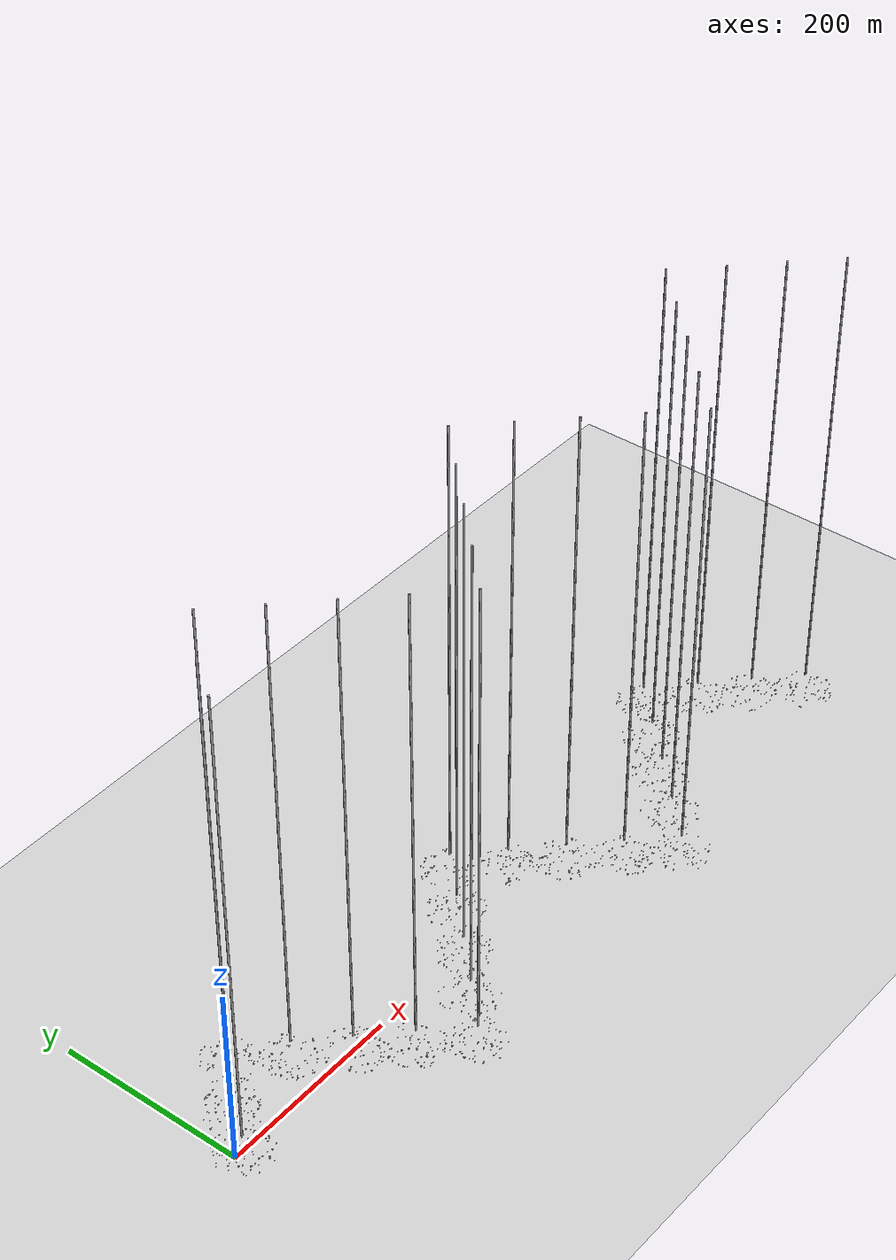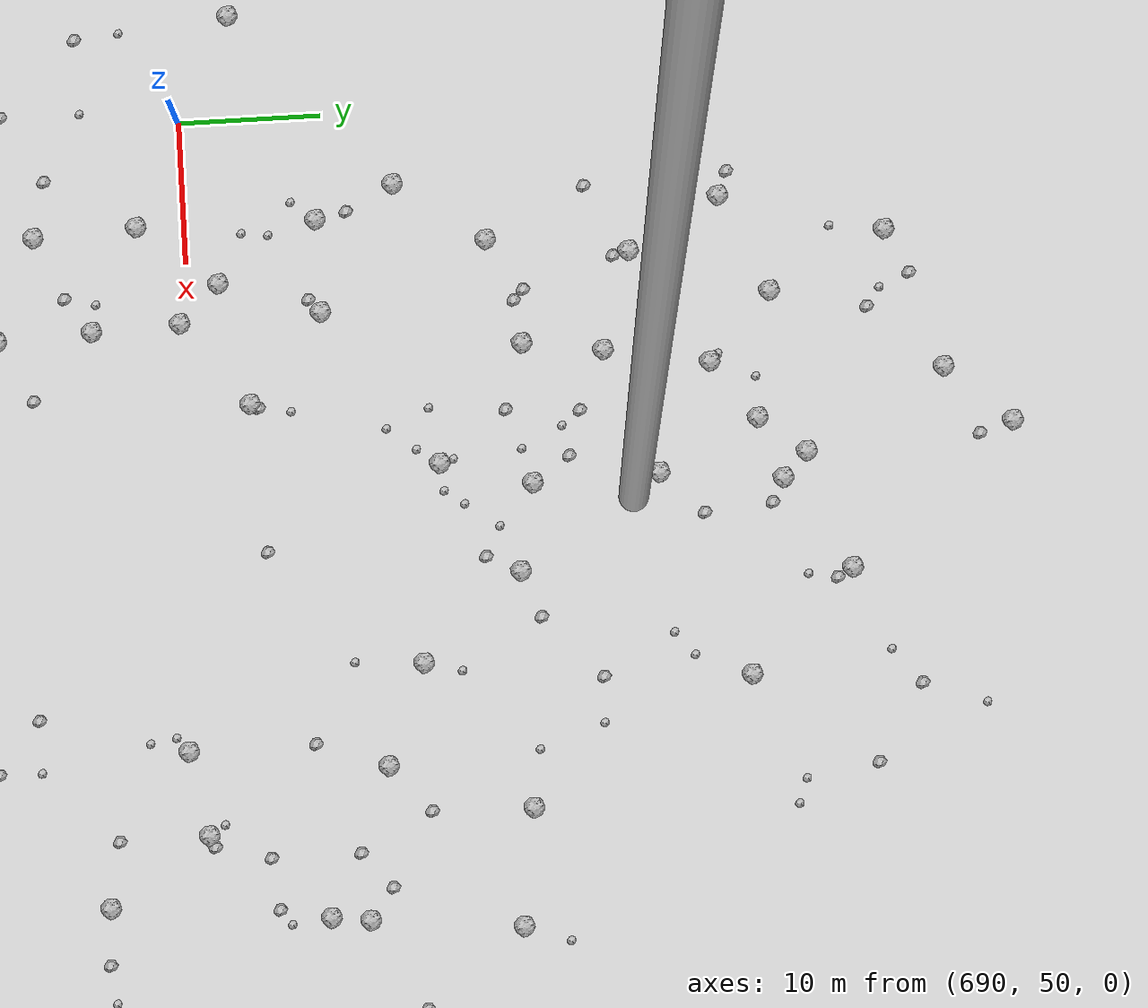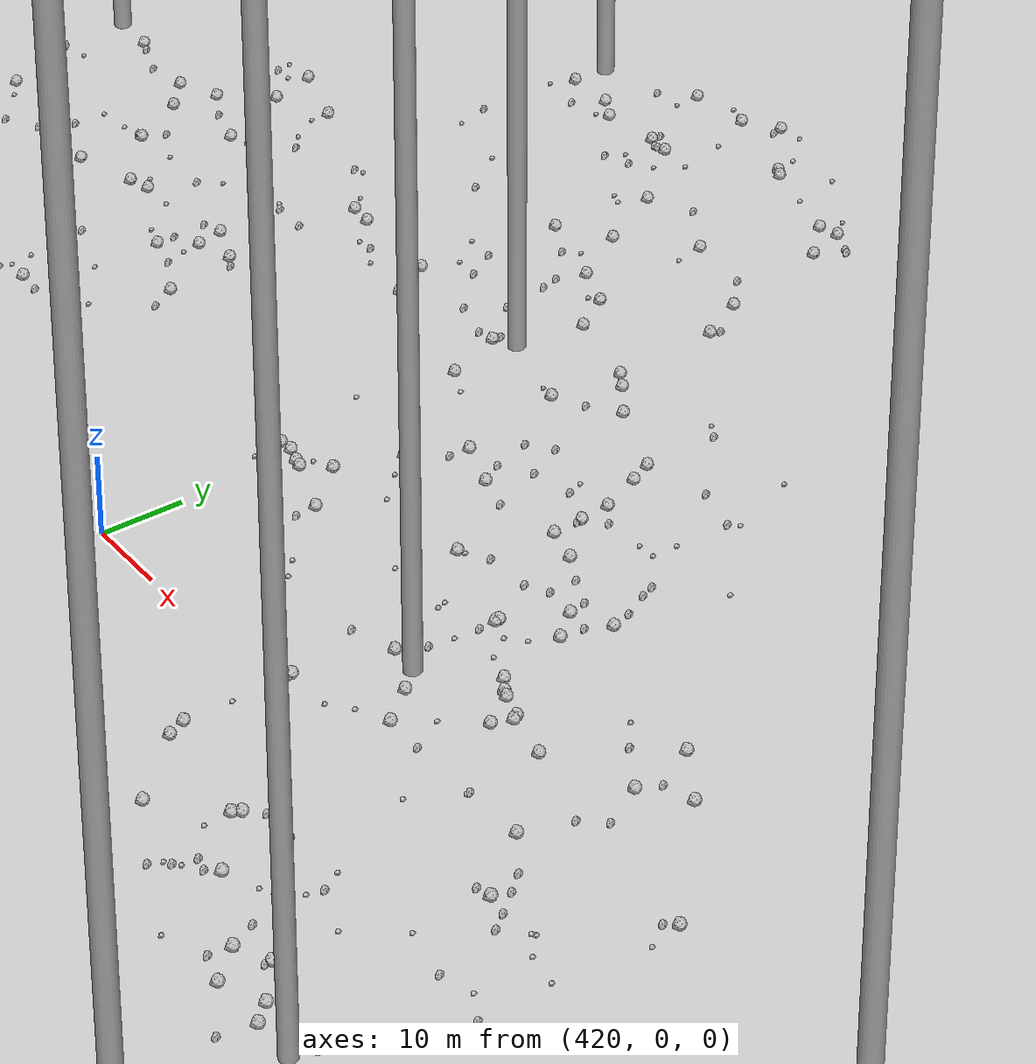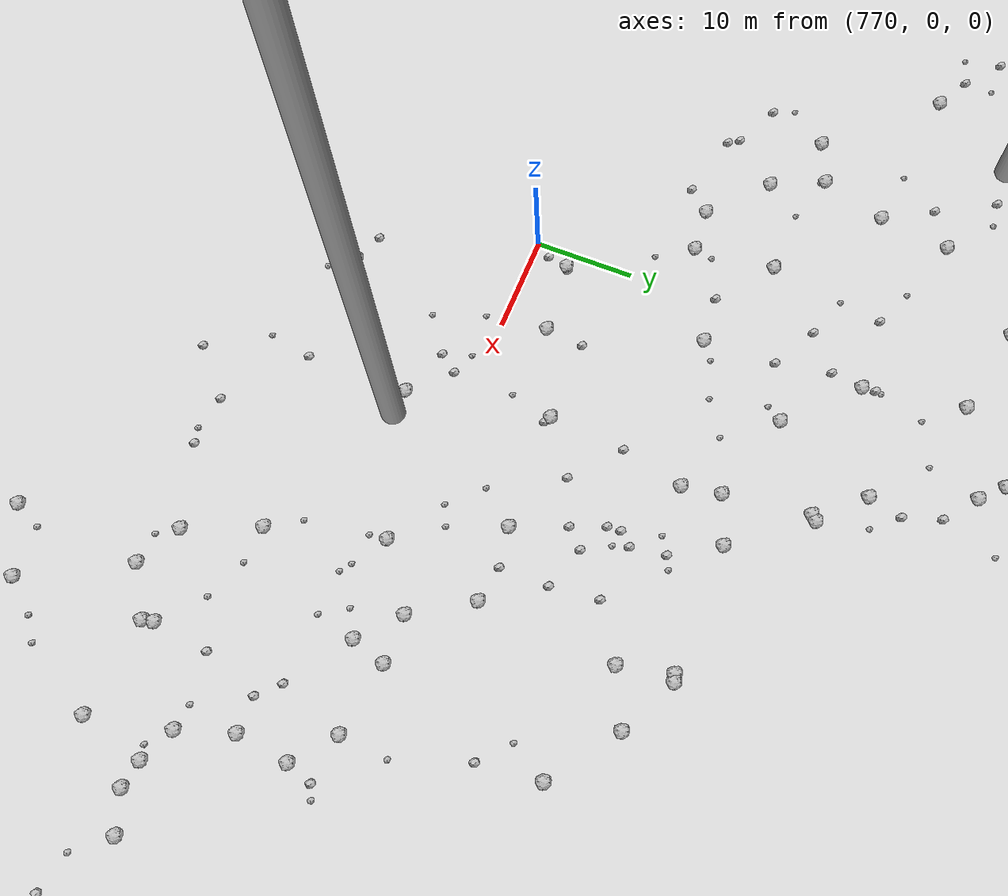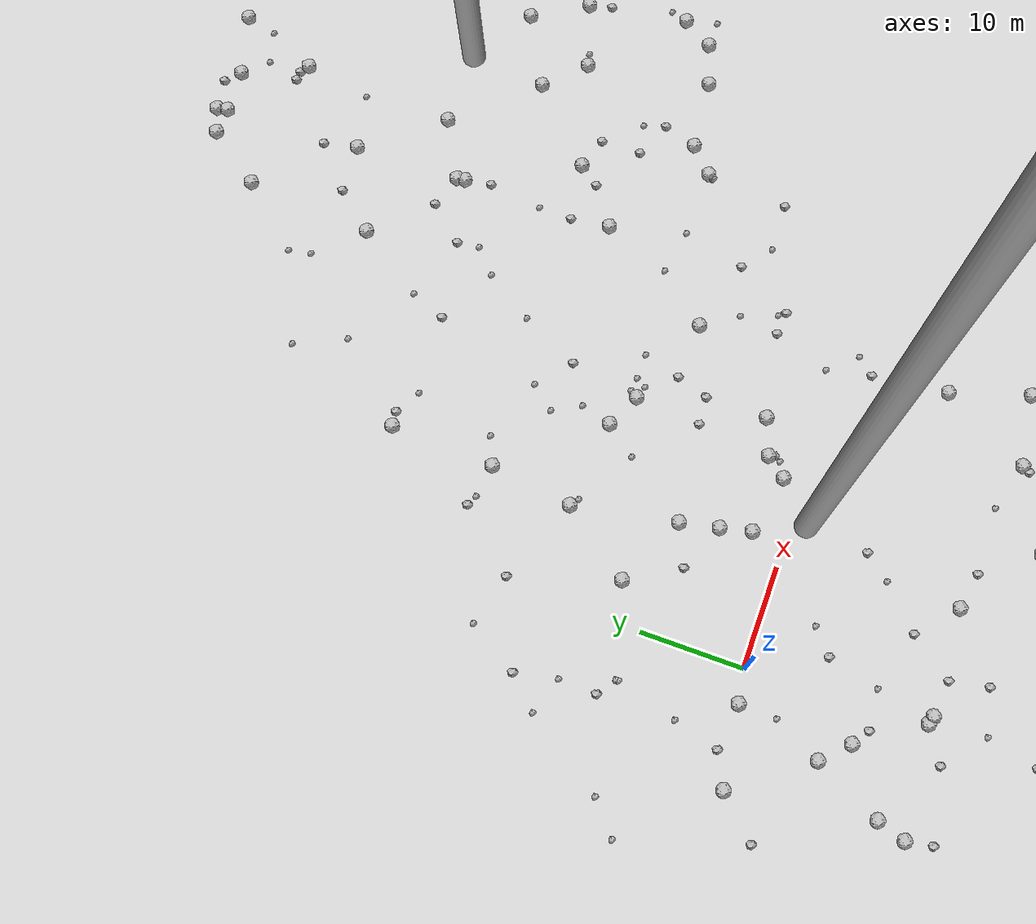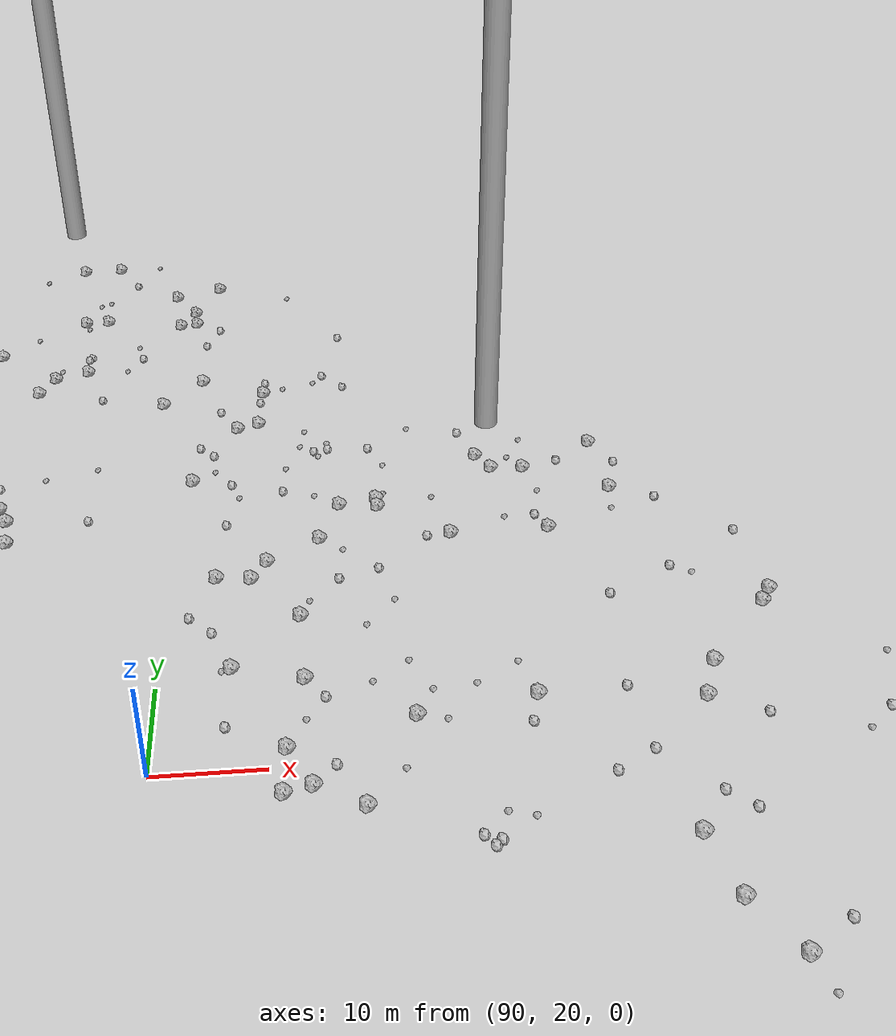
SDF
<sdf version="1.6">
 <world name="default">
  <include><uri>model://custom_ground</uri></include>
  <include><uri>model://sun</uri></include>
  <spherical_coordinates>
   <surface_model>EARTH_WGS84</surface_model>
   <latitude_deg>38.161479</latitude_deg>
   <longitude_deg>-122.454630</longitude_deg>
   <elevation>488.0</elevation>
   <heading_deg>90</heading_deg>
  </spherical_coordinates>
  <model name="rock1_0_0">
   <include><uri>model://rock1</uri><pose>3.9937051485219754 13.226636738104084 0.5 0 0 0</pose></include>
  </model>
  <model name="rock1_0_1">
   <include><uri>model://rock1</uri><pose>32.666175566197666 -6.545696962844929 0.5 0 0 0</pose></include>
  </model>
  <model name="rock1_0_2">
   <include><uri>model://rock1</uri><pose>11.712804470818071 6.270797589992291 0.5 0 0 0</pose></include>
  </model>
  <model name="rock1_0_3">
   <include><uri>model://rock1</uri><pose>-9.71944713488018 -18.30141748998962 0.5 0 0 0</pose></include>
  </model>
  <model name="rock1_0_4">
   <include><uri>model://rock1</uri><pose>19.392266764336533 -22.767119106981994 0.5 0 0 0</pose></include>
  </model>
  <model name="rock1_0_5">
   <include><uri>model://rock1</uri><pose>-3.1710704399875453 -0.5338670826136251 0.5 0 0 0</pose></include>
  </model>
  <model name="rock1_0_6">
   <include><uri>model://rock1</uri><pose>-10.956884471903635 -1.6851654338878035 0.5 0 0 0</pose></include>
  </model>
  <model name="rock1_0_7">
   <include><uri>model://rock1</uri><pose>33.9236657187219 -17.667514658195387 0.5 0 0 0</pose></include>
  </model>
  <model name="rock1_0_8">
   <include><uri>model://rock1</uri><pose>10.93800501169305 10.020285194934374 0.5 0 0 0</pose></include>
  </model>
  <model name="rock1_0_9">
   <include><uri>model://rock1</uri><pose>-5.613152850270847 -8.891268982938769 0.5 0 0 0</pose></include>
  </model>
  <model name="rock1_0_10">
   <include><uri>model://rock1</uri><pose>0.9064245646886668 -17.337191068665664 0.5 0 0 0</pose></include>
  </model>
  <model name="rock1_0_11">
   <include><uri>model://rock1</uri><pose>17.881252009598704 -24.112241314119615 0.5 0 0 0</pose></include>
  </model>
  <model name="rock1_0_12">
   <include><uri>model://rock1</uri><pose>1.684599318161716 -17.564629805920042 0.5 0 0 0</pose></include>
  </model>
  <model name="rock1_0_13">
   <include><uri>model://rock1</uri><pose>9.049068790655038 20.185188529607565 0.5 0 0 0</pose></include>
  </model>
  <model name="rock1_0_14">
   <include><uri>model://rock1</uri><pose>23.339197839652137 5.44724359323105 0.5 0 0 0</pose></include>
  </model>
  <model name="rock1_0_15">
   <include><uri>model://rock1</uri><pose>19.84394169574348 4.121600152625767 0.5 0 0 0</pose></include>
  </model>
  <model name="rock1_0_16">
   <include><uri>model://rock1</uri><pose>12.417536280697057 3.2640345103104025 0.5 0 0 0</pose></include>
  </model>
  <model name="rock1_0_17">
   <include><uri>model://rock1</uri><pose>18.253282727955437 2.1128226665537753 0.5 0 0 0</pose></include>
  </model>
  <model name="rock1_0_18">
   <include><uri>model://rock1</uri><pose>29.930326079061537 14.39945391987456 0.5 0 0 0</pose></include>
  </model>
  <model name="rock1_0_19">
   <include><uri>model://rock1</uri><pose>36.42651281007966 -6.84026752303026 0.5 0 0 0</pose></include>
  </model>
  <model name="rock1_0_20">
   <include><uri>model://rock1</uri><pose>11.997931795491038 -17.04063532317275 0.5 0 0 0</pose></include>
  </model>
  <model name="rock1_0_21">
   <include><uri>model://rock1</uri><pose>31.526390785895366 -10.14602298349153 0.5 0 0 0</pose></include>
  </model>
  <model name="rock1_0_22">
   <include><uri>model://rock1</uri><pose>17.742904759940636 19.298448495934466 0.5 0 0 0</pose></include>
  </model>
  <model name="rock1_0_23">
   <include><uri>model://rock1</uri><pose>-3.1585642133456524 -11.329017912613711 0.5 0 0 0</pose></include>
  </model>
  <model name="rock1_0_24">
   <include><uri>model://rock1</uri><pose>10.17415643934508 28.37724096655206 0.5 0 0 0</pose></include>
  </model>
  <model name="rock1_0_25">
   <include><uri>model://rock1</uri><pose>-8.81494869602609 -15.505802928642165 0.5 0 0 0</pose></include>
  </model>
  <model name="rock1_0_26">
   <include><uri>model://rock1</uri><pose>26.982717340063722 -18.798054757076734 0.5 0 0 0</pose></include>
  </model>
  <model name="rock2_0_0">
   <include><uri>model://rock2</uri><pose>-1.5017157984200438 -12.48741205082332 0.3 0 0 0</pose></include>
  </model>
  <model name="rock2_0_1">
   <include><uri>model://rock2</uri><pose>-14.62202311012486 -5.522744863368658 0.3 0 0 0</pose></include>
  </model>
  <model name="rock2_0_2">
   <include><uri>model://rock2</uri><pose>8.303248539393785 -13.780156886353577 0.3 0 0 0</pose></include>
  </model>
  <model name="rock2_0_3">
   <include><uri>model://rock2</uri><pose>30.70132647555051 -2.7666086794580593 0.3 0 0 0</pose></include>
  </model>
  <model name="rock2_0_4">
   <include><uri>model://rock2</uri><pose>31.69223062807246 7.097268239401927 0.3 0 0 0</pose></include>
  </model>
  <model name="rock2_0_5">
   <include><uri>model://rock2</uri><pose>23.316413031879698 11.486771412154333 0.3 0 0 0</pose></include>
  </model>
  <model name="rock2_0_6">
   <include><uri>model://rock2</uri><pose>-2.348886057211203 -19.459271720138158 0.3 0 0 0</pose></include>
  </model>
  <model name="rock2_0_7">
   <include><uri>model://rock2</uri><pose>18.625900720236515 -28.63007431406477 0.3 0 0 0</pose></include>
  </model>
  <model name="rock2_0_8">
   <include><uri>model://rock2</uri><pose>0.36523865719416904 -27.786386261160448 0.3 0 0 0</pose></include>
  </model>
  <model name="rock2_0_9">
   <include><uri>model://rock2</uri><pose>5.856863133902227 29.27154115271587 0.3 0 0 0</pose></include>
  </model>
  <model name="rock2_0_10">
   <include><uri>model://rock2</uri><pose>24.34783962716903 14.651189785116571 0.3 0 0 0</pose></include>
  </model>
  <model name="rock2_0_11">
   <include><uri>model://rock2</uri><pose>20.037219133900727 3.5922275300405744 0.3 0 0 0</pose></include>
  </model>
  <model name="rock2_0_12">
   <include><uri>model://rock2</uri><pose>33.97576716519863 6.901226151351018 0.3 0 0 0</pose></include>
  </model>
  <model name="rock2_0_13">
   <include><uri>model://rock2</uri><pose>20.60175841269205 11.279411008638988 0.3 0 0 0</pose></include>
  </model>
  <model name="rock2_0_14">
   <include><uri>model://rock2</uri><pose>34.80095797489467 -8.327129760608209 0.3 0 0 0</pose></include>
  </model>
  <model name="rock2_0_15">
   <include><uri>model://rock2</uri><pose>3.6585062635211827 -7.049693510824152 0.3 0 0 0</pose></include>
  </model>
  <model name="rock2_0_16">
   <include><uri>model://rock2</uri><pose>5.978688644880069 -21.715106041816263 0.3 0 0 0</pose></include>
  </model>
  <model name="rock2_0_17">
   <include><uri>model://rock2</uri><pose>-9.293570102469692 -20.889914129119692 0.3 0 0 0</pose></include>
  </model>
  <model name="rock2_0_18">
   <include><uri>model://rock2</uri><pose>26.604772820072213 -19.584210600955515 0.3 0 0 0</pose></include>
  </model>
  <model name="rock2_0_19">
   <include><uri>model://rock2</uri><pose>-7.425381356635031 19.83345798642928 0.3 0 0 0</pose></include>
  </model>
  <model name="rock2_0_20">
   <include><uri>model://rock2</uri><pose>14.122039226306676 -7.487581299307845 0.3 0 0 0</pose></include>
  </model>
  <model name="rock2_0_21">
   <include><uri>model://rock2</uri><pose>15.641366057583156 -17.740860884383537 0.3 0 0 0</pose></include>
  </model>
  <model name="rock2_0_22">
   <include><uri>model://rock2</uri><pose>5.244286328130741 -17.997617748012765 0.3 0 0 0</pose></include>
  </model>
  <model name="rock2_0_23">
   <include><uri>model://rock2</uri><pose>7.007984245357459 8.196573484977705 0.3 0 0 0</pose></include>
  </model>
  <model name="rock2_0_24">
   <include><uri>model://rock2</uri><pose>-6.7000273492246905 11.9451737022194 0.3 0 0 0</pose></include>
  </model>
  <model name="rock2_0_25">
   <include><uri>model://rock2</uri><pose>-7.7263164200424015 -0.02803619477660746 0.3 0 0 0</pose></include>
  </model>
  <model name="rock2_0_26">
   <include><uri>model://rock2</uri><pose>0.7129778715243731 23.465629186272253 0.3 0 0 0</pose></include>
  </model>
  <model name="rock3_0_0">
   <include><uri>model://rock3</uri><pose>32.12740904099087 -1.1337549380817897 0.2 0 0 0</pose></include>
  </model>
  <model name="rock3_0_1">
   <include><uri>model://rock3</uri><pose>-18.418424961521293 6.289546999561267 0.2 0 0 0</pose></include>
  </model>
  <model name="rock3_0_2">
   <include><uri>model://rock3</uri><pose>-10.25259081966881 16.82263956704685 0.2 0 0 0</pose></include>
  </model>
  <model name="rock3_0_3">
   <include><uri>model://rock3</uri><pose>12.838736851004391 29.578202345691118 0.2 0 0 0</pose></include>
  </model>
  <model name="rock3_0_4">
   <include><uri>model://rock3</uri><pose>-4.443435940160359 24.77592752832468 0.2 0 0 0</pose></include>
  </model>
  <model name="rock3_0_5">
   <include><uri>model://rock3</uri><pose>-6.594273943156031 15.64468285158857 0.2 0 0 0</pose></include>
  </model>
  <model name="rock3_0_6">
   <include><uri>model://rock3</uri><pose>-4.9085628711002 10.677757977291037 0.2 0 0 0</pose></include>
  </model>
  <model name="rock3_0_7">
   <include><uri>model://rock3</uri><pose>1.5337566856592169 -22.842508634090727 0.2 0 0 0</pose></include>
  </model>
  <model name="rock3_0_8">
   <include><uri>model://rock3</uri><pose>29.777274106951126 1.5177572023425263 0.2 0 0 0</pose></include>
  </model>
  <model name="rock3_0_9">
   <include><uri>model://rock3</uri><pose>6.874272101374345 28.776389902246834 0.2 0 0 0</pose></include>
  </model>
  <model name="rock3_0_10">
   <include><uri>model://rock3</uri><pose>5.953173490907801 -5.048293334038931 0.2 0 0 0</pose></include>
  </model>
  <model name="rock3_0_11">
   <include><uri>model://rock3</uri><pose>33.500224533773775 7.515340229549892 0.2 0 0 0</pose></include>
  </model>
  <model name="rock3_0_12">
   <include><uri>model://rock3</uri><pose>22.194343530594047 -17.580560928907964 0.2 0 0 0</pose></include>
  </model>
  <model name="rock3_0_13">
   <include><uri>model://rock3</uri><pose>-3.3121052900431316 -4.279036331793694 0.2 0 0 0</pose></include>
  </model>
  <model name="rock3_0_14">
   <include><uri>model://rock3</uri><pose>9.838434125584893 19.57897646547972 0.2 0 0 0</pose></include>
  </model>
  <model name="rock3_0_15">
   <include><uri>model://rock3</uri><pose>22.905640612868226 18.318791254368037 0.2 0 0 0</pose></include>
  </model>
  <model name="rock3_0_16">
   <include><uri>model://rock3</uri><pose>22.323929606982624 17.316251103397377 0.2 0 0 0</pose></include>
  </model>
  <model name="rock3_0_17">
   <include><uri>model://rock3</uri><pose>17.107078872028872 25.03570016728394 0.2 0 0 0</pose></include>
  </model>
  <model name="rock3_0_18">
   <include><uri>model://rock3</uri><pose>-6.52875474182477 4.428586715753127 0.2 0 0 0</pose></include>
  </model>
  <model name="rock3_0_19">
   <include><uri>model://rock3</uri><pose>19.686982283961818 2.883434110642952 0.2 0 0 0</pose></include>
  </model>
  <model name="rock3_0_20">
   <include><uri>model://rock3</uri><pose>-4.900391226221677 10.43219818530725 0.2 0 0 0</pose></include>
  </model>
  <model name="rock3_0_21">
   <include><uri>model://rock3</uri><pose>15.411518171937203 16.231902602779925 0.2 0 0 0</pose></include>
  </model>
  <model name="rock3_0_22">
   <include><uri>model://rock3</uri><pose>12.133360480637222 -10.042186505985697 0.2 0 0 0</pose></include>
  </model>
  <model name="rock3_0_23">
   <include><uri>model://rock3</uri><pose>2.372588736974887 -12.13556519606292 0.2 0 0 0</pose></include>
  </model>
  <model name="rock3_0_24">
   <include><uri>model://rock3</uri><pose>32.19790733548524 10.965834704325907 0.2 0 0 0</pose></include>
  </model>
  <model name="rock3_0_25">
   <include><uri>model://rock3</uri><pose>-15.385023535955627 8.951713928267864 0.2 0 0 0</pose></include>
  </model>
  <model name="rock3_0_26">
   <include><uri>model://rock3</uri><pose>23.48967695532236 11.6932719378242 0.2 0 0 0</pose></include>
  </model>
  <model name="rock1_1_0">
   <include><uri>model://rock1</uri><pose>58.44880634559637 23.03495944597699 0.5 0 0 0</pose></include>
  </model>
  <model name="rock1_1_1">
   <include><uri>model://rock1</uri><pose>35.56268682221506 66.09401811566275 0.5 0 0 0</pose></include>
  </model>
  <model name="rock1_1_2">
   <include><uri>model://rock1</uri><pose>41.816508557835476 30.69989271515618 0.5 0 0 0</pose></include>
  </model>
  <model name="rock1_1_3">
   <include><uri>model://rock1</uri><pose>28.18659318757071 48.237899173376675 0.5 0 0 0</pose></include>
  </model>
  <model name="rock1_1_4">
   <include><uri>model://rock1</uri><pose>36.34263528055169 41.885592119045526 0.5 0 0 0</pose></include>
  </model>
  <model name="rock1_1_5">
   <include><uri>model://rock1</uri><pose>29.127610378680863 60.826373243713036 0.5 0 0 0</pose></include>
  </model>
  <model name="rock1_1_6">
   <include><uri>model://rock1</uri><pose>42.686500422686514 60.20341090087558 0.5 0 0 0</pose></include>
  </model>
  <model name="rock1_1_7">
   <include><uri>model://rock1</uri><pose>36.14768156855349 52.37100380707488 0.5 0 0 0</pose></include>
  </model>
  <model name="rock1_1_8">
   <include><uri>model://rock1</uri><pose>41.9325634239449 44.94813073654841 0.5 0 0 0</pose></include>
  </model>
  <model name="rock1_1_9">
   <include><uri>model://rock1</uri><pose>21.084035770645944 17.74528961836866 0.5 0 0 0</pose></include>
  </model>
  <model name="rock1_1_10">
   <include><uri>model://rock1</uri><pose>54.37150687961942 21.676772868799485 0.5 0 0 0</pose></include>
  </model>
  <model name="rock1_1_11">
   <include><uri>model://rock1</uri><pose>60.24715776013814 26.063119246480852 0.5 0 0 0</pose></include>
  </model>
  <model name="rock1_1_12">
   <include><uri>model://rock1</uri><pose>36.464358982267356 41.053527579108184 0.5 0 0 0</pose></include>
  </model>
  <model name="rock1_1_13">
   <include><uri>model://rock1</uri><pose>45.69579592290532 67.9965250022864 0.5 0 0 0</pose></include>
  </model>
  <model name="rock1_1_14">
   <include><uri>model://rock1</uri><pose>35.35473827570274 67.12778002887417 0.5 0 0 0</pose></include>
  </model>
  <model name="rock1_1_15">
   <include><uri>model://rock1</uri><pose>47.5555003189464 20.917982458162292 0.5 0 0 0</pose></include>
  </model>
  <model name="rock1_1_16">
   <include><uri>model://rock1</uri><pose>63.24574744149378 33.686887209181776 0.5 0 0 0</pose></include>
  </model>
  <model name="rock1_1_17">
   <include><uri>model://rock1</uri><pose>58.59235904717773 35.8644822679005 0.5 0 0 0</pose></include>
  </model>
  <model name="rock1_1_18">
   <include><uri>model://rock1</uri><pose>32.97640421160442 66.19242777397577 0.5 0 0 0</pose></include>
  </model>
  <model name="rock1_1_19">
   <include><uri>model://rock1</uri><pose>52.24241905052833 33.796343819986845 0.5 0 0 0</pose></include>
  </model>
  <model name="rock1_1_20">
   <include><uri>model://rock1</uri><pose>55.46735570784006 41.10373827219151 0.5 0 0 0</pose></include>
  </model>
  <model name="rock1_1_21">
   <include><uri>model://rock1</uri><pose>10.633079512580736 38.676268771250065 0.5 0 0 0</pose></include>
  </model>
  <model name="rock1_1_22">
   <include><uri>model://rock1</uri><pose>64.65335677781678 45.718106483295756 0.5 0 0 0</pose></include>
  </model>
  <model name="rock1_1_23">
   <include><uri>model://rock1</uri><pose>36.62704609918918 26.016857572721143 0.5 0 0 0</pose></include>
  </model>
  <model name="rock1_1_24">
   <include><uri>model://rock1</uri><pose>45.11852949368993 18.57244555129693 0.5 0 0 0</pose></include>
  </model>
  <model name="rock1_1_25">
   <include><uri>model://rock1</uri><pose>39.74844332804096 66.32180874789984 0.5 0 0 0</pose></include>
  </model>
  <model name="rock1_1_26">
   <include><uri>model://rock1</uri><pose>48.67122485678334 37.40988486272511 0.5 0 0 0</pose></include>
  </model>
  <model name="rock2_1_0">
   <include><uri>model://rock2</uri><pose>38.39180729478474 67.67004074361944 0.3 0 0 0</pose></include>
  </model>
  <model name="rock2_1_1">
   <include><uri>model://rock2</uri><pose>44.427177410336334 10.429290706045915 0.3 0 0 0</pose></include>
  </model>
  <model name="rock2_1_2">
   <include><uri>model://rock2</uri><pose>41.85784369201919 60.863426818648335 0.3 0 0 0</pose></include>
  </model>
  <model name="rock2_1_3">
   <include><uri>model://rock2</uri><pose>56.74578342183126 51.28599142981717 0.3 0 0 0</pose></include>
  </model>
  <model name="rock2_1_4">
   <include><uri>model://rock2</uri><pose>37.024696300061066 12.490721984856904 0.3 0 0 0</pose></include>
  </model>
  <model name="rock2_1_5">
   <include><uri>model://rock2</uri><pose>58.78168338483444 54.390936892322394 0.3 0 0 0</pose></include>
  </model>
  <model name="rock2_1_6">
   <include><uri>model://rock2</uri><pose>44.93325391331692 29.718888055735835 0.3 0 0 0</pose></include>
  </model>
  <model name="rock2_1_7">
   <include><uri>model://rock2</uri><pose>63.777607727410434 27.623473032200828 0.3 0 0 0</pose></include>
  </model>
  <model name="rock2_1_8">
   <include><uri>model://rock2</uri><pose>35.44397671725998 55.742491549235474 0.3 0 0 0</pose></include>
  </model>
  <model name="rock2_1_9">
   <include><uri>model://rock2</uri><pose>59.18924712297426 33.6800565265917 0.3 0 0 0</pose></include>
  </model>
  <model name="rock2_1_10">
   <include><uri>model://rock2</uri><pose>36.14622175210743 29.842743503250098 0.3 0 0 0</pose></include>
  </model>
  <model name="rock2_1_11">
   <include><uri>model://rock2</uri><pose>22.352774951893757 38.15031201156668 0.3 0 0 0</pose></include>
  </model>
  <model name="rock2_1_12">
   <include><uri>model://rock2</uri><pose>44.883100953632585 18.144832052523057 0.3 0 0 0</pose></include>
  </model>
  <model name="rock2_1_13">
   <include><uri>model://rock2</uri><pose>36.89548822507322 38.505760803729316 0.3 0 0 0</pose></include>
  </model>
  <model name="rock2_1_14">
   <include><uri>model://rock2</uri><pose>68.64995420719467 39.19594591059281 0.3 0 0 0</pose></include>
  </model>
  <model name="rock2_1_15">
   <include><uri>model://rock2</uri><pose>40.30084033134129 28.690194506969398 0.3 0 0 0</pose></include>
  </model>
  <model name="rock2_1_16">
   <include><uri>model://rock2</uri><pose>58.88865766679306 59.8001060503882 0.3 0 0 0</pose></include>
  </model>
  <model name="rock2_1_17">
   <include><uri>model://rock2</uri><pose>40.92681055048833 60.92670407153058 0.3 0 0 0</pose></include>
  </model>
  <model name="rock2_1_18">
   <include><uri>model://rock2</uri><pose>56.068831668181296 50.20662957373701 0.3 0 0 0</pose></include>
  </model>
  <model name="rock2_1_19">
   <include><uri>model://rock2</uri><pose>33.1138024428631 42.98196150246028 0.3 0 0 0</pose></include>
  </model>
  <model name="rock2_1_20">
   <include><uri>model://rock2</uri><pose>22.279584103115454 24.637146829117924 0.3 0 0 0</pose></include>
  </model>
  <model name="rock2_1_21">
   <include><uri>model://rock2</uri><pose>45.02377852810361 25.760317504332626 0.3 0 0 0</pose></include>
  </model>
  <model name="rock2_1_22">
   <include><uri>model://rock2</uri><pose>12.055675116541364 38.89260907562678 0.3 0 0 0</pose></include>
  </model>
  <model name="rock2_1_23">
   <include><uri>model://rock2</uri><pose>30.061479428885814 39.483944397208106 0.3 0 0 0</pose></include>
  </model>
  <model name="rock2_1_24">
   <include><uri>model://rock2</uri><pose>31.38307492376784 52.116775866618994 0.3 0 0 0</pose></include>
  </model>
  <model name="rock2_1_25">
   <include><uri>model://rock2</uri><pose>48.59804346878447 24.23466809834151 0.3 0 0 0</pose></include>
  </model>
  <model name="rock2_1_26">
   <include><uri>model://rock2</uri><pose>66.06701264480805 43.76596234842317 0.3 0 0 0</pose></include>
  </model>
  <model name="rock3_1_0">
   <include><uri>model://rock3</uri><pose>24.196538996432857 52.55446423017294 0.2 0 0 0</pose></include>
  </model>
  <model name="rock3_1_1">
   <include><uri>model://rock3</uri><pose>55.84520001997458 48.29198271288437 0.2 0 0 0</pose></include>
  </model>
  <model name="rock3_1_2">
   <include><uri>model://rock3</uri><pose>41.57629945291734 53.59461628417009 0.2 0 0 0</pose></include>
  </model>
  <model name="rock3_1_3">
   <include><uri>model://rock3</uri><pose>60.788454939505264 27.720492093259214 0.2 0 0 0</pose></include>
  </model>
  <model name="rock3_1_4">
   <include><uri>model://rock3</uri><pose>36.22486370880351 33.15065404340896 0.2 0 0 0</pose></include>
  </model>
  <model name="rock3_1_5">
   <include><uri>model://rock3</uri><pose>14.503279242041113 37.48243022750141 0.2 0 0 0</pose></include>
  </model>
  <model name="rock3_1_6">
   <include><uri>model://rock3</uri><pose>47.954646087785996 26.349572035163217 0.2 0 0 0</pose></include>
  </model>
  <model name="rock3_1_7">
   <include><uri>model://rock3</uri><pose>44.93788697284122 64.99767354114783 0.2 0 0 0</pose></include>
  </model>
  <model name="rock3_1_8">
   <include><uri>model://rock3</uri><pose>30.339007119833653 37.284598430364625 0.2 0 0 0</pose></include>
  </model>
  <model name="rock3_1_9">
   <include><uri>model://rock3</uri><pose>38.532273261041226 18.635016245280056 0.2 0 0 0</pose></include>
  </model>
  <model name="rock3_1_10">
   <include><uri>model://rock3</uri><pose>53.510379887574175 34.094026740266116 0.2 0 0 0</pose></include>
  </model>
  <model name="rock3_1_11">
   <include><uri>model://rock3</uri><pose>25.02742370771948 30.366953824324458 0.2 0 0 0</pose></include>
  </model>
  <model name="rock3_1_12">
   <include><uri>model://rock3</uri><pose>58.54133216818901 35.47045795843883 0.2 0 0 0</pose></include>
  </model>
  <model name="rock3_1_13">
   <include><uri>model://rock3</uri><pose>28.025145833834454 35.15439189297237 0.2 0 0 0</pose></include>
  </model>
  <model name="rock3_1_14">
   <include><uri>model://rock3</uri><pose>61.09548942672455 23.010844137969624 0.2 0 0 0</pose></include>
  </model>
  <model name="rock3_1_15">
   <include><uri>model://rock3</uri><pose>17.270014070416046 45.89135735914332 0.2 0 0 0</pose></include>
  </model>
  <model name="rock3_1_16">
   <include><uri>model://rock3</uri><pose>18.572857477461223 22.33443277454206 0.2 0 0 0</pose></include>
  </model>
  <model name="rock3_1_17">
   <include><uri>model://rock3</uri><pose>19.03901097023219 27.371429663794864 0.2 0 0 0</pose></include>
  </model>
  <model name="rock3_1_18">
   <include><uri>model://rock3</uri><pose>15.001085113225823 50.79734568490813 0.2 0 0 0</pose></include>
  </model>
  <model name="rock3_1_19">
   <include><uri>model://rock3</uri><pose>23.70306113383498 41.5823952579858 0.2 0 0 0</pose></include>
  </model>
  <model name="rock3_1_20">
   <include><uri>model://rock3</uri><pose>23.78536877890837 54.74951157466328 0.2 0 0 0</pose></include>
  </model>
  <model name="rock3_1_21">
   <include><uri>model://rock3</uri><pose>39.742952326793066 10.175623183248879 0.2 0 0 0</pose></include>
  </model>
  <model name="rock3_1_22">
   <include><uri>model://rock3</uri><pose>41.838263775424615 64.1689796994059 0.2 0 0 0</pose></include>
  </model>
  <model name="rock3_1_23">
   <include><uri>model://rock3</uri><pose>25.4012302753533 18.3030916539402 0.2 0 0 0</pose></include>
  </model>
  <model name="rock3_1_24">
   <include><uri>model://rock3</uri><pose>21.570267153899536 18.469279538982974 0.2 0 0 0</pose></include>
  </model>
  <model name="rock3_1_25">
   <include><uri>model://rock3</uri><pose>62.301705961123616 34.68547483115336 0.2 0 0 0</pose></include>
  </model>
  <model name="rock3_1_26">
   <include><uri>model://rock3</uri><pose>34.12679530534085 19.37889512508348 0.2 0 0 0</pose></include>
  </model>
  <model name="rock1_2_0">
   <include><uri>model://rock1</uri><pose>87.79763291568258 75.27366754699221 0.5 0 0 0</pose></include>
  </model>
  <model name="rock1_2_1">
   <include><uri>model://rock1</uri><pose>88.77995466312893 93.20646804690142 0.5 0 0 0</pose></include>
  </model>
  <model name="rock1_2_2">
   <include><uri>model://rock1</uri><pose>69.09849509247061 65.55556899168197 0.5 0 0 0</pose></include>
  </model>
  <model name="rock1_2_3">
   <include><uri>model://rock1</uri><pose>67.31190373512229 70.6411437433031 0.5 0 0 0</pose></include>
  </model>
  <model name="rock1_2_4">
   <include><uri>model://rock1</uri><pose>90.75654507289227 93.49549321177354 0.5 0 0 0</pose></include>
  </model>
  <model name="rock1_2_5">
   <include><uri>model://rock1</uri><pose>67.75881460409192 87.53077878706873 0.5 0 0 0</pose></include>
  </model>
  <model name="rock1_2_6">
   <include><uri>model://rock1</uri><pose>74.7911741822165 81.88170689193313 0.5 0 0 0</pose></include>
  </model>
  <model name="rock1_2_7">
   <include><uri>model://rock1</uri><pose>92.09483249160076 79.85296922091626 0.5 0 0 0</pose></include>
  </model>
  <model name="rock1_2_8">
   <include><uri>model://rock1</uri><pose>90.52684875862477 96.21256168604654 0.5 0 0 0</pose></include>
  </model>
  <model name="rock1_2_9">
   <include><uri>model://rock1</uri><pose>79.65012592291475 94.94168345877799 0.5 0 0 0</pose></include>
  </model>
  <model name="rock1_2_10">
   <include><uri>model://rock1</uri><pose>96.35341861549671 69.64918662674924 0.5 0 0 0</pose></include>
  </model>
  <model name="rock1_2_11">
   <include><uri>model://rock1</uri><pose>91.81130679534932 60.134610338079334 0.5 0 0 0</pose></include>
  </model>
  <model name="rock1_2_12">
   <include><uri>model://rock1</uri><pose>72.19524719146779 57.05446071890373 0.5 0 0 0</pose></include>
  </model>
  <model name="rock1_2_13">
   <include><uri>model://rock1</uri><pose>87.94795002413582 100.50866098989526 0.5 0 0 0</pose></include>
  </model>
  <model name="rock1_2_14">
   <include><uri>model://rock1</uri><pose>99.1559013409437 76.70879042062026 0.5 0 0 0</pose></include>
  </model>
  <model name="rock1_2_15">
   <include><uri>model://rock1</uri><pose>61.947740050216865 88.13808446298113 0.5 0 0 0</pose></include>
  </model>
  <model name="rock1_2_16">
   <include><uri>model://rock1</uri><pose>73.24359662442473 78.88207796277692 0.5 0 0 0</pose></include>
  </model>
  <model name="rock1_2_17">
   <include><uri>model://rock1</uri><pose>78.3974453748869 83.13019330850884 0.5 0 0 0</pose></include>
  </model>
  <model name="rock1_2_18">
   <include><uri>model://rock1</uri><pose>93.31896717083639 102.29554507523856 0.5 0 0 0</pose></include>
  </model>
  <model name="rock1_2_19">
   <include><uri>model://rock1</uri><pose>98.66073322475583 70.4825835927096 0.5 0 0 0</pose></include>
  </model>
  <model name="rock1_2_20">
   <include><uri>model://rock1</uri><pose>63.8533860467775 71.2013849572278 0.5 0 0 0</pose></include>
  </model>
  <model name="rock1_2_21">
   <include><uri>model://rock1</uri><pose>79.95109530246283 108.81792119497977 0.5 0 0 0</pose></include>
  </model>
  <model name="rock1_2_22">
   <include><uri>model://rock1</uri><pose>73.70046459399215 51.37680234782622 0.5 0 0 0</pose></include>
  </model>
  <model name="rock1_2_23">
   <include><uri>model://rock1</uri><pose>75.29665706932428 108.61473991241502 0.5 0 0 0</pose></include>
  </model>
  <model name="rock1_2_24">
   <include><uri>model://rock1</uri><pose>65.15150507092027 56.35741098801263 0.5 0 0 0</pose></include>
  </model>
  <model name="rock1_2_25">
   <include><uri>model://rock1</uri><pose>76.91846201562878 94.79899930283266 0.5 0 0 0</pose></include>
  </model>
  <model name="rock1_2_26">
   <include><uri>model://rock1</uri><pose>73.17505367331295 54.86481092583315 0.5 0 0 0</pose></include>
  </model>
  <model name="rock2_2_0">
   <include><uri>model://rock2</uri><pose>99.29256479693608 78.97685945074721 0.3 0 0 0</pose></include>
  </model>
  <model name="rock2_2_1">
   <include><uri>model://rock2</uri><pose>66.22607920491461 85.41752650067357 0.3 0 0 0</pose></include>
  </model>
  <model name="rock2_2_2">
   <include><uri>model://rock2</uri><pose>65.90230932009256 92.24740539327055 0.3 0 0 0</pose></include>
  </model>
  <model name="rock2_2_3">
   <include><uri>model://rock2</uri><pose>56.007296196195426 72.55379006145583 0.3 0 0 0</pose></include>
  </model>
  <model name="rock2_2_4">
   <include><uri>model://rock2</uri><pose>84.65317102701331 85.78424475704605 0.3 0 0 0</pose></include>
  </model>
  <model name="rock2_2_5">
   <include><uri>model://rock2</uri><pose>95.9344569756538 59.30551074316896 0.3 0 0 0</pose></include>
  </model>
  <model name="rock2_2_6">
   <include><uri>model://rock2</uri><pose>104.69578514840306 64.71161328486575 0.3 0 0 0</pose></include>
  </model>
  <model name="rock2_2_7">
   <include><uri>model://rock2</uri><pose>59.91139447928518 87.54508053641808 0.3 0 0 0</pose></include>
  </model>
  <model name="rock2_2_8">
   <include><uri>model://rock2</uri><pose>94.37628976824706 73.24006665033664 0.3 0 0 0</pose></include>
  </model>
  <model name="rock2_2_9">
   <include><uri>model://rock2</uri><pose>92.19155858711827 88.11029753746145 0.3 0 0 0</pose></include>
  </model>
  <model name="rock2_2_10">
   <include><uri>model://rock2</uri><pose>108.1032899680527 88.76163101107792 0.3 0 0 0</pose></include>
  </model>
  <model name="rock2_2_11">
   <include><uri>model://rock2</uri><pose>82.58149080814117 104.19651442907968 0.3 0 0 0</pose></include>
  </model>
  <model name="rock2_2_12">
   <include><uri>model://rock2</uri><pose>69.24757198175791 53.89130808918984 0.3 0 0 0</pose></include>
  </model>
  <model name="rock2_2_13">
   <include><uri>model://rock2</uri><pose>105.95447158784387 80.06648733945097 0.3 0 0 0</pose></include>
  </model>
  <model name="rock2_2_14">
   <include><uri>model://rock2</uri><pose>98.79857424953107 74.84146964738002 0.3 0 0 0</pose></include>
  </model>
  <model name="rock2_2_15">
   <include><uri>model://rock2</uri><pose>93.87402738194507 64.74760345681466 0.3 0 0 0</pose></include>
  </model>
  <model name="rock2_2_16">
   <include><uri>model://rock2</uri><pose>71.68330749694812 60.63167075355486 0.3 0 0 0</pose></include>
  </model>
  <model name="rock2_2_17">
   <include><uri>model://rock2</uri><pose>64.79083170363619 99.55649155814201 0.3 0 0 0</pose></include>
  </model>
  <model name="rock2_2_18">
   <include><uri>model://rock2</uri><pose>60.385514018466154 96.94273770950748 0.3 0 0 0</pose></include>
  </model>
  <model name="rock2_2_19">
   <include><uri>model://rock2</uri><pose>81.50207582700061 54.35959472635021 0.3 0 0 0</pose></include>
  </model>
  <model name="rock2_2_20">
   <include><uri>model://rock2</uri><pose>93.65840284056507 91.73363089284145 0.3 0 0 0</pose></include>
  </model>
  <model name="rock2_2_21">
   <include><uri>model://rock2</uri><pose>108.27623069283177 77.53764125368643 0.3 0 0 0</pose></include>
  </model>
  <model name="rock2_2_22">
   <include><uri>model://rock2</uri><pose>92.36084198120682 66.27761409245706 0.3 0 0 0</pose></include>
  </model>
  <model name="rock2_2_23">
   <include><uri>model://rock2</uri><pose>78.53310837055204 86.47617279086589 0.3 0 0 0</pose></include>
  </model>
  <model name="rock2_2_24">
   <include><uri>model://rock2</uri><pose>78.20887158803036 86.04054078856244 0.3 0 0 0</pose></include>
  </model>
  <model name="rock2_2_25">
   <include><uri>model://rock2</uri><pose>80.67870618574767 76.93922585432124 0.3 0 0 0</pose></include>
  </model>
  <model name="rock2_2_26">
   <include><uri>model://rock2</uri><pose>64.48294533974781 88.14754087015484 0.3 0 0 0</pose></include>
  </model>
  <model name="rock3_2_0">
   <include><uri>model://rock3</uri><pose>63.821480623670965 66.73881506782763 0.2 0 0 0</pose></include>
  </model>
  <model name="rock3_2_1">
   <include><uri>model://rock3</uri><pose>94.10125769598389 61.806459285321935 0.2 0 0 0</pose></include>
  </model>
  <model name="rock3_2_2">
   <include><uri>model://rock3</uri><pose>105.1220961895893 63.83148966206927 0.2 0 0 0</pose></include>
  </model>
  <model name="rock3_2_3">
   <include><uri>model://rock3</uri><pose>101.61019038103852 61.79123118931045 0.2 0 0 0</pose></include>
  </model>
  <model name="rock3_2_4">
   <include><uri>model://rock3</uri><pose>67.99870115999974 55.05452496164541 0.2 0 0 0</pose></include>
  </model>
  <model name="rock3_2_5">
   <include><uri>model://rock3</uri><pose>75.25704426070163 83.71368763176486 0.2 0 0 0</pose></include>
  </model>
  <model name="rock3_2_6">
   <include><uri>model://rock3</uri><pose>101.94590964811627 99.33393429116464 0.2 0 0 0</pose></include>
  </model>
  <model name="rock3_2_7">
   <include><uri>model://rock3</uri><pose>76.19641956970526 61.87482307157965 0.2 0 0 0</pose></include>
  </model>
  <model name="rock3_2_8">
   <include><uri>model://rock3</uri><pose>78.29000907317493 99.22138485273017 0.2 0 0 0</pose></include>
  </model>
  <model name="rock3_2_9">
   <include><uri>model://rock3</uri><pose>103.69807963652251 68.64458785977197 0.2 0 0 0</pose></include>
  </model>
  <model name="rock3_2_10">
   <include><uri>model://rock3</uri><pose>85.01083905210754 109.21889042731289 0.2 0 0 0</pose></include>
  </model>
  <model name="rock3_2_11">
   <include><uri>model://rock3</uri><pose>103.17960247110673 65.77075688592275 0.2 0 0 0</pose></include>
  </model>
  <model name="rock3_2_12">
   <include><uri>model://rock3</uri><pose>79.44197347078337 99.93050068499485 0.2 0 0 0</pose></include>
  </model>
  <model name="rock3_2_13">
   <include><uri>model://rock3</uri><pose>104.8459957396961 78.67391521495489 0.2 0 0 0</pose></include>
  </model>
  <model name="rock3_2_14">
   <include><uri>model://rock3</uri><pose>71.53181024543014 91.24277243389349 0.2 0 0 0</pose></include>
  </model>
  <model name="rock3_2_15">
   <include><uri>model://rock3</uri><pose>77.36821945598223 93.50506705697673 0.2 0 0 0</pose></include>
  </model>
  <model name="rock3_2_16">
   <include><uri>model://rock3</uri><pose>57.63714405534901 80.26498320447476 0.2 0 0 0</pose></include>
  </model>
  <model name="rock3_2_17">
   <include><uri>model://rock3</uri><pose>96.75756096629596 57.012114685616076 0.2 0 0 0</pose></include>
  </model>
  <model name="rock3_2_18">
   <include><uri>model://rock3</uri><pose>83.9593119876681 88.49510754748775 0.2 0 0 0</pose></include>
  </model>
  <model name="rock3_2_19">
   <include><uri>model://rock3</uri><pose>106.11446118413446 66.20354354204528 0.2 0 0 0</pose></include>
  </model>
  <model name="rock3_2_20">
   <include><uri>model://rock3</uri><pose>52.726152463334714 74.99299852511918 0.2 0 0 0</pose></include>
  </model>
  <model name="rock3_2_21">
   <include><uri>model://rock3</uri><pose>70.69587755172063 106.18998470532699 0.2 0 0 0</pose></include>
  </model>
  <model name="rock3_2_22">
   <include><uri>model://rock3</uri><pose>55.13895830482822 89.83714883281993 0.2 0 0 0</pose></include>
  </model>
  <model name="rock3_2_23">
   <include><uri>model://rock3</uri><pose>82.94265122151253 83.19556986252145 0.2 0 0 0</pose></include>
  </model>
  <model name="rock3_2_24">
   <include><uri>model://rock3</uri><pose>61.8683138298072 65.49771941553152 0.2 0 0 0</pose></include>
  </model>
  <model name="rock3_2_25">
   <include><uri>model://rock3</uri><pose>101.31798895693393 77.68803211639515 0.2 0 0 0</pose></include>
  </model>
  <model name="rock3_2_26">
   <include><uri>model://rock3</uri><pose>81.5091639914196 63.32497284337509 0.2 0 0 0</pose></include>
  </model>
  <model name="rock1_3_0">
   <include><uri>model://rock1</uri><pose>103.63598456339889 17.693209651150312 0.5 0 0 0</pose></include>
  </model>
  <model name="rock1_3_1">
   <include><uri>model://rock1</uri><pose>138.26778786876756 24.886903852626023 0.5 0 0 0</pose></include>
  </model>
  <model name="rock1_3_2">
   <include><uri>model://rock1</uri><pose>112.73568399534705 24.72134011668097 0.5 0 0 0</pose></include>
  </model>
  <model name="rock1_3_3">
   <include><uri>model://rock1</uri><pose>99.71528442675793 46.31243409139507 0.5 0 0 0</pose></include>
  </model>
  <model name="rock1_3_4">
   <include><uri>model://rock1</uri><pose>128.12733956500932 49.35201289374694 0.5 0 0 0</pose></include>
  </model>
  <model name="rock1_3_5">
   <include><uri>model://rock1</uri><pose>123.58513820170913 59.96700571850003 0.5 0 0 0</pose></include>
  </model>
  <model name="rock1_3_6">
   <include><uri>model://rock1</uri><pose>94.82304322813121 44.2161946205156 0.5 0 0 0</pose></include>
  </model>
  <model name="rock1_3_7">
   <include><uri>model://rock1</uri><pose>118.16123846357262 49.24208441586275 0.5 0 0 0</pose></include>
  </model>
  <model name="rock1_3_8">
   <include><uri>model://rock1</uri><pose>126.97611744598149 59.70971993932736 0.5 0 0 0</pose></include>
  </model>
  <model name="rock1_3_9">
   <include><uri>model://rock1</uri><pose>101.1759965653607 17.064834594040498 0.5 0 0 0</pose></include>
  </model>
  <model name="rock1_3_10">
   <include><uri>model://rock1</uri><pose>147.69325031729517 38.23289711677077 0.5 0 0 0</pose></include>
  </model>
  <model name="rock1_3_11">
   <include><uri>model://rock1</uri><pose>98.18194482117427 43.84210669486774 0.5 0 0 0</pose></include>
  </model>
  <model name="rock1_3_12">
   <include><uri>model://rock1</uri><pose>101.49270475368883 21.884397803948065 0.5 0 0 0</pose></include>
  </model>
  <model name="rock1_3_13">
   <include><uri>model://rock1</uri><pose>139.948728465875 29.063410889205514 0.5 0 0 0</pose></include>
  </model>
  <model name="rock1_3_14">
   <include><uri>model://rock1</uri><pose>107.11769052431431 54.80930656664435 0.5 0 0 0</pose></include>
  </model>
  <model name="rock1_3_15">
   <include><uri>model://rock1</uri><pose>122.14775045019913 62.34027783613891 0.5 0 0 0</pose></include>
  </model>
  <model name="rock1_3_16">
   <include><uri>model://rock1</uri><pose>107.93589136417371 15.207303543533822 0.5 0 0 0</pose></include>
  </model>
  <model name="rock1_3_17">
   <include><uri>model://rock1</uri><pose>111.03469376839752 54.274051424322856 0.5 0 0 0</pose></include>
  </model>
  <model name="rock1_3_18">
   <include><uri>model://rock1</uri><pose>103.14037014713585 29.947073248793707 0.5 0 0 0</pose></include>
  </model>
  <model name="rock1_3_19">
   <include><uri>model://rock1</uri><pose>96.58609010651091 31.73591788007715 0.5 0 0 0</pose></include>
  </model>
  <model name="rock1_3_20">
   <include><uri>model://rock1</uri><pose>135.57818485403712 55.49006769666532 0.5 0 0 0</pose></include>
  </model>
  <model name="rock1_3_21">
   <include><uri>model://rock1</uri><pose>134.88513762874484 63.756938934826096 0.5 0 0 0</pose></include>
  </model>
  <model name="rock1_3_22">
   <include><uri>model://rock1</uri><pose>146.60006421847882 36.54519917723852 0.5 0 0 0</pose></include>
  </model>
  <model name="rock1_3_23">
   <include><uri>model://rock1</uri><pose>123.51679758351113 26.351870087797195 0.5 0 0 0</pose></include>
  </model>
  <model name="rock1_3_24">
   <include><uri>model://rock1</uri><pose>102.86860881860403 38.16998803813637 0.5 0 0 0</pose></include>
  </model>
  <model name="rock1_3_25">
   <include><uri>model://rock1</uri><pose>110.98242076186123 55.614440667735195 0.5 0 0 0</pose></include>
  </model>
  <model name="rock1_3_26">
   <include><uri>model://rock1</uri><pose>104.93356341988397 49.45053371035221 0.5 0 0 0</pose></include>
  </model>
  <model name="rock2_3_0">
   <include><uri>model://rock2</uri><pose>120.60661118550333 66.93061228887234 0.3 0 0 0</pose></include>
  </model>
  <model name="rock2_3_1">
   <include><uri>model://rock2</uri><pose>118.25740630852826 11.064839500435157 0.3 0 0 0</pose></include>
  </model>
  <model name="rock2_3_2">
   <include><uri>model://rock2</uri><pose>122.6129397346451 23.23420391679256 0.3 0 0 0</pose></include>
  </model>
  <model name="rock2_3_3">
   <include><uri>model://rock2</uri><pose>136.90381516661776 60.06153339277455 0.3 0 0 0</pose></include>
  </model>
  <model name="rock2_3_4">
   <include><uri>model://rock2</uri><pose>132.31013620448965 19.31436001533006 0.3 0 0 0</pose></include>
  </model>
  <model name="rock2_3_5">
   <include><uri>model://rock2</uri><pose>110.57479935857164 44.53122566865678 0.3 0 0 0</pose></include>
  </model>
  <model name="rock2_3_6">
   <include><uri>model://rock2</uri><pose>110.55766343286089 64.75610312305773 0.3 0 0 0</pose></include>
  </model>
  <model name="rock2_3_7">
   <include><uri>model://rock2</uri><pose>116.87864803890972 11.620209118994149 0.3 0 0 0</pose></include>
  </model>
  <model name="rock2_3_8">
   <include><uri>model://rock2</uri><pose>92.46070314633272 38.782626099556225 0.3 0 0 0</pose></include>
  </model>
  <model name="rock2_3_9">
   <include><uri>model://rock2</uri><pose>101.30767196944082 57.740239212279846 0.3 0 0 0</pose></include>
  </model>
  <model name="rock2_3_10">
   <include><uri>model://rock2</uri><pose>104.90876546791773 27.639823404926503 0.3 0 0 0</pose></include>
  </model>
  <model name="rock2_3_11">
   <include><uri>model://rock2</uri><pose>146.6666658487277 47.40620758827238 0.3 0 0 0</pose></include>
  </model>
  <model name="rock2_3_12">
   <include><uri>model://rock2</uri><pose>106.17557564832812 65.0063949645144 0.3 0 0 0</pose></include>
  </model>
  <model name="rock2_3_13">
   <include><uri>model://rock2</uri><pose>115.71412042464037 49.129767380246165 0.3 0 0 0</pose></include>
  </model>
  <model name="rock2_3_14">
   <include><uri>model://rock2</uri><pose>96.22167791013267 24.757111951694355 0.3 0 0 0</pose></include>
  </model>
  <model name="rock2_3_15">
   <include><uri>model://rock2</uri><pose>106.65779297154825 43.295883560404526 0.3 0 0 0</pose></include>
  </model>
  <model name="rock2_3_16">
   <include><uri>model://rock2</uri><pose>132.3708362406802 38.939383745445326 0.3 0 0 0</pose></include>
  </model>
  <model name="rock2_3_17">
   <include><uri>model://rock2</uri><pose>127.03246681102581 51.64524834624102 0.3 0 0 0</pose></include>
  </model>
  <model name="rock2_3_18">
   <include><uri>model://rock2</uri><pose>131.45272028859569 26.730880795554455 0.3 0 0 0</pose></include>
  </model>
  <model name="rock2_3_19">
   <include><uri>model://rock2</uri><pose>95.56416928172199 52.4992565983501 0.3 0 0 0</pose></include>
  </model>
  <model name="rock2_3_20">
   <include><uri>model://rock2</uri><pose>130.7767810169301 60.85035333904313 0.3 0 0 0</pose></include>
  </model>
  <model name="rock2_3_21">
   <include><uri>model://rock2</uri><pose>139.93852334879992 53.58285111191354 0.3 0 0 0</pose></include>
  </model>
  <model name="rock2_3_22">
   <include><uri>model://rock2</uri><pose>105.6033734024513 19.829957602018045 0.3 0 0 0</pose></include>
  </model>
  <model name="rock2_3_23">
   <include><uri>model://rock2</uri><pose>138.9721974207945 42.48911852445661 0.3 0 0 0</pose></include>
  </model>
  <model name="rock2_3_24">
   <include><uri>model://rock2</uri><pose>128.70852117228262 17.20542208093258 0.3 0 0 0</pose></include>
  </model>
  <model name="rock2_3_25">
   <include><uri>model://rock2</uri><pose>117.702309863395 10.5148399143755 0.3 0 0 0</pose></include>
  </model>
  <model name="rock2_3_26">
   <include><uri>model://rock2</uri><pose>94.6459269444607 36.60476106401639 0.3 0 0 0</pose></include>
  </model>
  <model name="rock3_3_0">
   <include><uri>model://rock3</uri><pose>121.30553909617836 13.173416440738976 0.2 0 0 0</pose></include>
  </model>
  <model name="rock3_3_1">
   <include><uri>model://rock3</uri><pose>95.70126825067263 31.55419743381935 0.2 0 0 0</pose></include>
  </model>
  <model name="rock3_3_2">
   <include><uri>model://rock3</uri><pose>121.83908826748926 62.638263406244704 0.2 0 0 0</pose></include>
  </model>
  <model name="rock3_3_3">
   <include><uri>model://rock3</uri><pose>115.32030464622642 24.17775603893535 0.2 0 0 0</pose></include>
  </model>
  <model name="rock3_3_4">
   <include><uri>model://rock3</uri><pose>118.30072835712738 28.21991989440275 0.2 0 0 0</pose></include>
  </model>
  <model name="rock3_3_5">
   <include><uri>model://rock3</uri><pose>111.72215987488859 56.548998133027084 0.2 0 0 0</pose></include>
  </model>
  <model name="rock3_3_6">
   <include><uri>model://rock3</uri><pose>116.72072291475025 55.52018072248875 0.2 0 0 0</pose></include>
  </model>
  <model name="rock3_3_7">
   <include><uri>model://rock3</uri><pose>111.8066649554201 39.87542690498596 0.2 0 0 0</pose></include>
  </model>
  <model name="rock3_3_8">
   <include><uri>model://rock3</uri><pose>140.9132882019752 41.360374377622875 0.2 0 0 0</pose></include>
  </model>
  <model name="rock3_3_9">
   <include><uri>model://rock3</uri><pose>111.98484628523623 61.58338408055565 0.2 0 0 0</pose></include>
  </model>
  <model name="rock3_3_10">
   <include><uri>model://rock3</uri><pose>114.35412662336955 27.809253761879887 0.2 0 0 0</pose></include>
  </model>
  <model name="rock3_3_11">
   <include><uri>model://rock3</uri><pose>107.18512198762865 47.72242321993411 0.2 0 0 0</pose></include>
  </model>
  <model name="rock3_3_12">
   <include><uri>model://rock3</uri><pose>123.89764976877679 51.59590041094837 0.2 0 0 0</pose></include>
  </model>
  <model name="rock3_3_13">
   <include><uri>model://rock3</uri><pose>109.11902158151563 29.168559126884972 0.2 0 0 0</pose></include>
  </model>
  <model name="rock3_3_14">
   <include><uri>model://rock3</uri><pose>127.24413694119511 65.05254165199268 0.2 0 0 0</pose></include>
  </model>
  <model name="rock3_3_15">
   <include><uri>model://rock3</uri><pose>119.08721897339261 13.800845122468555 0.2 0 0 0</pose></include>
  </model>
  <model name="rock3_3_16">
   <include><uri>model://rock3</uri><pose>135.14487471225033 52.10121621307852 0.2 0 0 0</pose></include>
  </model>
  <model name="rock3_3_17">
   <include><uri>model://rock3</uri><pose>112.49558633687816 31.57912086050348 0.2 0 0 0</pose></include>
  </model>
  <model name="rock3_3_18">
   <include><uri>model://rock3</uri><pose>115.04836812339686 68.22000148651031 0.2 0 0 0</pose></include>
  </model>
  <model name="rock3_3_19">
   <include><uri>model://rock3</uri><pose>103.74707635010337 40.317747679599734 0.2 0 0 0</pose></include>
  </model>
  <model name="rock3_3_20">
   <include><uri>model://rock3</uri><pose>127.90912004681778 55.689405839527325 0.2 0 0 0</pose></include>
  </model>
  <model name="rock3_3_21">
   <include><uri>model://rock3</uri><pose>104.55584936274836 56.73947511829711 0.2 0 0 0</pose></include>
  </model>
  <model name="rock3_3_22">
   <include><uri>model://rock3</uri><pose>125.51936489089518 61.8776455810602 0.2 0 0 0</pose></include>
  </model>
  <model name="rock3_3_23">
   <include><uri>model://rock3</uri><pose>108.9776053292346 36.606127911316904 0.2 0 0 0</pose></include>
  </model>
  <model name="rock3_3_24">
   <include><uri>model://rock3</uri><pose>103.16639441295253 25.105574931267704 0.2 0 0 0</pose></include>
  </model>
  <model name="rock3_3_25">
   <include><uri>model://rock3</uri><pose>111.33256754629696 18.9640028972925 0.2 0 0 0</pose></include>
  </model>
  <model name="rock3_3_26">
   <include><uri>model://rock3</uri><pose>122.287116652359 30.617457628552994 0.2 0 0 0</pose></include>
  </model>
  <model name="rock1_4_0">
   <include><uri>model://rock1</uri><pose>155.4400425770097 20.529426349288144 0.5 0 0 0</pose></include>
  </model>
  <model name="rock1_4_1">
   <include><uri>model://rock1</uri><pose>174.57498867277775 2.998492130087463 0.5 0 0 0</pose></include>
  </model>
  <model name="rock1_4_2">
   <include><uri>model://rock1</uri><pose>173.35676461586243 -20.821877392341133 0.5 0 0 0</pose></include>
  </model>
  <model name="rock1_4_3">
   <include><uri>model://rock1</uri><pose>168.77195513808837 -1.1026819211225813 0.5 0 0 0</pose></include>
  </model>
  <model name="rock1_4_4">
   <include><uri>model://rock1</uri><pose>139.0588941453659 -1.009824280169834 0.5 0 0 0</pose></include>
  </model>
  <model name="rock1_4_5">
   <include><uri>model://rock1</uri><pose>166.7420772614346 16.034924336985917 0.5 0 0 0</pose></include>
  </model>
  <model name="rock1_4_6">
   <include><uri>model://rock1</uri><pose>151.64754884284503 2.061770873342816 0.5 0 0 0</pose></include>
  </model>
  <model name="rock1_4_7">
   <include><uri>model://rock1</uri><pose>159.87404871298435 -28.010975867440763 0.5 0 0 0</pose></include>
  </model>
  <model name="rock1_4_8">
   <include><uri>model://rock1</uri><pose>169.55881607592607 -23.970591309255866 0.5 0 0 0</pose></include>
  </model>
  <model name="rock1_4_9">
   <include><uri>model://rock1</uri><pose>146.0434157475139 -24.85514217156618 0.5 0 0 0</pose></include>
  </model>
  <model name="rock1_4_10">
   <include><uri>model://rock1</uri><pose>188.42570880856172 7.871139072088589 0.5 0 0 0</pose></include>
  </model>
  <model name="rock1_4_11">
   <include><uri>model://rock1</uri><pose>165.76111432035992 -28.756969729094628 0.5 0 0 0</pose></include>
  </model>
  <model name="rock1_4_12">
   <include><uri>model://rock1</uri><pose>142.8339406444957 -10.987779519575465 0.5 0 0 0</pose></include>
  </model>
  <model name="rock1_4_13">
   <include><uri>model://rock1</uri><pose>167.5390113638109 28.984665737025267 0.5 0 0 0</pose></include>
  </model>
  <model name="rock1_4_14">
   <include><uri>model://rock1</uri><pose>155.57643965056528 -20.31523914224087 0.5 0 0 0</pose></include>
  </model>
  <model name="rock1_4_15">
   <include><uri>model://rock1</uri><pose>184.1836402430796 -1.0505597350148292 0.5 0 0 0</pose></include>
  </model>
  <model name="rock1_4_16">
   <include><uri>model://rock1</uri><pose>134.1468117762583 10.345057957126286 0.5 0 0 0</pose></include>
  </model>
  <model name="rock1_4_17">
   <include><uri>model://rock1</uri><pose>135.70193053734837 4.149775450286391 0.5 0 0 0</pose></include>
  </model>
  <model name="rock1_4_18">
   <include><uri>model://rock1</uri><pose>154.26523347399623 -6.571208248659598 0.5 0 0 0</pose></include>
  </model>
  <model name="rock1_4_19">
   <include><uri>model://rock1</uri><pose>184.26613816768455 -9.938049138071921 0.5 0 0 0</pose></include>
  </model>
  <model name="rock1_4_20">
   <include><uri>model://rock1</uri><pose>175.96977281727501 -4.000187091661008 0.5 0 0 0</pose></include>
  </model>
  <model name="rock1_4_21">
   <include><uri>model://rock1</uri><pose>183.93109592769864 -5.291878847741586 0.5 0 0 0</pose></include>
  </model>
  <model name="rock1_4_22">
   <include><uri>model://rock1</uri><pose>161.2328003910926 -10.553924973583449 0.5 0 0 0</pose></include>
  </model>
  <model name="rock1_4_23">
   <include><uri>model://rock1</uri><pose>175.26608429162565 23.900289747259436 0.5 0 0 0</pose></include>
  </model>
  <model name="rock1_4_24">
   <include><uri>model://rock1</uri><pose>173.7769101488532 12.880169798696862 0.5 0 0 0</pose></include>
  </model>
  <model name="rock1_4_25">
   <include><uri>model://rock1</uri><pose>151.40031067628144 -28.42092653740821 0.5 0 0 0</pose></include>
  </model>
  <model name="rock1_4_26">
   <include><uri>model://rock1</uri><pose>174.64859067286062 0.7711171178796548 0.5 0 0 0</pose></include>
  </model>
  <model name="rock2_4_0">
   <include><uri>model://rock2</uri><pose>158.85221132509227 -8.854607772354075 0.3 0 0 0</pose></include>
  </model>
  <model name="rock2_4_1">
   <include><uri>model://rock2</uri><pose>177.79304953129923 9.787969051959983 0.3 0 0 0</pose></include>
  </model>
  <model name="rock2_4_2">
   <include><uri>model://rock2</uri><pose>153.89397539755004 22.40783607489029 0.3 0 0 0</pose></include>
  </model>
  <model name="rock2_4_3">
   <include><uri>model://rock2</uri><pose>144.15931114479403 -11.238877780397484 0.3 0 0 0</pose></include>
  </model>
  <model name="rock2_4_4">
   <include><uri>model://rock2</uri><pose>170.52131718361846 -26.389176657108827 0.3 0 0 0</pose></include>
  </model>
  <model name="rock2_4_5">
   <include><uri>model://rock2</uri><pose>186.2805850339118 -9.21002760211649 0.3 0 0 0</pose></include>
  </model>
  <model name="rock2_4_6">
   <include><uri>model://rock2</uri><pose>169.4593750263782 -14.446334209077866 0.3 0 0 0</pose></include>
  </model>
  <model name="rock2_4_7">
   <include><uri>model://rock2</uri><pose>143.2005992096493 1.7787486866186377 0.3 0 0 0</pose></include>
  </model>
  <model name="rock2_4_8">
   <include><uri>model://rock2</uri><pose>160.4798989163658 21.23864757322955 0.3 0 0 0</pose></include>
  </model>
  <model name="rock2_4_9">
   <include><uri>model://rock2</uri><pose>185.40833568236675 8.97111583326857 0.3 0 0 0</pose></include>
  </model>
  <model name="rock2_4_10">
   <include><uri>model://rock2</uri><pose>143.11690303292707 22.5967195231175 0.3 0 0 0</pose></include>
  </model>
  <model name="rock2_4_11">
   <include><uri>model://rock2</uri><pose>138.79808657789928 -13.78579108853318 0.3 0 0 0</pose></include>
  </model>
  <model name="rock2_4_12">
   <include><uri>model://rock2</uri><pose>185.2894815471869 14.572995326336518 0.3 0 0 0</pose></include>
  </model>
  <model name="rock2_4_13">
   <include><uri>model://rock2</uri><pose>146.18831937277227 -0.8305156830708817 0.3 0 0 0</pose></include>
  </model>
  <model name="rock2_4_14">
   <include><uri>model://rock2</uri><pose>176.9144555701219 -16.795196976599374 0.3 0 0 0</pose></include>
  </model>
  <model name="rock2_4_15">
   <include><uri>model://rock2</uri><pose>182.78390058727933 5.2659391774743085 0.3 0 0 0</pose></include>
  </model>
  <model name="rock2_4_16">
   <include><uri>model://rock2</uri><pose>180.0664162083977 13.242559301074131 0.3 0 0 0</pose></include>
  </model>
  <model name="rock2_4_17">
   <include><uri>model://rock2</uri><pose>139.54168782276844 -11.42180075472794 0.3 0 0 0</pose></include>
  </model>
  <model name="rock2_4_18">
   <include><uri>model://rock2</uri><pose>182.0246634312435 3.2055287685021057 0.3 0 0 0</pose></include>
  </model>
  <model name="rock2_4_19">
   <include><uri>model://rock2</uri><pose>139.17733682772777 12.496739056234432 0.3 0 0 0</pose></include>
  </model>
  <model name="rock2_4_20">
   <include><uri>model://rock2</uri><pose>181.0243561282588 -3.7464452663196504 0.3 0 0 0</pose></include>
  </model>
  <model name="rock2_4_21">
   <include><uri>model://rock2</uri><pose>178.63096765998435 -14.21997173689858 0.3 0 0 0</pose></include>
  </model>
  <model name="rock2_4_22">
   <include><uri>model://rock2</uri><pose>182.0828706337751 17.922593248000062 0.3 0 0 0</pose></include>
  </model>
  <model name="rock2_4_23">
   <include><uri>model://rock2</uri><pose>174.55286455585508 16.27006557313998 0.3 0 0 0</pose></include>
  </model>
  <model name="rock2_4_24">
   <include><uri>model://rock2</uri><pose>167.038781651513 18.644367253746644 0.3 0 0 0</pose></include>
  </model>
  <model name="rock2_4_25">
   <include><uri>model://rock2</uri><pose>178.33972068481654 -13.00927738706164 0.3 0 0 0</pose></include>
  </model>
  <model name="rock2_4_26">
   <include><uri>model://rock2</uri><pose>136.97879774556054 14.45718704264413 0.3 0 0 0</pose></include>
  </model>
  <model name="rock3_4_0">
   <include><uri>model://rock3</uri><pose>174.5202781017899 8.01313803040317 0.2 0 0 0</pose></include>
  </model>
  <model name="rock3_4_1">
   <include><uri>model://rock3</uri><pose>157.12953610301048 27.826264077617715 0.2 0 0 0</pose></include>
  </model>
  <model name="rock3_4_2">
   <include><uri>model://rock3</uri><pose>163.78584784623396 7.132167547012301 0.2 0 0 0</pose></include>
  </model>
  <model name="rock3_4_3">
   <include><uri>model://rock3</uri><pose>167.8884204941178 6.047891787617793 0.2 0 0 0</pose></include>
  </model>
  <model name="rock3_4_4">
   <include><uri>model://rock3</uri><pose>169.15013410663568 -7.599919695559517 0.2 0 0 0</pose></include>
  </model>
  <model name="rock3_4_5">
   <include><uri>model://rock3</uri><pose>160.30718128950068 -24.43924395104715 0.2 0 0 0</pose></include>
  </model>
  <model name="rock3_4_6">
   <include><uri>model://rock3</uri><pose>183.71146213960083 -2.8643271124641316 0.2 0 0 0</pose></include>
  </model>
  <model name="rock3_4_7">
   <include><uri>model://rock3</uri><pose>164.43682019460073 -5.397679875320268 0.2 0 0 0</pose></include>
  </model>
  <model name="rock3_4_8">
   <include><uri>model://rock3</uri><pose>165.68791470660676 26.813996477160288 0.2 0 0 0</pose></include>
  </model>
  <model name="rock3_4_9">
   <include><uri>model://rock3</uri><pose>179.1481234649325 -14.339526524480382 0.2 0 0 0</pose></include>
  </model>
  <model name="rock3_4_10">
   <include><uri>model://rock3</uri><pose>157.7988135439754 29.24546305795753 0.2 0 0 0</pose></include>
  </model>
  <model name="rock3_4_11">
   <include><uri>model://rock3</uri><pose>180.77515295613512 -6.213430977063091 0.2 0 0 0</pose></include>
  </model>
  <model name="rock3_4_12">
   <include><uri>model://rock3</uri><pose>164.04131575314733 -19.894210568920347 0.2 0 0 0</pose></include>
  </model>
  <model name="rock3_4_13">
   <include><uri>model://rock3</uri><pose>175.70231007387514 11.709090615448602 0.2 0 0 0</pose></include>
  </model>
  <model name="rock3_4_14">
   <include><uri>model://rock3</uri><pose>151.26610367709068 20.06037000882864 0.2 0 0 0</pose></include>
  </model>
  <model name="rock3_4_15">
   <include><uri>model://rock3</uri><pose>157.2817534272748 -1.8883998513458984 0.2 0 0 0</pose></include>
  </model>
  <model name="rock3_4_16">
   <include><uri>model://rock3</uri><pose>169.14472693546966 -15.648768767111731 0.2 0 0 0</pose></include>
  </model>
  <model name="rock3_4_17">
   <include><uri>model://rock3</uri><pose>152.44976871941978 5.179115514548975 0.2 0 0 0</pose></include>
  </model>
  <model name="rock3_4_18">
   <include><uri>model://rock3</uri><pose>151.87330246538372 -17.147248637789367 0.2 0 0 0</pose></include>
  </model>
  <model name="rock3_4_19">
   <include><uri>model://rock3</uri><pose>154.06694823129226 3.312957332203837 0.2 0 0 0</pose></include>
  </model>
  <model name="rock3_4_20">
   <include><uri>model://rock3</uri><pose>139.9953074532641 -4.230424266666866 0.2 0 0 0</pose></include>
  </model>
  <model name="rock3_4_21">
   <include><uri>model://rock3</uri><pose>165.01160552504504 -25.662971889307943 0.2 0 0 0</pose></include>
  </model>
  <model name="rock3_4_22">
   <include><uri>model://rock3</uri><pose>150.82147548864077 0.12698823031571038 0.2 0 0 0</pose></include>
  </model>
  <model name="rock3_4_23">
   <include><uri>model://rock3</uri><pose>171.94956898225948 -9.014542990540384 0.2 0 0 0</pose></include>
  </model>
  <model name="rock3_4_24">
   <include><uri>model://rock3</uri><pose>155.94904302327103 29.118698337138383 0.2 0 0 0</pose></include>
  </model>
  <model name="rock3_4_25">
   <include><uri>model://rock3</uri><pose>141.34900679137553 -12.429194076636826 0.2 0 0 0</pose></include>
  </model>
  <model name="rock3_4_26">
   <include><uri>model://rock3</uri><pose>141.2544232896129 -18.09495308746389 0.2 0 0 0</pose></include>
  </model>
  <model name="rock1_5_0">
   <include><uri>model://rock1</uri><pose>199.12230178191226 -54.066210786202255 0.5 0 0 0</pose></include>
  </model>
  <model name="rock1_5_1">
   <include><uri>model://rock1</uri><pose>174.6945818029912 -29.941769879969137 0.5 0 0 0</pose></include>
  </model>
  <model name="rock1_5_2">
   <include><uri>model://rock1</uri><pose>203.44764943348778 -30.184812944893984 0.5 0 0 0</pose></include>
  </model>
  <model name="rock1_5_3">
   <include><uri>model://rock1</uri><pose>192.63185085693036 -37.78332988894429 0.5 0 0 0</pose></include>
  </model>
  <model name="rock1_5_4">
   <include><uri>model://rock1</uri><pose>171.86489774445388 -42.826698818946454 0.5 0 0 0</pose></include>
  </model>
  <model name="rock1_5_5">
   <include><uri>model://rock1</uri><pose>183.02136522087417 -59.85996433717407 0.5 0 0 0</pose></include>
  </model>
  <model name="rock1_5_6">
   <include><uri>model://rock1</uri><pose>172.94477773596364 -47.019255746665536 0.5 0 0 0</pose></include>
  </model>
  <model name="rock1_5_7">
   <include><uri>model://rock1</uri><pose>206.72436633650415 -29.82363495560542 0.5 0 0 0</pose></include>
  </model>
  <model name="rock1_5_8">
   <include><uri>model://rock1</uri><pose>209.7327379387545 -47.09557409499658 0.5 0 0 0</pose></include>
  </model>
  <model name="rock1_5_9">
   <include><uri>model://rock1</uri><pose>187.02272832048106 -34.121357804365694 0.5 0 0 0</pose></include>
  </model>
  <model name="rock1_5_10">
   <include><uri>model://rock1</uri><pose>208.64408653573423 -58.30731608386574 0.5 0 0 0</pose></include>
  </model>
  <model name="rock1_5_11">
   <include><uri>model://rock1</uri><pose>199.01343240548337 -61.51537642004372 0.5 0 0 0</pose></include>
  </model>
  <model name="rock1_5_12">
   <include><uri>model://rock1</uri><pose>171.64038290728394 -35.63358698354795 0.5 0 0 0</pose></include>
  </model>
  <model name="rock1_5_13">
   <include><uri>model://rock1</uri><pose>191.8191382147483 -52.75275760460731 0.5 0 0 0</pose></include>
  </model>
  <model name="rock1_5_14">
   <include><uri>model://rock1</uri><pose>222.82457103567737 -33.69261100365081 0.5 0 0 0</pose></include>
  </model>
  <model name="rock1_5_15">
   <include><uri>model://rock1</uri><pose>207.7997703125738 -13.242385603546865 0.5 0 0 0</pose></include>
  </model>
  <model name="rock1_5_16">
   <include><uri>model://rock1</uri><pose>209.8387165953807 -46.136147858171384 0.5 0 0 0</pose></include>
  </model>
  <model name="rock1_5_17">
   <include><uri>model://rock1</uri><pose>182.74892370414 -25.437309440328214 0.5 0 0 0</pose></include>
  </model>
  <model name="rock1_5_18">
   <include><uri>model://rock1</uri><pose>213.9533963938088 -14.38282955593997 0.5 0 0 0</pose></include>
  </model>
  <model name="rock1_5_19">
   <include><uri>model://rock1</uri><pose>196.09071119832998 -55.90516318152325 0.5 0 0 0</pose></include>
  </model>
  <model name="rock1_5_20">
   <include><uri>model://rock1</uri><pose>184.8854733394128 -15.142549978431902 0.5 0 0 0</pose></include>
  </model>
  <model name="rock1_5_21">
   <include><uri>model://rock1</uri><pose>226.9923035503498 -46.54694499588308 0.5 0 0 0</pose></include>
  </model>
  <model name="rock1_5_22">
   <include><uri>model://rock1</uri><pose>185.74978487364328 -19.292537781709733 0.5 0 0 0</pose></include>
  </model>
  <model name="rock1_5_23">
   <include><uri>model://rock1</uri><pose>227.45694425547129 -50.562227956751784 0.5 0 0 0</pose></include>
  </model>
  <model name="rock1_5_24">
   <include><uri>model://rock1</uri><pose>172.9563542398506 -29.915723580952502 0.5 0 0 0</pose></include>
  </model>
  <model name="rock1_5_25">
   <include><uri>model://rock1</uri><pose>196.59370304116976 -43.943495427997874 0.5 0 0 0</pose></include>
  </model>
  <model name="rock1_5_26">
   <include><uri>model://rock1</uri><pose>184.60636513325514 -54.53086914231197 0.5 0 0 0</pose></include>
  </model>
  <model name="rock2_5_0">
   <include><uri>model://rock2</uri><pose>207.85083570266266 -18.048220255557773 0.3 0 0 0</pose></include>
  </model>
  <model name="rock2_5_1">
   <include><uri>model://rock2</uri><pose>206.30343492637616 -51.97300326070176 0.3 0 0 0</pose></include>
  </model>
  <model name="rock2_5_2">
   <include><uri>model://rock2</uri><pose>193.7082108546105 -65.48205573468186 0.3 0 0 0</pose></include>
  </model>
  <model name="rock2_5_3">
   <include><uri>model://rock2</uri><pose>188.63838360829172 -65.71013147314724 0.3 0 0 0</pose></include>
  </model>
  <model name="rock2_5_4">
   <include><uri>model://rock2</uri><pose>221.97366758156568 -28.45621900334084 0.3 0 0 0</pose></include>
  </model>
  <model name="rock2_5_5">
   <include><uri>model://rock2</uri><pose>210.38290793046286 -62.69367377679854 0.3 0 0 0</pose></include>
  </model>
  <model name="rock2_5_6">
   <include><uri>model://rock2</uri><pose>185.01373454022752 -37.47700203858429 0.3 0 0 0</pose></include>
  </model>
  <model name="rock2_5_7">
   <include><uri>model://rock2</uri><pose>195.42809441674427 -56.91789669566424 0.3 0 0 0</pose></include>
  </model>
  <model name="rock2_5_8">
   <include><uri>model://rock2</uri><pose>215.1475398790472 -55.91839892026446 0.3 0 0 0</pose></include>
  </model>
  <model name="rock2_5_9">
   <include><uri>model://rock2</uri><pose>198.7603153717934 -34.92919206396093 0.3 0 0 0</pose></include>
  </model>
  <model name="rock2_5_10">
   <include><uri>model://rock2</uri><pose>201.47264565006208 -32.286940361323715 0.3 0 0 0</pose></include>
  </model>
  <model name="rock2_5_11">
   <include><uri>model://rock2</uri><pose>202.1703480354201 -25.960688849420507 0.3 0 0 0</pose></include>
  </model>
  <model name="rock2_5_12">
   <include><uri>model://rock2</uri><pose>207.05836124993857 -37.19416404016853 0.3 0 0 0</pose></include>
  </model>
  <model name="rock2_5_13">
   <include><uri>model://rock2</uri><pose>213.0076706718814 -62.75932371037128 0.3 0 0 0</pose></include>
  </model>
  <model name="rock2_5_14">
   <include><uri>model://rock2</uri><pose>210.47705019377798 -41.40202247622686 0.3 0 0 0</pose></include>
  </model>
  <model name="rock2_5_15">
   <include><uri>model://rock2</uri><pose>197.22233863733186 -21.083929763633165 0.3 0 0 0</pose></include>
  </model>
  <model name="rock2_5_16">
   <include><uri>model://rock2</uri><pose>183.6797587522964 -62.92176131078426 0.3 0 0 0</pose></include>
  </model>
  <model name="rock2_5_17">
   <include><uri>model://rock2</uri><pose>219.2448764105662 -23.174890470672132 0.3 0 0 0</pose></include>
  </model>
  <model name="rock2_5_18">
   <include><uri>model://rock2</uri><pose>188.8391840131904 -58.80724651481742 0.3 0 0 0</pose></include>
  </model>
  <model name="rock2_5_19">
   <include><uri>model://rock2</uri><pose>195.4780474583702 -55.891320658619435 0.3 0 0 0</pose></include>
  </model>
  <model name="rock2_5_20">
   <include><uri>model://rock2</uri><pose>210.10421032502825 -65.47476609374199 0.3 0 0 0</pose></include>
  </model>
  <model name="rock2_5_21">
   <include><uri>model://rock2</uri><pose>197.60407399738168 -42.318243807360346 0.3 0 0 0</pose></include>
  </model>
  <model name="rock2_5_22">
   <include><uri>model://rock2</uri><pose>183.71750785957676 -31.384360183296835 0.3 0 0 0</pose></include>
  </model>
  <model name="rock2_5_23">
   <include><uri>model://rock2</uri><pose>174.03539873192162 -48.34839226202806 0.3 0 0 0</pose></include>
  </model>
  <model name="rock2_5_24">
   <include><uri>model://rock2</uri><pose>176.40633837865727 -22.502044586225438 0.3 0 0 0</pose></include>
  </model>
  <model name="rock2_5_25">
   <include><uri>model://rock2</uri><pose>204.5472926142547 -40.49354261312075 0.3 0 0 0</pose></include>
  </model>
  <model name="rock2_5_26">
   <include><uri>model://rock2</uri><pose>220.8330520416675 -56.19234762360098 0.3 0 0 0</pose></include>
  </model>
  <model name="rock3_5_0">
   <include><uri>model://rock3</uri><pose>186.0064219653315 -50.53410657982042 0.2 0 0 0</pose></include>
  </model>
  <model name="rock3_5_1">
   <include><uri>model://rock3</uri><pose>191.70264771244396 -64.40964567987591 0.2 0 0 0</pose></include>
  </model>
  <model name="rock3_5_2">
   <include><uri>model://rock3</uri><pose>222.61539932411642 -29.634571077898947 0.2 0 0 0</pose></include>
  </model>
  <model name="rock3_5_3">
   <include><uri>model://rock3</uri><pose>181.7347281830739 -24.012361718069705 0.2 0 0 0</pose></include>
  </model>
  <model name="rock3_5_4">
   <include><uri>model://rock3</uri><pose>199.47433341946353 -53.583553043609996 0.2 0 0 0</pose></include>
  </model>
  <model name="rock3_5_5">
   <include><uri>model://rock3</uri><pose>200.47401085278108 -41.98537458312897 0.2 0 0 0</pose></include>
  </model>
  <model name="rock3_5_6">
   <include><uri>model://rock3</uri><pose>215.32981041392657 -38.5252966198986 0.2 0 0 0</pose></include>
  </model>
  <model name="rock3_5_7">
   <include><uri>model://rock3</uri><pose>203.69634268989063 -55.70328705740167 0.2 0 0 0</pose></include>
  </model>
  <model name="rock3_5_8">
   <include><uri>model://rock3</uri><pose>186.40017107060115 -17.844940644287178 0.2 0 0 0</pose></include>
  </model>
  <model name="rock3_5_9">
   <include><uri>model://rock3</uri><pose>173.92587036269973 -30.479096065599705 0.2 0 0 0</pose></include>
  </model>
  <model name="rock3_5_10">
   <include><uri>model://rock3</uri><pose>188.20775747050962 -54.045845276882126 0.2 0 0 0</pose></include>
  </model>
  <model name="rock3_5_11">
   <include><uri>model://rock3</uri><pose>193.1116864084629 -51.66615240437228 0.2 0 0 0</pose></include>
  </model>
  <model name="rock3_5_12">
   <include><uri>model://rock3</uri><pose>192.67686277758838 -63.04614017705475 0.2 0 0 0</pose></include>
  </model>
  <model name="rock3_5_13">
   <include><uri>model://rock3</uri><pose>176.63011843063882 -33.6998331334457 0.2 0 0 0</pose></include>
  </model>
  <model name="rock3_5_14">
   <include><uri>model://rock3</uri><pose>187.39757375243104 -34.37183054227113 0.2 0 0 0</pose></include>
  </model>
  <model name="rock3_5_15">
   <include><uri>model://rock3</uri><pose>204.71503922764316 -19.422186126672045 0.2 0 0 0</pose></include>
  </model>
  <model name="rock3_5_16">
   <include><uri>model://rock3</uri><pose>217.13797632029954 -44.64534381805099 0.2 0 0 0</pose></include>
  </model>
  <model name="rock3_5_17">
   <include><uri>model://rock3</uri><pose>178.37635238172768 -29.468791230687287 0.2 0 0 0</pose></include>
  </model>
  <model name="rock3_5_18">
   <include><uri>model://rock3</uri><pose>193.29616920265894 -40.928330531809564 0.2 0 0 0</pose></include>
  </model>
  <model name="rock3_5_19">
   <include><uri>model://rock3</uri><pose>205.7192769137427 -58.818612566507745 0.2 0 0 0</pose></include>
  </model>
  <model name="rock3_5_20">
   <include><uri>model://rock3</uri><pose>221.19089120710515 -55.37387036188706 0.2 0 0 0</pose></include>
  </model>
  <model name="rock3_5_21">
   <include><uri>model://rock3</uri><pose>221.7940083662691 -38.71355406836517 0.2 0 0 0</pose></include>
  </model>
  <model name="rock3_5_22">
   <include><uri>model://rock3</uri><pose>207.8462452737922 -37.48262200005199 0.2 0 0 0</pose></include>
  </model>
  <model name="rock3_5_23">
   <include><uri>model://rock3</uri><pose>209.24484602275243 -48.80827181335239 0.2 0 0 0</pose></include>
  </model>
  <model name="rock3_5_24">
   <include><uri>model://rock3</uri><pose>209.11799518923505 -35.65028980073098 0.2 0 0 0</pose></include>
  </model>
  <model name="rock3_5_25">
   <include><uri>model://rock3</uri><pose>184.8057732565969 -19.936137512852852 0.2 0 0 0</pose></include>
  </model>
  <model name="rock3_5_26">
   <include><uri>model://rock3</uri><pose>174.93944077090995 -50.20312421328714 0.2 0 0 0</pose></include>
  </model>
  <model name="rock1_6_0">
   <include><uri>model://rock1</uri><pose>243.7018175039709 -92.61607426415493 0.5 0 0 0</pose></include>
  </model>
  <model name="rock1_6_1">
   <include><uri>model://rock1</uri><pose>216.9641692303024 -94.58569296128631 0.5 0 0 0</pose></include>
  </model>
  <model name="rock1_6_2">
   <include><uri>model://rock1</uri><pose>227.1229880389513 -85.07564205196749 0.5 0 0 0</pose></include>
  </model>
  <model name="rock1_6_3">
   <include><uri>model://rock1</uri><pose>260.3520749503455 -89.38415143042047 0.5 0 0 0</pose></include>
  </model>
  <model name="rock1_6_4">
   <include><uri>model://rock1</uri><pose>238.98602581068297 -53.435015924286475 0.5 0 0 0</pose></include>
  </model>
  <model name="rock1_6_5">
   <include><uri>model://rock1</uri><pose>233.84285326363727 -58.63901133143996 0.5 0 0 0</pose></include>
  </model>
  <model name="rock1_6_6">
   <include><uri>model://rock1</uri><pose>262.9144987986803 -76.03822840055017 0.5 0 0 0</pose></include>
  </model>
  <model name="rock1_6_7">
   <include><uri>model://rock1</uri><pose>235.11434858950594 -109.3557817715175 0.5 0 0 0</pose></include>
  </model>
  <model name="rock1_6_8">
   <include><uri>model://rock1</uri><pose>245.0776111329087 -82.4617747388123 0.5 0 0 0</pose></include>
  </model>
  <model name="rock1_6_9">
   <include><uri>model://rock1</uri><pose>218.63719727199864 -76.02798367422874 0.5 0 0 0</pose></include>
  </model>
  <model name="rock1_6_10">
   <include><uri>model://rock1</uri><pose>218.54641057726937 -60.06556258546931 0.5 0 0 0</pose></include>
  </model>
  <model name="rock1_6_11">
   <include><uri>model://rock1</uri><pose>215.656268495924 -84.09212614504243 0.5 0 0 0</pose></include>
  </model>
  <model name="rock1_6_12">
   <include><uri>model://rock1</uri><pose>222.24392712775577 -100.62235490741463 0.5 0 0 0</pose></include>
  </model>
  <model name="rock1_6_13">
   <include><uri>model://rock1</uri><pose>236.29823389373544 -82.41564405245944 0.5 0 0 0</pose></include>
  </model>
  <model name="rock1_6_14">
   <include><uri>model://rock1</uri><pose>259.0862663123677 -61.79804735498439 0.5 0 0 0</pose></include>
  </model>
  <model name="rock1_6_15">
   <include><uri>model://rock1</uri><pose>219.59670009746773 -66.20927212880409 0.5 0 0 0</pose></include>
  </model>
  <model name="rock1_6_16">
   <include><uri>model://rock1</uri><pose>257.6311288708878 -62.9650814308314 0.5 0 0 0</pose></include>
  </model>
  <model name="rock1_6_17">
   <include><uri>model://rock1</uri><pose>242.24968326862677 -62.54289313681168 0.5 0 0 0</pose></include>
  </model>
  <model name="rock1_6_18">
   <include><uri>model://rock1</uri><pose>233.95721687962816 -63.66962569985762 0.5 0 0 0</pose></include>
  </model>
  <model name="rock1_6_19">
   <include><uri>model://rock1</uri><pose>250.9709189367345 -97.83787701824812 0.5 0 0 0</pose></include>
  </model>
  <model name="rock1_6_20">
   <include><uri>model://rock1</uri><pose>222.66000611100554 -63.494591432838725 0.5 0 0 0</pose></include>
  </model>
  <model name="rock1_6_21">
   <include><uri>model://rock1</uri><pose>234.3256059549792 -102.86351368896075 0.5 0 0 0</pose></include>
  </model>
  <model name="rock1_6_22">
   <include><uri>model://rock1</uri><pose>230.84827779720686 -59.12537784630831 0.5 0 0 0</pose></include>
  </model>
  <model name="rock1_6_23">
   <include><uri>model://rock1</uri><pose>241.99925056114694 -94.75492090034362 0.5 0 0 0</pose></include>
  </model>
  <model name="rock1_6_24">
   <include><uri>model://rock1</uri><pose>246.85367058710776 -63.62059188837313 0.5 0 0 0</pose></include>
  </model>
  <model name="rock1_6_25">
   <include><uri>model://rock1</uri><pose>256.48177773823875 -61.341694001858386 0.5 0 0 0</pose></include>
  </model>
  <model name="rock1_6_26">
   <include><uri>model://rock1</uri><pose>217.99744045125766 -78.74948591622632 0.5 0 0 0</pose></include>
  </model>
  <model name="rock2_6_0">
   <include><uri>model://rock2</uri><pose>220.80239944250087 -101.48190609745762 0.3 0 0 0</pose></include>
  </model>
  <model name="rock2_6_1">
   <include><uri>model://rock2</uri><pose>236.08901786866306 -63.70699005676362 0.3 0 0 0</pose></include>
  </model>
  <model name="rock2_6_2">
   <include><uri>model://rock2</uri><pose>237.41445336321902 -82.33096535868403 0.3 0 0 0</pose></include>
  </model>
  <model name="rock2_6_3">
   <include><uri>model://rock2</uri><pose>262.4614452587646 -70.4062575496367 0.3 0 0 0</pose></include>
  </model>
  <model name="rock2_6_4">
   <include><uri>model://rock2</uri><pose>235.80300865464145 -89.79281599815903 0.3 0 0 0</pose></include>
  </model>
  <model name="rock2_6_5">
   <include><uri>model://rock2</uri><pose>237.86630009780555 -96.5030564400603 0.3 0 0 0</pose></include>
  </model>
  <model name="rock2_6_6">
   <include><uri>model://rock2</uri><pose>247.71860101116187 -55.91868891647443 0.3 0 0 0</pose></include>
  </model>
  <model name="rock2_6_7">
   <include><uri>model://rock2</uri><pose>228.07230642426603 -68.05172879583776 0.3 0 0 0</pose></include>
  </model>
  <model name="rock2_6_8">
   <include><uri>model://rock2</uri><pose>223.8203516059348 -60.82710247620903 0.3 0 0 0</pose></include>
  </model>
  <model name="rock2_6_9">
   <include><uri>model://rock2</uri><pose>266.27277415196113 -78.5536662035646 0.3 0 0 0</pose></include>
  </model>
  <model name="rock2_6_10">
   <include><uri>model://rock2</uri><pose>254.1441356083179 -69.3089005184705 0.3 0 0 0</pose></include>
  </model>
  <model name="rock2_6_11">
   <include><uri>model://rock2</uri><pose>245.48659759789268 -85.4496938492309 0.3 0 0 0</pose></include>
  </model>
  <model name="rock2_6_12">
   <include><uri>model://rock2</uri><pose>229.80542208417523 -70.6755978276297 0.3 0 0 0</pose></include>
  </model>
  <model name="rock2_6_13">
   <include><uri>model://rock2</uri><pose>215.6480442369313 -81.86295616589742 0.3 0 0 0</pose></include>
  </model>
  <model name="rock2_6_14">
   <include><uri>model://rock2</uri><pose>234.06592561377266 -68.35587848105698 0.3 0 0 0</pose></include>
  </model>
  <model name="rock2_6_15">
   <include><uri>model://rock2</uri><pose>234.28423418933681 -91.31738749022304 0.3 0 0 0</pose></include>
  </model>
  <model name="rock2_6_16">
   <include><uri>model://rock2</uri><pose>263.51517852560255 -93.5417455040346 0.3 0 0 0</pose></include>
  </model>
  <model name="rock2_6_17">
   <include><uri>model://rock2</uri><pose>217.644196470538 -87.88733920239895 0.3 0 0 0</pose></include>
  </model>
  <model name="rock2_6_18">
   <include><uri>model://rock2</uri><pose>220.8402323504866 -100.56651364358989 0.3 0 0 0</pose></include>
  </model>
  <model name="rock2_6_19">
   <include><uri>model://rock2</uri><pose>260.273247092041 -85.0793364835713 0.3 0 0 0</pose></include>
  </model>
  <model name="rock2_6_20">
   <include><uri>model://rock2</uri><pose>214.4958816575202 -67.98066719702197 0.3 0 0 0</pose></include>
  </model>
  <model name="rock2_6_21">
   <include><uri>model://rock2</uri><pose>240.54887308524923 -88.8012868672411 0.3 0 0 0</pose></include>
  </model>
  <model name="rock2_6_22">
   <include><uri>model://rock2</uri><pose>242.41957192632515 -86.23103123444173 0.3 0 0 0</pose></include>
  </model>
  <model name="rock2_6_23">
   <include><uri>model://rock2</uri><pose>263.79387155614506 -63.08340766458781 0.3 0 0 0</pose></include>
  </model>
  <model name="rock2_6_24">
   <include><uri>model://rock2</uri><pose>213.91825534438811 -74.96295355057588 0.3 0 0 0</pose></include>
  </model>
  <model name="rock2_6_25">
   <include><uri>model://rock2</uri><pose>236.97662292806322 -102.88216574469871 0.3 0 0 0</pose></include>
  </model>
  <model name="rock2_6_26">
   <include><uri>model://rock2</uri><pose>255.18410603072545 -103.03701064677884 0.3 0 0 0</pose></include>
  </model>
  <model name="rock3_6_0">
   <include><uri>model://rock3</uri><pose>254.13599553839612 -79.18955045745712 0.2 0 0 0</pose></include>
  </model>
  <model name="rock3_6_1">
   <include><uri>model://rock3</uri><pose>245.83043085815666 -100.51545576061861 0.2 0 0 0</pose></include>
  </model>
  <model name="rock3_6_2">
   <include><uri>model://rock3</uri><pose>249.43045102111336 -65.84009743398722 0.2 0 0 0</pose></include>
  </model>
  <model name="rock3_6_3">
   <include><uri>model://rock3</uri><pose>267.33412731760893 -72.5431000597359 0.2 0 0 0</pose></include>
  </model>
  <model name="rock3_6_4">
   <include><uri>model://rock3</uri><pose>238.19049692976338 -81.95588740404494 0.2 0 0 0</pose></include>
  </model>
  <model name="rock3_6_5">
   <include><uri>model://rock3</uri><pose>254.83526077081663 -81.00496770604819 0.2 0 0 0</pose></include>
  </model>
  <model name="rock3_6_6">
   <include><uri>model://rock3</uri><pose>248.11732317561777 -64.2059843438671 0.2 0 0 0</pose></include>
  </model>
  <model name="rock3_6_7">
   <include><uri>model://rock3</uri><pose>248.91928297900654 -99.44970032877187 0.2 0 0 0</pose></include>
  </model>
  <model name="rock3_6_8">
   <include><uri>model://rock3</uri><pose>267.42811218171806 -68.90567856538263 0.2 0 0 0</pose></include>
  </model>
  <model name="rock3_6_9">
   <include><uri>model://rock3</uri><pose>249.52598289788796 -92.4687278982235 0.2 0 0 0</pose></include>
  </model>
  <model name="rock3_6_10">
   <include><uri>model://rock3</uri><pose>224.61274519012332 -72.65032983025385 0.2 0 0 0</pose></include>
  </model>
  <model name="rock3_6_11">
   <include><uri>model://rock3</uri><pose>245.14857947511246 -102.90636330981107 0.2 0 0 0</pose></include>
  </model>
  <model name="rock3_6_12">
   <include><uri>model://rock3</uri><pose>222.6779944677002 -89.83331232226172 0.2 0 0 0</pose></include>
  </model>
  <model name="rock3_6_13">
   <include><uri>model://rock3</uri><pose>243.7443939279067 -101.87458992577905 0.2 0 0 0</pose></include>
  </model>
  <model name="rock3_6_14">
   <include><uri>model://rock3</uri><pose>219.11659622118282 -90.49775348084867 0.2 0 0 0</pose></include>
  </model>
  <model name="rock3_6_15">
   <include><uri>model://rock3</uri><pose>261.05400693808184 -88.09571911073897 0.2 0 0 0</pose></include>
  </model>
  <model name="rock3_6_16">
   <include><uri>model://rock3</uri><pose>251.91512342548972 -104.85375581773168 0.2 0 0 0</pose></include>
  </model>
  <model name="rock3_6_17">
   <include><uri>model://rock3</uri><pose>243.04819208717555 -93.36782949730609 0.2 0 0 0</pose></include>
  </model>
  <model name="rock3_6_18">
   <include><uri>model://rock3</uri><pose>257.9752913905226 -78.59008688030345 0.2 0 0 0</pose></include>
  </model>
  <model name="rock3_6_19">
   <include><uri>model://rock3</uri><pose>253.30035464998213 -68.6705666891512 0.2 0 0 0</pose></include>
  </model>
  <model name="rock3_6_20">
   <include><uri>model://rock3</uri><pose>262.9090323686477 -69.50960544912245 0.2 0 0 0</pose></include>
  </model>
  <model name="rock3_6_21">
   <include><uri>model://rock3</uri><pose>240.4825941525706 -71.89460050213935 0.2 0 0 0</pose></include>
  </model>
  <model name="rock3_6_22">
   <include><uri>model://rock3</uri><pose>228.62665140997422 -75.2267498264732 0.2 0 0 0</pose></include>
  </model>
  <model name="rock3_6_23">
   <include><uri>model://rock3</uri><pose>236.57248730137866 -101.46275748241874 0.2 0 0 0</pose></include>
  </model>
  <model name="rock3_6_24">
   <include><uri>model://rock3</uri><pose>228.3992092167527 -74.41738270055154 0.2 0 0 0</pose></include>
  </model>
  <model name="rock3_6_25">
   <include><uri>model://rock3</uri><pose>226.6100420099902 -54.342664014321905 0.2 0 0 0</pose></include>
  </model>
  <model name="rock3_6_26">
   <include><uri>model://rock3</uri><pose>244.5164998166973 -98.54665608850969 0.2 0 0 0</pose></include>
  </model>
  <model name="rock1_7_0">
   <include><uri>model://rock1</uri><pose>308.4442434755042 -30.821926743960184 0.5 0 0 0</pose></include>
  </model>
  <model name="rock1_7_1">
   <include><uri>model://rock1</uri><pose>281.70162884005157 -20.546938197072855 0.5 0 0 0</pose></include>
  </model>
  <model name="rock1_7_2">
   <include><uri>model://rock1</uri><pose>258.5055014468379 -46.32005473588326 0.5 0 0 0</pose></include>
  </model>
  <model name="rock1_7_3">
   <include><uri>model://rock1</uri><pose>296.82896728993893 -42.089550422371985 0.5 0 0 0</pose></include>
  </model>
  <model name="rock1_7_4">
   <include><uri>model://rock1</uri><pose>272.61262637177424 -40.40567881647189 0.5 0 0 0</pose></include>
  </model>
  <model name="rock1_7_5">
   <include><uri>model://rock1</uri><pose>261.95090393247045 -32.57398472700693 0.5 0 0 0</pose></include>
  </model>
  <model name="rock1_7_6">
   <include><uri>model://rock1</uri><pose>300.35917175760613 -31.52440768125927 0.5 0 0 0</pose></include>
  </model>
  <model name="rock1_7_7">
   <include><uri>model://rock1</uri><pose>295.5795094867054 -33.944878218578715 0.5 0 0 0</pose></include>
  </model>
  <model name="rock1_7_8">
   <include><uri>model://rock1</uri><pose>283.2508814754187 -66.42710049779424 0.5 0 0 0</pose></include>
  </model>
  <model name="rock1_7_9">
   <include><uri>model://rock1</uri><pose>254.13152862375887 -24.952296117624947 0.5 0 0 0</pose></include>
  </model>
  <model name="rock1_7_10">
   <include><uri>model://rock1</uri><pose>287.3733672899763 -42.015572391950116 0.5 0 0 0</pose></include>
  </model>
  <model name="rock1_7_11">
   <include><uri>model://rock1</uri><pose>286.938254243407 -41.919309110527564 0.5 0 0 0</pose></include>
  </model>
  <model name="rock1_7_12">
   <include><uri>model://rock1</uri><pose>274.9484375311251 -34.93721056994454 0.5 0 0 0</pose></include>
  </model>
  <model name="rock1_7_13">
   <include><uri>model://rock1</uri><pose>283.7568744093341 -22.339287824684746 0.5 0 0 0</pose></include>
  </model>
  <model name="rock1_7_14">
   <include><uri>model://rock1</uri><pose>258.0874366910042 -56.711907186919795 0.5 0 0 0</pose></include>
  </model>
  <model name="rock1_7_15">
   <include><uri>model://rock1</uri><pose>295.4679470861073 -25.368542584247898 0.5 0 0 0</pose></include>
  </model>
  <model name="rock1_7_16">
   <include><uri>model://rock1</uri><pose>271.07024782368666 -57.25355050639671 0.5 0 0 0</pose></include>
  </model>
  <model name="rock1_7_17">
   <include><uri>model://rock1</uri><pose>297.5788518658525 -22.708459393879146 0.5 0 0 0</pose></include>
  </model>
  <model name="rock1_7_18">
   <include><uri>model://rock1</uri><pose>280.4534643866553 -68.28388882541518 0.5 0 0 0</pose></include>
  </model>
  <model name="rock1_7_19">
   <include><uri>model://rock1</uri><pose>278.30441423762454 -34.68394077073142 0.5 0 0 0</pose></include>
  </model>
  <model name="rock1_7_20">
   <include><uri>model://rock1</uri><pose>288.0641437257608 -39.04506852536244 0.5 0 0 0</pose></include>
  </model>
  <model name="rock1_7_21">
   <include><uri>model://rock1</uri><pose>294.44735333408045 -47.32936218737473 0.5 0 0 0</pose></include>
  </model>
  <model name="rock1_7_22">
   <include><uri>model://rock1</uri><pose>285.89580577371015 -61.48234651129128 0.5 0 0 0</pose></include>
  </model>
  <model name="rock1_7_23">
   <include><uri>model://rock1</uri><pose>289.61258394389176 -39.581736039802394 0.5 0 0 0</pose></include>
  </model>
  <model name="rock1_7_24">
   <include><uri>model://rock1</uri><pose>286.88708692507436 -21.51654089835209 0.5 0 0 0</pose></include>
  </model>
  <model name="rock1_7_25">
   <include><uri>model://rock1</uri><pose>307.2481871122592 -33.492157551186644 0.5 0 0 0</pose></include>
  </model>
  <model name="rock1_7_26">
   <include><uri>model://rock1</uri><pose>281.7151675902154 -33.79942551824324 0.5 0 0 0</pose></include>
  </model>
  <model name="rock2_7_0">
   <include><uri>model://rock2</uri><pose>300.1454779832571 -30.75513703915329 0.3 0 0 0</pose></include>
  </model>
  <model name="rock2_7_1">
   <include><uri>model://rock2</uri><pose>286.9833654617736 -20.698647618276716 0.3 0 0 0</pose></include>
  </model>
  <model name="rock2_7_2">
   <include><uri>model://rock2</uri><pose>267.8645454848936 -61.439091193532136 0.3 0 0 0</pose></include>
  </model>
  <model name="rock2_7_3">
   <include><uri>model://rock2</uri><pose>258.8323200746681 -46.34307907035594 0.3 0 0 0</pose></include>
  </model>
  <model name="rock2_7_4">
   <include><uri>model://rock2</uri><pose>280.3999453583374 -53.37185183507597 0.3 0 0 0</pose></include>
  </model>
  <model name="rock2_7_5">
   <include><uri>model://rock2</uri><pose>292.7853902423995 -16.922528631580732 0.3 0 0 0</pose></include>
  </model>
  <model name="rock2_7_6">
   <include><uri>model://rock2</uri><pose>268.2775769008826 -55.27163652146615 0.3 0 0 0</pose></include>
  </model>
  <model name="rock2_7_7">
   <include><uri>model://rock2</uri><pose>299.3149236178307 -60.43051608389616 0.3 0 0 0</pose></include>
  </model>
  <model name="rock2_7_8">
   <include><uri>model://rock2</uri><pose>298.5379472490435 -44.69334210904483 0.3 0 0 0</pose></include>
  </model>
  <model name="rock2_7_9">
   <include><uri>model://rock2</uri><pose>300.8063320320648 -21.711313852889397 0.3 0 0 0</pose></include>
  </model>
  <model name="rock2_7_10">
   <include><uri>model://rock2</uri><pose>265.07618212998295 -14.25306628039445 0.3 0 0 0</pose></include>
  </model>
  <model name="rock2_7_11">
   <include><uri>model://rock2</uri><pose>293.3032384837344 -37.88353543186147 0.3 0 0 0</pose></include>
  </model>
  <model name="rock2_7_12">
   <include><uri>model://rock2</uri><pose>276.76399139364105 -18.61999842610396 0.3 0 0 0</pose></include>
  </model>
  <model name="rock2_7_13">
   <include><uri>model://rock2</uri><pose>278.8399614485312 -53.83032392844326 0.3 0 0 0</pose></include>
  </model>
  <model name="rock2_7_14">
   <include><uri>model://rock2</uri><pose>260.13540832606884 -52.85532266183361 0.3 0 0 0</pose></include>
  </model>
  <model name="rock2_7_15">
   <include><uri>model://rock2</uri><pose>253.01945943097982 -31.1198103811992 0.3 0 0 0</pose></include>
  </model>
  <model name="rock2_7_16">
   <include><uri>model://rock2</uri><pose>260.4474166156582 -55.656653517406724 0.3 0 0 0</pose></include>
  </model>
  <model name="rock2_7_17">
   <include><uri>model://rock2</uri><pose>283.5407726989158 -43.657345734361954 0.3 0 0 0</pose></include>
  </model>
  <model name="rock2_7_18">
   <include><uri>model://rock2</uri><pose>286.5868909735385 -39.5952197659077 0.3 0 0 0</pose></include>
  </model>
  <model name="rock2_7_19">
   <include><uri>model://rock2</uri><pose>282.0206472771672 -46.630572113592194 0.3 0 0 0</pose></include>
  </model>
  <model name="rock2_7_20">
   <include><uri>model://rock2</uri><pose>278.09749929557637 -20.909489000416002 0.3 0 0 0</pose></include>
  </model>
  <model name="rock2_7_21">
   <include><uri>model://rock2</uri><pose>295.17062920567207 -51.44280496409209 0.3 0 0 0</pose></include>
  </model>
  <model name="rock2_7_22">
   <include><uri>model://rock2</uri><pose>272.42977230432024 -14.455516280926538 0.3 0 0 0</pose></include>
  </model>
  <model name="rock2_7_23">
   <include><uri>model://rock2</uri><pose>278.95681200023444 -60.63548156088903 0.3 0 0 0</pose></include>
  </model>
  <model name="rock2_7_24">
   <include><uri>model://rock2</uri><pose>265.49607525229646 -43.36891704018167 0.3 0 0 0</pose></include>
  </model>
  <model name="rock2_7_25">
   <include><uri>model://rock2</uri><pose>277.922316181957 -56.59660617222366 0.3 0 0 0</pose></include>
  </model>
  <model name="rock2_7_26">
   <include><uri>model://rock2</uri><pose>292.3976022244889 -55.73010955456001 0.3 0 0 0</pose></include>
  </model>
  <model name="rock3_7_0">
   <include><uri>model://rock3</uri><pose>257.48179266409505 -48.36589194168894 0.2 0 0 0</pose></include>
  </model>
  <model name="rock3_7_1">
   <include><uri>model://rock3</uri><pose>302.32090896687913 -37.71172553523243 0.2 0 0 0</pose></include>
  </model>
  <model name="rock3_7_2">
   <include><uri>model://rock3</uri><pose>302.9493094592291 -44.531342582100564 0.2 0 0 0</pose></include>
  </model>
  <model name="rock3_7_3">
   <include><uri>model://rock3</uri><pose>299.09344704626915 -40.5590057040763 0.2 0 0 0</pose></include>
  </model>
  <model name="rock3_7_4">
   <include><uri>model://rock3</uri><pose>285.4614901679312 -48.46127472193016 0.2 0 0 0</pose></include>
  </model>
  <model name="rock3_7_5">
   <include><uri>model://rock3</uri><pose>277.41172777158545 -56.78851080693461 0.2 0 0 0</pose></include>
  </model>
  <model name="rock3_7_6">
   <include><uri>model://rock3</uri><pose>260.9058505503989 -58.34883731525975 0.2 0 0 0</pose></include>
  </model>
  <model name="rock3_7_7">
   <include><uri>model://rock3</uri><pose>306.68889849770005 -40.0139216823967 0.2 0 0 0</pose></include>
  </model>
  <model name="rock3_7_8">
   <include><uri>model://rock3</uri><pose>258.78371249813955 -30.185070264645454 0.2 0 0 0</pose></include>
  </model>
  <model name="rock3_7_9">
   <include><uri>model://rock3</uri><pose>278.36878181192225 -63.90026751996551 0.2 0 0 0</pose></include>
  </model>
  <model name="rock3_7_10">
   <include><uri>model://rock3</uri><pose>266.4225235956453 -33.08032902407463 0.2 0 0 0</pose></include>
  </model>
  <model name="rock3_7_11">
   <include><uri>model://rock3</uri><pose>293.04046415584304 -36.826520988542995 0.2 0 0 0</pose></include>
  </model>
  <model name="rock3_7_12">
   <include><uri>model://rock3</uri><pose>267.53746693517917 -37.948011361443804 0.2 0 0 0</pose></include>
  </model>
  <model name="rock3_7_13">
   <include><uri>model://rock3</uri><pose>276.0503545042641 -36.651845268109625 0.2 0 0 0</pose></include>
  </model>
  <model name="rock3_7_14">
   <include><uri>model://rock3</uri><pose>290.3922637944894 -13.089454810305206 0.2 0 0 0</pose></include>
  </model>
  <model name="rock3_7_15">
   <include><uri>model://rock3</uri><pose>287.5717141955028 -14.540405912718114 0.2 0 0 0</pose></include>
  </model>
  <model name="rock3_7_16">
   <include><uri>model://rock3</uri><pose>291.61537572760835 -19.663909832182192 0.2 0 0 0</pose></include>
  </model>
  <model name="rock3_7_17">
   <include><uri>model://rock3</uri><pose>273.7282192100237 -64.0066063653212 0.2 0 0 0</pose></include>
  </model>
  <model name="rock3_7_18">
   <include><uri>model://rock3</uri><pose>293.79490865480176 -17.03672734915736 0.2 0 0 0</pose></include>
  </model>
  <model name="rock3_7_19">
   <include><uri>model://rock3</uri><pose>289.23982515415497 -26.922883145906887 0.2 0 0 0</pose></include>
  </model>
  <model name="rock3_7_20">
   <include><uri>model://rock3</uri><pose>253.46568732830903 -28.359988036719322 0.2 0 0 0</pose></include>
  </model>
  <model name="rock3_7_21">
   <include><uri>model://rock3</uri><pose>273.2722100804692 -51.01719161133566 0.2 0 0 0</pose></include>
  </model>
  <model name="rock3_7_22">
   <include><uri>model://rock3</uri><pose>275.53129339476163 -65.68110229838692 0.2 0 0 0</pose></include>
  </model>
  <model name="rock3_7_23">
   <include><uri>model://rock3</uri><pose>252.5525932432706 -39.87160192024155 0.2 0 0 0</pose></include>
  </model>
  <model name="rock3_7_24">
   <include><uri>model://rock3</uri><pose>278.1564190952483 -33.75111338889908 0.2 0 0 0</pose></include>
  </model>
  <model name="rock3_7_25">
   <include><uri>model://rock3</uri><pose>302.86940648101523 -29.274074892725437 0.2 0 0 0</pose></include>
  </model>
  <model name="rock3_7_26">
   <include><uri>model://rock3</uri><pose>255.2541512210085 -35.56563286947831 0.2 0 0 0</pose></include>
  </model>
  <model name="rock1_8_0">
   <include><uri>model://rock1</uri><pose>311.29778590082594 19.298664824715118 0.5 0 0 0</pose></include>
  </model>
  <model name="rock1_8_1">
   <include><uri>model://rock1</uri><pose>322.14765852648054 -17.192319091936138 0.5 0 0 0</pose></include>
  </model>
  <model name="rock1_8_2">
   <include><uri>model://rock1</uri><pose>335.52018198846395 13.25903411887807 0.5 0 0 0</pose></include>
  </model>
  <model name="rock1_8_3">
   <include><uri>model://rock1</uri><pose>328.43702591106825 -20.61411175242175 0.5 0 0 0</pose></include>
  </model>
  <model name="rock1_8_4">
   <include><uri>model://rock1</uri><pose>346.1354318403808 7.804568667765082 0.5 0 0 0</pose></include>
  </model>
  <model name="rock1_8_5">
   <include><uri>model://rock1</uri><pose>294.23555661602387 -0.18307107181446725 0.5 0 0 0</pose></include>
  </model>
  <model name="rock1_8_6">
   <include><uri>model://rock1</uri><pose>331.96288717905463 2.063088433536336 0.5 0 0 0</pose></include>
  </model>
  <model name="rock1_8_7">
   <include><uri>model://rock1</uri><pose>322.6732659214008 3.553655479058129 0.5 0 0 0</pose></include>
  </model>
  <model name="rock1_8_8">
   <include><uri>model://rock1</uri><pose>328.41306128745765 20.73763982570499 0.5 0 0 0</pose></include>
  </model>
  <model name="rock1_8_9">
   <include><uri>model://rock1</uri><pose>325.57811226364686 -5.960517945531301 0.5 0 0 0</pose></include>
  </model>
  <model name="rock1_8_10">
   <include><uri>model://rock1</uri><pose>293.9414784934971 9.306967253368832 0.5 0 0 0</pose></include>
  </model>
  <model name="rock1_8_11">
   <include><uri>model://rock1</uri><pose>337.08170398458026 -6.238114233391066 0.5 0 0 0</pose></include>
  </model>
  <model name="rock1_8_12">
   <include><uri>model://rock1</uri><pose>346.1421919360903 11.337615647639737 0.5 0 0 0</pose></include>
  </model>
  <model name="rock1_8_13">
   <include><uri>model://rock1</uri><pose>308.9215091887029 -9.437391317145995 0.5 0 0 0</pose></include>
  </model>
  <model name="rock1_8_14">
   <include><uri>model://rock1</uri><pose>301.2582460645662 6.921089213386431 0.5 0 0 0</pose></include>
  </model>
  <model name="rock1_8_15">
   <include><uri>model://rock1</uri><pose>305.3453700261631 11.917312601185564 0.5 0 0 0</pose></include>
  </model>
  <model name="rock1_8_16">
   <include><uri>model://rock1</uri><pose>312.3305679034215 16.579343884902862 0.5 0 0 0</pose></include>
  </model>
  <model name="rock1_8_17">
   <include><uri>model://rock1</uri><pose>337.4285881018303 19.381162525811888 0.5 0 0 0</pose></include>
  </model>
  <model name="rock1_8_18">
   <include><uri>model://rock1</uri><pose>347.6119154249063 -9.918581239386288 0.5 0 0 0</pose></include>
  </model>
  <model name="rock1_8_19">
   <include><uri>model://rock1</uri><pose>340.57917501151996 17.261756702841524 0.5 0 0 0</pose></include>
  </model>
  <model name="rock1_8_20">
   <include><uri>model://rock1</uri><pose>335.4667548010724 -18.483373783245938 0.5 0 0 0</pose></include>
  </model>
  <model name="rock1_8_21">
   <include><uri>model://rock1</uri><pose>339.78260607783113 -3.0093914235672266 0.5 0 0 0</pose></include>
  </model>
  <model name="rock1_8_22">
   <include><uri>model://rock1</uri><pose>322.8649739917529 -27.190455071053623 0.5 0 0 0</pose></include>
  </model>
  <model name="rock1_8_23">
   <include><uri>model://rock1</uri><pose>328.1901574372221 -13.652274353527705 0.5 0 0 0</pose></include>
  </model>
  <model name="rock1_8_24">
   <include><uri>model://rock1</uri><pose>308.2829579019994 -21.32150028119012 0.5 0 0 0</pose></include>
  </model>
  <model name="rock1_8_25">
   <include><uri>model://rock1</uri><pose>316.9957758863079 -17.40563793574804 0.5 0 0 0</pose></include>
  </model>
  <model name="rock1_8_26">
   <include><uri>model://rock1</uri><pose>332.3296251428886 -0.4890464656975162 0.5 0 0 0</pose></include>
  </model>
  <model name="rock2_8_0">
   <include><uri>model://rock2</uri><pose>346.9130944559839 -0.9071594233775997 0.3 0 0 0</pose></include>
  </model>
  <model name="rock2_8_1">
   <include><uri>model://rock2</uri><pose>346.80866617206743 4.749485994518956 0.3 0 0 0</pose></include>
  </model>
  <model name="rock2_8_2">
   <include><uri>model://rock2</uri><pose>320.046583834345 -6.361025320403627 0.3 0 0 0</pose></include>
  </model>
  <model name="rock2_8_3">
   <include><uri>model://rock2</uri><pose>303.6732329090602 6.758037642825968 0.3 0 0 0</pose></include>
  </model>
  <model name="rock2_8_4">
   <include><uri>model://rock2</uri><pose>316.35550084291265 -10.136331680077134 0.3 0 0 0</pose></include>
  </model>
  <model name="rock2_8_5">
   <include><uri>model://rock2</uri><pose>320.69926353586237 20.444531738732778 0.3 0 0 0</pose></include>
  </model>
  <model name="rock2_8_6">
   <include><uri>model://rock2</uri><pose>310.360754835111 -27.304783933658317 0.3 0 0 0</pose></include>
  </model>
  <model name="rock2_8_7">
   <include><uri>model://rock2</uri><pose>324.3461538225422 27.344286640947622 0.3 0 0 0</pose></include>
  </model>
  <model name="rock2_8_8">
   <include><uri>model://rock2</uri><pose>341.63588032188477 -13.184267727577506 0.3 0 0 0</pose></include>
  </model>
  <model name="rock2_8_9">
   <include><uri>model://rock2</uri><pose>316.8279415592725 28.12419955734363 0.3 0 0 0</pose></include>
  </model>
  <model name="rock2_8_10">
   <include><uri>model://rock2</uri><pose>296.9525109496279 9.305035109443672 0.3 0 0 0</pose></include>
  </model>
  <model name="rock2_8_11">
   <include><uri>model://rock2</uri><pose>298.20584394002896 -10.930687872121105 0.3 0 0 0</pose></include>
  </model>
  <model name="rock2_8_12">
   <include><uri>model://rock2</uri><pose>336.6782516902722 -8.3189164725589 0.3 0 0 0</pose></include>
  </model>
  <model name="rock2_8_13">
   <include><uri>model://rock2</uri><pose>323.733029916918 16.094688722552874 0.3 0 0 0</pose></include>
  </model>
  <model name="rock2_8_14">
   <include><uri>model://rock2</uri><pose>304.17875981710625 -19.60298164538475 0.3 0 0 0</pose></include>
  </model>
  <model name="rock2_8_15">
   <include><uri>model://rock2</uri><pose>311.0243464260613 -8.11104305219401 0.3 0 0 0</pose></include>
  </model>
  <model name="rock2_8_16">
   <include><uri>model://rock2</uri><pose>338.4473731137122 -20.43859126393564 0.3 0 0 0</pose></include>
  </model>
  <model name="rock2_8_17">
   <include><uri>model://rock2</uri><pose>295.3111473585574 -12.278311687228182 0.3 0 0 0</pose></include>
  </model>
  <model name="rock2_8_18">
   <include><uri>model://rock2</uri><pose>315.2773551262393 24.6314204596339 0.3 0 0 0</pose></include>
  </model>
  <model name="rock2_8_19">
   <include><uri>model://rock2</uri><pose>304.15463072531594 0.7418326187313866 0.3 0 0 0</pose></include>
  </model>
  <model name="rock2_8_20">
   <include><uri>model://rock2</uri><pose>295.2202194418063 4.041112420386661 0.3 0 0 0</pose></include>
  </model>
  <model name="rock2_8_21">
   <include><uri>model://rock2</uri><pose>315.64154069705967 1.897061849876323 0.3 0 0 0</pose></include>
  </model>
  <model name="rock2_8_22">
   <include><uri>model://rock2</uri><pose>338.82274678087674 -10.61479890327417 0.3 0 0 0</pose></include>
  </model>
  <model name="rock2_8_23">
   <include><uri>model://rock2</uri><pose>323.79419597246647 13.972896956702655 0.3 0 0 0</pose></include>
  </model>
  <model name="rock2_8_24">
   <include><uri>model://rock2</uri><pose>336.6360908091549 -0.0010396275316360004 0.3 0 0 0</pose></include>
  </model>
  <model name="rock2_8_25">
   <include><uri>model://rock2</uri><pose>310.7586943851936 4.488327801151385 0.3 0 0 0</pose></include>
  </model>
  <model name="rock2_8_26">
   <include><uri>model://rock2</uri><pose>318.1260031454013 7.108459827973505 0.3 0 0 0</pose></include>
  </model>
  <model name="rock3_8_0">
   <include><uri>model://rock3</uri><pose>310.5262218697457 -14.476986979787176 0.2 0 0 0</pose></include>
  </model>
  <model name="rock3_8_1">
   <include><uri>model://rock3</uri><pose>318.09512623243353 29.84629216175604 0.2 0 0 0</pose></include>
  </model>
  <model name="rock3_8_2">
   <include><uri>model://rock3</uri><pose>328.90113641011595 1.14193859531769 0.2 0 0 0</pose></include>
  </model>
  <model name="rock3_8_3">
   <include><uri>model://rock3</uri><pose>326.42925999113044 -1.96881261534417 0.2 0 0 0</pose></include>
  </model>
  <model name="rock3_8_4">
   <include><uri>model://rock3</uri><pose>323.4692005962881 5.216615661113636 0.2 0 0 0</pose></include>
  </model>
  <model name="rock3_8_5">
   <include><uri>model://rock3</uri><pose>292.8826761974462 -6.6338566636522245 0.2 0 0 0</pose></include>
  </model>
  <model name="rock3_8_6">
   <include><uri>model://rock3</uri><pose>343.11665792479715 10.34586055255366 0.2 0 0 0</pose></include>
  </model>
  <model name="rock3_8_7">
   <include><uri>model://rock3</uri><pose>303.7954327382928 -20.08192262137559 0.2 0 0 0</pose></include>
  </model>
  <model name="rock3_8_8">
   <include><uri>model://rock3</uri><pose>319.799420129911 3.2160088988621283 0.2 0 0 0</pose></include>
  </model>
  <model name="rock3_8_9">
   <include><uri>model://rock3</uri><pose>310.4286244882958 6.239628619989297 0.2 0 0 0</pose></include>
  </model>
  <model name="rock3_8_10">
   <include><uri>model://rock3</uri><pose>293.7955236147619 2.867684267630331 0.2 0 0 0</pose></include>
  </model>
  <model name="rock3_8_11">
   <include><uri>model://rock3</uri><pose>341.92294784197446 -8.497184039442569 0.2 0 0 0</pose></include>
  </model>
  <model name="rock3_8_12">
   <include><uri>model://rock3</uri><pose>307.2764687239264 -22.656481748725493 0.2 0 0 0</pose></include>
  </model>
  <model name="rock3_8_13">
   <include><uri>model://rock3</uri><pose>309.522611522933 -11.013819483558077 0.2 0 0 0</pose></include>
  </model>
  <model name="rock3_8_14">
   <include><uri>model://rock3</uri><pose>307.2417637850687 -21.008666026416364 0.2 0 0 0</pose></include>
  </model>
  <model name="rock3_8_15">
   <include><uri>model://rock3</uri><pose>321.47933766095707 8.326901092138641 0.2 0 0 0</pose></include>
  </model>
  <model name="rock3_8_16">
   <include><uri>model://rock3</uri><pose>327.2145286096777 -28.64369821949034 0.2 0 0 0</pose></include>
  </model>
  <model name="rock3_8_17">
   <include><uri>model://rock3</uri><pose>343.46697802688004 -8.554662117893916 0.2 0 0 0</pose></include>
  </model>
  <model name="rock3_8_18">
   <include><uri>model://rock3</uri><pose>319.41489070173117 18.134342246140626 0.2 0 0 0</pose></include>
  </model>
  <model name="rock3_8_19">
   <include><uri>model://rock3</uri><pose>303.57310263288747 10.460319801769394 0.2 0 0 0</pose></include>
  </model>
  <model name="rock3_8_20">
   <include><uri>model://rock3</uri><pose>305.8754185665668 20.089946456407652 0.2 0 0 0</pose></include>
  </model>
  <model name="rock3_8_21">
   <include><uri>model://rock3</uri><pose>318.1963485826001 5.200471132366552 0.2 0 0 0</pose></include>
  </model>
  <model name="rock3_8_22">
   <include><uri>model://rock3</uri><pose>321.7868573576876 -20.918257654162993 0.2 0 0 0</pose></include>
  </model>
  <model name="rock3_8_23">
   <include><uri>model://rock3</uri><pose>326.30669454274175 -22.374110354466172 0.2 0 0 0</pose></include>
  </model>
  <model name="rock3_8_24">
   <include><uri>model://rock3</uri><pose>342.2260953637878 -8.001650283619139 0.2 0 0 0</pose></include>
  </model>
  <model name="rock3_8_25">
   <include><uri>model://rock3</uri><pose>338.51402122827477 16.523276639485992 0.2 0 0 0</pose></include>
  </model>
  <model name="rock3_8_26">
   <include><uri>model://rock3</uri><pose>341.69163826772416 5.019634600697586 0.2 0 0 0</pose></include>
  </model>
  <model name="rock1_9_0">
   <include><uri>model://rock1</uri><pose>335.7464588812597 38.712664615070594 0.5 0 0 0</pose></include>
  </model>
  <model name="rock1_9_1">
   <include><uri>model://rock1</uri><pose>360.7862044904823 12.195216379136959 0.5 0 0 0</pose></include>
  </model>
  <model name="rock1_9_2">
   <include><uri>model://rock1</uri><pose>354.9149636732678 36.30332510992865 0.5 0 0 0</pose></include>
  </model>
  <model name="rock1_9_3">
   <include><uri>model://rock1</uri><pose>362.41733919981226 38.586262890402104 0.5 0 0 0</pose></include>
  </model>
  <model name="rock1_9_4">
   <include><uri>model://rock1</uri><pose>351.05804561352454 51.528303271391735 0.5 0 0 0</pose></include>
  </model>
  <model name="rock1_9_5">
   <include><uri>model://rock1</uri><pose>336.7909343299658 56.12822431378585 0.5 0 0 0</pose></include>
  </model>
  <model name="rock1_9_6">
   <include><uri>model://rock1</uri><pose>354.9794934948086 44.69365664416059 0.5 0 0 0</pose></include>
  </model>
  <model name="rock1_9_7">
   <include><uri>model://rock1</uri><pose>356.70568731883753 62.60098843026999 0.5 0 0 0</pose></include>
  </model>
  <model name="rock1_9_8">
   <include><uri>model://rock1</uri><pose>377.79387288233687 41.378645602447016 0.5 0 0 0</pose></include>
  </model>
  <model name="rock1_9_9">
   <include><uri>model://rock1</uri><pose>343.06541822163285 38.842064791257286 0.5 0 0 0</pose></include>
  </model>
  <model name="rock1_9_10">
   <include><uri>model://rock1</uri><pose>365.00607040457555 39.38080446819862 0.5 0 0 0</pose></include>
  </model>
  <model name="rock1_9_11">
   <include><uri>model://rock1</uri><pose>363.2827685318683 65.69677458418869 0.5 0 0 0</pose></include>
  </model>
  <model name="rock1_9_12">
   <include><uri>model://rock1</uri><pose>384.81051588012974 30.27962381796866 0.5 0 0 0</pose></include>
  </model>
  <model name="rock1_9_13">
   <include><uri>model://rock1</uri><pose>352.1870367640939 56.949694206758515 0.5 0 0 0</pose></include>
  </model>
  <model name="rock1_9_14">
   <include><uri>model://rock1</uri><pose>375.72055375357445 34.100297230738235 0.5 0 0 0</pose></include>
  </model>
  <model name="rock1_9_15">
   <include><uri>model://rock1</uri><pose>382.93838433979937 39.39518010616071 0.5 0 0 0</pose></include>
  </model>
  <model name="rock1_9_16">
   <include><uri>model://rock1</uri><pose>378.57734452650584 38.01392342632171 0.5 0 0 0</pose></include>
  </model>
  <model name="rock1_9_17">
   <include><uri>model://rock1</uri><pose>366.711100151816 16.774495385943187 0.5 0 0 0</pose></include>
  </model>
  <model name="rock1_9_18">
   <include><uri>model://rock1</uri><pose>347.4013740658275 54.73747393860727 0.5 0 0 0</pose></include>
  </model>
  <model name="rock1_9_19">
   <include><uri>model://rock1</uri><pose>360.9663595168946 53.39569029706584 0.5 0 0 0</pose></include>
  </model>
  <model name="rock1_9_20">
   <include><uri>model://rock1</uri><pose>347.91217856922117 19.19379068341996 0.5 0 0 0</pose></include>
  </model>
  <model name="rock1_9_21">
   <include><uri>model://rock1</uri><pose>355.0132494021198 68.23009621966395 0.5 0 0 0</pose></include>
  </model>
  <model name="rock1_9_22">
   <include><uri>model://rock1</uri><pose>331.8849828404615 47.59264765471405 0.5 0 0 0</pose></include>
  </model>
  <model name="rock1_9_23">
   <include><uri>model://rock1</uri><pose>339.2745406420319 19.722821429011987 0.5 0 0 0</pose></include>
  </model>
  <model name="rock1_9_24">
   <include><uri>model://rock1</uri><pose>363.463780482201 54.589867524264285 0.5 0 0 0</pose></include>
  </model>
  <model name="rock1_9_25">
   <include><uri>model://rock1</uri><pose>371.66752146284705 24.94081275404737 0.5 0 0 0</pose></include>
  </model>
  <model name="rock1_9_26">
   <include><uri>model://rock1</uri><pose>372.70295327112535 17.961100145623043 0.5 0 0 0</pose></include>
  </model>
  <model name="rock2_9_0">
   <include><uri>model://rock2</uri><pose>381.83924487613547 49.59714115091086 0.3 0 0 0</pose></include>
  </model>
  <model name="rock2_9_1">
   <include><uri>model://rock2</uri><pose>342.2289673722982 33.409538880583064 0.3 0 0 0</pose></include>
  </model>
  <model name="rock2_9_2">
   <include><uri>model://rock2</uri><pose>375.5796112732666 36.45709814717266 0.3 0 0 0</pose></include>
  </model>
  <model name="rock2_9_3">
   <include><uri>model://rock2</uri><pose>356.08063552550163 47.43453189166549 0.3 0 0 0</pose></include>
  </model>
  <model name="rock2_9_4">
   <include><uri>model://rock2</uri><pose>377.56855371829823 49.6933225063286 0.3 0 0 0</pose></include>
  </model>
  <model name="rock2_9_5">
   <include><uri>model://rock2</uri><pose>369.30463086759687 16.744692055359202 0.3 0 0 0</pose></include>
  </model>
  <model name="rock2_9_6">
   <include><uri>model://rock2</uri><pose>371.37788133941837 49.64770569874297 0.3 0 0 0</pose></include>
  </model>
  <model name="rock2_9_7">
   <include><uri>model://rock2</uri><pose>375.3256812095961 40.69711149634108 0.3 0 0 0</pose></include>
  </model>
  <model name="rock2_9_8">
   <include><uri>model://rock2</uri><pose>368.29557978692065 28.41826822584477 0.3 0 0 0</pose></include>
  </model>
  <model name="rock2_9_9">
   <include><uri>model://rock2</uri><pose>338.2049172060654 55.583814830066494 0.3 0 0 0</pose></include>
  </model>
  <model name="rock2_9_10">
   <include><uri>model://rock2</uri><pose>336.723681364781 24.150398820765638 0.3 0 0 0</pose></include>
  </model>
  <model name="rock2_9_11">
   <include><uri>model://rock2</uri><pose>345.95918178739464 35.770371872317334 0.3 0 0 0</pose></include>
  </model>
  <model name="rock2_9_12">
   <include><uri>model://rock2</uri><pose>354.00276414487183 44.786088440938826 0.3 0 0 0</pose></include>
  </model>
  <model name="rock2_9_13">
   <include><uri>model://rock2</uri><pose>342.41014032423357 53.960530797373615 0.3 0 0 0</pose></include>
  </model>
  <model name="rock2_9_14">
   <include><uri>model://rock2</uri><pose>347.82454765516013 39.740323078467014 0.3 0 0 0</pose></include>
  </model>
  <model name="rock2_9_15">
   <include><uri>model://rock2</uri><pose>355.92141927270535 54.86906989972398 0.3 0 0 0</pose></include>
  </model>
  <model name="rock2_9_16">
   <include><uri>model://rock2</uri><pose>367.10836938064483 44.80986348212301 0.3 0 0 0</pose></include>
  </model>
  <model name="rock2_9_17">
   <include><uri>model://rock2</uri><pose>379.6802839377869 33.12744903501371 0.3 0 0 0</pose></include>
  </model>
  <model name="rock2_9_18">
   <include><uri>model://rock2</uri><pose>384.4193620720479 38.57264211746771 0.3 0 0 0</pose></include>
  </model>
  <model name="rock2_9_19">
   <include><uri>model://rock2</uri><pose>340.184570553034 27.326495388436623 0.3 0 0 0</pose></include>
  </model>
  <model name="rock2_9_20">
   <include><uri>model://rock2</uri><pose>375.3267686155298 61.57963635909571 0.3 0 0 0</pose></include>
  </model>
  <model name="rock2_9_21">
   <include><uri>model://rock2</uri><pose>367.32638833830026 58.474913354248066 0.3 0 0 0</pose></include>
  </model>
  <model name="rock2_9_22">
   <include><uri>model://rock2</uri><pose>351.37697119886894 66.20942015851259 0.3 0 0 0</pose></include>
  </model>
  <model name="rock2_9_23">
   <include><uri>model://rock2</uri><pose>375.7469480085644 17.727462990921243 0.3 0 0 0</pose></include>
  </model>
  <model name="rock2_9_24">
   <include><uri>model://rock2</uri><pose>386.49408827131344 27.239915320514598 0.3 0 0 0</pose></include>
  </model>
  <model name="rock2_9_25">
   <include><uri>model://rock2</uri><pose>365.2162843687839 17.41688364352147 0.3 0 0 0</pose></include>
  </model>
  <model name="rock2_9_26">
   <include><uri>model://rock2</uri><pose>365.8251522958022 26.123277681319415 0.3 0 0 0</pose></include>
  </model>
  <model name="rock3_9_0">
   <include><uri>model://rock3</uri><pose>351.6140672104604 44.27768092112149 0.2 0 0 0</pose></include>
  </model>
  <model name="rock3_9_1">
   <include><uri>model://rock3</uri><pose>363.0537967852574 63.46477000912201 0.2 0 0 0</pose></include>
  </model>
  <model name="rock3_9_2">
   <include><uri>model://rock3</uri><pose>347.7272739618904 43.81067849656339 0.2 0 0 0</pose></include>
  </model>
  <model name="rock3_9_3">
   <include><uri>model://rock3</uri><pose>336.3980096202687 25.75736504913563 0.2 0 0 0</pose></include>
  </model>
  <model name="rock3_9_4">
   <include><uri>model://rock3</uri><pose>353.36474448795025 66.34620869769803 0.2 0 0 0</pose></include>
  </model>
  <model name="rock3_9_5">
   <include><uri>model://rock3</uri><pose>389.64211601985625 40.15680395765454 0.2 0 0 0</pose></include>
  </model>
  <model name="rock3_9_6">
   <include><uri>model://rock3</uri><pose>376.31043979052424 50.37804993659714 0.2 0 0 0</pose></include>
  </model>
  <model name="rock3_9_7">
   <include><uri>model://rock3</uri><pose>375.52498509702775 25.797890883714626 0.2 0 0 0</pose></include>
  </model>
  <model name="rock3_9_8">
   <include><uri>model://rock3</uri><pose>337.80822431923474 37.15544931974381 0.2 0 0 0</pose></include>
  </model>
  <model name="rock3_9_9">
   <include><uri>model://rock3</uri><pose>354.79273862989095 21.929082135525874 0.2 0 0 0</pose></include>
  </model>
  <model name="rock3_9_10">
   <include><uri>model://rock3</uri><pose>389.2290800017636 40.234259802857814 0.2 0 0 0</pose></include>
  </model>
  <model name="rock3_9_11">
   <include><uri>model://rock3</uri><pose>381.6554751062535 21.262011118818958 0.2 0 0 0</pose></include>
  </model>
  <model name="rock3_9_12">
   <include><uri>model://rock3</uri><pose>369.6405490350569 18.244020159168457 0.2 0 0 0</pose></include>
  </model>
  <model name="rock3_9_13">
   <include><uri>model://rock3</uri><pose>365.22154894654045 60.13092357160739 0.2 0 0 0</pose></include>
  </model>
  <model name="rock3_9_14">
   <include><uri>model://rock3</uri><pose>369.2170297124934 21.06031968333685 0.2 0 0 0</pose></include>
  </model>
  <model name="rock3_9_15">
   <include><uri>model://rock3</uri><pose>372.565033264578 35.20364911135367 0.2 0 0 0</pose></include>
  </model>
  <model name="rock3_9_16">
   <include><uri>model://rock3</uri><pose>350.8322983911852 68.14998792638521 0.2 0 0 0</pose></include>
  </model>
  <model name="rock3_9_17">
   <include><uri>model://rock3</uri><pose>362.9101314074628 28.673675155435408 0.2 0 0 0</pose></include>
  </model>
  <model name="rock3_9_18">
   <include><uri>model://rock3</uri><pose>368.83628237325416 39.503309701709966 0.2 0 0 0</pose></include>
  </model>
  <model name="rock3_9_19">
   <include><uri>model://rock3</uri><pose>376.2445823857814 62.11590746018416 0.2 0 0 0</pose></include>
  </model>
  <model name="rock3_9_20">
   <include><uri>model://rock3</uri><pose>360.42182980317347 45.23710564269144 0.2 0 0 0</pose></include>
  </model>
  <model name="rock3_9_21">
   <include><uri>model://rock3</uri><pose>378.66705204295135 35.813823049104855 0.2 0 0 0</pose></include>
  </model>
  <model name="rock3_9_22">
   <include><uri>model://rock3</uri><pose>363.1788849319311 40.74863369792965 0.2 0 0 0</pose></include>
  </model>
  <model name="rock3_9_23">
   <include><uri>model://rock3</uri><pose>386.06767904640066 40.96517497034861 0.2 0 0 0</pose></include>
  </model>
  <model name="rock3_9_24">
   <include><uri>model://rock3</uri><pose>380.7318446099982 58.77618139072393 0.2 0 0 0</pose></include>
  </model>
  <model name="rock3_9_25">
   <include><uri>model://rock3</uri><pose>368.8769394369831 47.31014770744043 0.2 0 0 0</pose></include>
  </model>
  <model name="rock3_9_26">
   <include><uri>model://rock3</uri><pose>334.77623845424324 48.715842317011486 0.2 0 0 0</pose></include>
  </model>
  <model name="rock1_10_0">
   <include><uri>model://rock1</uri><pose>397.13474011086925 56.39061600492096 0.5 0 0 0</pose></include>
  </model>
  <model name="rock1_10_1">
   <include><uri>model://rock1</uri><pose>412.0033384441167 85.08719158117418 0.5 0 0 0</pose></include>
  </model>
  <model name="rock1_10_2">
   <include><uri>model://rock1</uri><pose>400.15270697132746 86.19547749909086 0.5 0 0 0</pose></include>
  </model>
  <model name="rock1_10_3">
   <include><uri>model://rock1</uri><pose>420.55522037217384 94.9923313186292 0.5 0 0 0</pose></include>
  </model>
  <model name="rock1_10_4">
   <include><uri>model://rock1</uri><pose>418.8961377462196 99.70948988184642 0.5 0 0 0</pose></include>
  </model>
  <model name="rock1_10_5">
   <include><uri>model://rock1</uri><pose>396.8263082504647 108.22483862361949 0.5 0 0 0</pose></include>
  </model>
  <model name="rock1_10_6">
   <include><uri>model://rock1</uri><pose>392.82722621228874 105.37400501003415 0.5 0 0 0</pose></include>
  </model>
  <model name="rock1_10_7">
   <include><uri>model://rock1</uri><pose>404.8969105831119 101.93198580066529 0.5 0 0 0</pose></include>
  </model>
  <model name="rock1_10_8">
   <include><uri>model://rock1</uri><pose>398.8823534829104 73.9374196572084 0.5 0 0 0</pose></include>
  </model>
  <model name="rock1_10_9">
   <include><uri>model://rock1</uri><pose>409.07749833938146 71.10564579430377 0.5 0 0 0</pose></include>
  </model>
  <model name="rock1_10_10">
   <include><uri>model://rock1</uri><pose>382.550628540551 56.87080045039079 0.5 0 0 0</pose></include>
  </model>
  <model name="rock1_10_11">
   <include><uri>model://rock1</uri><pose>426.7220536354121 75.6613769396713 0.5 0 0 0</pose></include>
  </model>
  <model name="rock1_10_12">
   <include><uri>model://rock1</uri><pose>382.82142400391774 93.09217257194837 0.5 0 0 0</pose></include>
  </model>
  <model name="rock1_10_13">
   <include><uri>model://rock1</uri><pose>403.936664887656 102.45091833020928 0.5 0 0 0</pose></include>
  </model>
  <model name="rock1_10_14">
   <include><uri>model://rock1</uri><pose>379.8307453550026 94.63749875968892 0.5 0 0 0</pose></include>
  </model>
  <model name="rock1_10_15">
   <include><uri>model://rock1</uri><pose>413.9040830260354 54.770496929995986 0.5 0 0 0</pose></include>
  </model>
  <model name="rock1_10_16">
   <include><uri>model://rock1</uri><pose>389.9204727389319 94.22442539693158 0.5 0 0 0</pose></include>
  </model>
  <model name="rock1_10_17">
   <include><uri>model://rock1</uri><pose>416.4445361690688 99.02580842486518 0.5 0 0 0</pose></include>
  </model>
  <model name="rock1_10_18">
   <include><uri>model://rock1</uri><pose>373.85308108935345 94.44265153058274 0.5 0 0 0</pose></include>
  </model>
  <model name="rock1_10_19">
   <include><uri>model://rock1</uri><pose>414.3502857642966 69.27833552296252 0.5 0 0 0</pose></include>
  </model>
  <model name="rock1_10_20">
   <include><uri>model://rock1</uri><pose>404.5925845562423 78.035343848238 0.5 0 0 0</pose></include>
  </model>
  <model name="rock1_10_21">
   <include><uri>model://rock1</uri><pose>417.3724067693856 64.79883624981841 0.5 0 0 0</pose></include>
  </model>
  <model name="rock1_10_22">
   <include><uri>model://rock1</uri><pose>385.4827725076909 56.619958861230785 0.5 0 0 0</pose></include>
  </model>
  <model name="rock1_10_23">
   <include><uri>model://rock1</uri><pose>423.72376202428194 81.185505445178 0.5 0 0 0</pose></include>
  </model>
  <model name="rock1_10_24">
   <include><uri>model://rock1</uri><pose>385.25292659484137 104.37635095302508 0.5 0 0 0</pose></include>
  </model>
  <model name="rock1_10_25">
   <include><uri>model://rock1</uri><pose>399.89312796816273 51.56797903281851 0.5 0 0 0</pose></include>
  </model>
  <model name="rock1_10_26">
   <include><uri>model://rock1</uri><pose>392.8249583232841 94.02666919567005 0.5 0 0 0</pose></include>
  </model>
  <model name="rock2_10_0">
   <include><uri>model://rock2</uri><pose>399.40428236935145 64.18101076614701 0.3 0 0 0</pose></include>
  </model>
  <model name="rock2_10_1">
   <include><uri>model://rock2</uri><pose>408.45388611458486 65.57974441128741 0.3 0 0 0</pose></include>
  </model>
  <model name="rock2_10_2">
   <include><uri>model://rock2</uri><pose>391.18155083862894 93.75012481244102 0.3 0 0 0</pose></include>
  </model>
  <model name="rock2_10_3">
   <include><uri>model://rock2</uri><pose>377.65733739713505 91.2120280011072 0.3 0 0 0</pose></include>
  </model>
  <model name="rock2_10_4">
   <include><uri>model://rock2</uri><pose>391.8840636442689 105.7920083565604 0.3 0 0 0</pose></include>
  </model>
  <model name="rock2_10_5">
   <include><uri>model://rock2</uri><pose>398.24041518619174 69.5924512400719 0.3 0 0 0</pose></include>
  </model>
  <model name="rock2_10_6">
   <include><uri>model://rock2</uri><pose>407.80575097706634 67.74592511797087 0.3 0 0 0</pose></include>
  </model>
  <model name="rock2_10_7">
   <include><uri>model://rock2</uri><pose>406.7317765799772 55.75285806156894 0.3 0 0 0</pose></include>
  </model>
  <model name="rock2_10_8">
   <include><uri>model://rock2</uri><pose>411.715148721443 54.43221449339596 0.3 0 0 0</pose></include>
  </model>
  <model name="rock2_10_9">
   <include><uri>model://rock2</uri><pose>372.8511101358649 81.71518504657686 0.3 0 0 0</pose></include>
  </model>
  <model name="rock2_10_10">
   <include><uri>model://rock2</uri><pose>389.87448976665775 95.52843248801398 0.3 0 0 0</pose></include>
  </model>
  <model name="rock2_10_11">
   <include><uri>model://rock2</uri><pose>392.6162647544956 88.90778572280163 0.3 0 0 0</pose></include>
  </model>
  <model name="rock2_10_12">
   <include><uri>model://rock2</uri><pose>401.65633698350837 60.57244242518647 0.3 0 0 0</pose></include>
  </model>
  <model name="rock2_10_13">
   <include><uri>model://rock2</uri><pose>427.13554677170987 76.85917730349578 0.3 0 0 0</pose></include>
  </model>
  <model name="rock2_10_14">
   <include><uri>model://rock2</uri><pose>421.7813821147935 98.63691793899244 0.3 0 0 0</pose></include>
  </model>
  <model name="rock2_10_15">
   <include><uri>model://rock2</uri><pose>381.7611027157351 100.95011229761964 0.3 0 0 0</pose></include>
  </model>
  <model name="rock2_10_16">
   <include><uri>model://rock2</uri><pose>409.38711851714254 59.87028452029507 0.3 0 0 0</pose></include>
  </model>
  <model name="rock2_10_17">
   <include><uri>model://rock2</uri><pose>405.34508307655676 88.99707014994752 0.3 0 0 0</pose></include>
  </model>
  <model name="rock2_10_18">
   <include><uri>model://rock2</uri><pose>397.03051637658496 107.01989341326356 0.3 0 0 0</pose></include>
  </model>
  <model name="rock2_10_19">
   <include><uri>model://rock2</uri><pose>391.6298590139179 93.8389985116385 0.3 0 0 0</pose></include>
  </model>
  <model name="rock2_10_20">
   <include><uri>model://rock2</uri><pose>386.6182959070018 71.14666297495555 0.3 0 0 0</pose></include>
  </model>
  <model name="rock2_10_21">
   <include><uri>model://rock2</uri><pose>413.9095095859888 55.88278516730742 0.3 0 0 0</pose></include>
  </model>
  <model name="rock2_10_22">
   <include><uri>model://rock2</uri><pose>419.98475549186276 84.50054770494282 0.3 0 0 0</pose></include>
  </model>
  <model name="rock2_10_23">
   <include><uri>model://rock2</uri><pose>422.41835069998075 98.33525731861906 0.3 0 0 0</pose></include>
  </model>
  <model name="rock2_10_24">
   <include><uri>model://rock2</uri><pose>390.4906456983155 53.81109179318056 0.3 0 0 0</pose></include>
  </model>
  <model name="rock2_10_25">
   <include><uri>model://rock2</uri><pose>403.6090008579591 71.56297254370843 0.3 0 0 0</pose></include>
  </model>
  <model name="rock2_10_26">
   <include><uri>model://rock2</uri><pose>389.57704597398606 87.59294272882391 0.3 0 0 0</pose></include>
  </model>
  <model name="rock3_10_0">
   <include><uri>model://rock3</uri><pose>398.5139961168315 60.76394382986977 0.2 0 0 0</pose></include>
  </model>
  <model name="rock3_10_1">
   <include><uri>model://rock3</uri><pose>410.4649083773655 100.68518908011316 0.2 0 0 0</pose></include>
  </model>
  <model name="rock3_10_2">
   <include><uri>model://rock3</uri><pose>397.12486029642434 83.54696643987168 0.2 0 0 0</pose></include>
  </model>
  <model name="rock3_10_3">
   <include><uri>model://rock3</uri><pose>390.60204749053423 89.84546584838088 0.2 0 0 0</pose></include>
  </model>
  <model name="rock3_10_4">
   <include><uri>model://rock3</uri><pose>385.1476950087561 101.36980036268235 0.2 0 0 0</pose></include>
  </model>
  <model name="rock3_10_5">
   <include><uri>model://rock3</uri><pose>399.5638754927722 108.88270139759351 0.2 0 0 0</pose></include>
  </model>
  <model name="rock3_10_6">
   <include><uri>model://rock3</uri><pose>398.5279419875592 83.07535755923853 0.2 0 0 0</pose></include>
  </model>
  <model name="rock3_10_7">
   <include><uri>model://rock3</uri><pose>380.6418600653083 80.76173646569556 0.2 0 0 0</pose></include>
  </model>
  <model name="rock3_10_8">
   <include><uri>model://rock3</uri><pose>372.45083466665204 91.66834073163598 0.2 0 0 0</pose></include>
  </model>
  <model name="rock3_10_9">
   <include><uri>model://rock3</uri><pose>381.23803247365674 92.20539332949289 0.2 0 0 0</pose></include>
  </model>
  <model name="rock3_10_10">
   <include><uri>model://rock3</uri><pose>389.8503854860529 106.34053026704214 0.2 0 0 0</pose></include>
  </model>
  <model name="rock3_10_11">
   <include><uri>model://rock3</uri><pose>403.03192580640535 105.28282756329882 0.2 0 0 0</pose></include>
  </model>
  <model name="rock3_10_12">
   <include><uri>model://rock3</uri><pose>395.37435355769037 99.9760059515142 0.2 0 0 0</pose></include>
  </model>
  <model name="rock3_10_13">
   <include><uri>model://rock3</uri><pose>404.9107277141436 73.26404567633793 0.2 0 0 0</pose></include>
  </model>
  <model name="rock3_10_14">
   <include><uri>model://rock3</uri><pose>392.80154846434976 52.261848825627276 0.2 0 0 0</pose></include>
  </model>
  <model name="rock3_10_15">
   <include><uri>model://rock3</uri><pose>412.88902347028636 68.64027766507994 0.2 0 0 0</pose></include>
  </model>
  <model name="rock3_10_16">
   <include><uri>model://rock3</uri><pose>388.39271957989934 53.657031061323316 0.2 0 0 0</pose></include>
  </model>
  <model name="rock3_10_17">
   <include><uri>model://rock3</uri><pose>416.92017306269105 101.93739908493535 0.2 0 0 0</pose></include>
  </model>
  <model name="rock3_10_18">
   <include><uri>model://rock3</uri><pose>393.82325198986985 56.694280916260354 0.2 0 0 0</pose></include>
  </model>
  <model name="rock3_10_19">
   <include><uri>model://rock3</uri><pose>395.68667225552286 64.39173291429164 0.2 0 0 0</pose></include>
  </model>
  <model name="rock3_10_20">
   <include><uri>model://rock3</uri><pose>373.8456210731262 77.79773284382094 0.2 0 0 0</pose></include>
  </model>
  <model name="rock3_10_21">
   <include><uri>model://rock3</uri><pose>394.83128666089647 90.90182829467291 0.2 0 0 0</pose></include>
  </model>
  <model name="rock3_10_22">
   <include><uri>model://rock3</uri><pose>409.1620831690089 106.38523765787761 0.2 0 0 0</pose></include>
  </model>
  <model name="rock3_10_23">
   <include><uri>model://rock3</uri><pose>382.24276534418317 76.449876064287 0.2 0 0 0</pose></include>
  </model>
  <model name="rock3_10_24">
   <include><uri>model://rock3</uri><pose>412.5418962840695 81.63130962317179 0.2 0 0 0</pose></include>
  </model>
  <model name="rock3_10_25">
   <include><uri>model://rock3</uri><pose>404.1415887654422 77.75813979299451 0.2 0 0 0</pose></include>
  </model>
  <model name="rock3_10_26">
   <include><uri>model://rock3</uri><pose>396.80749384313265 94.07810307149157 0.2 0 0 0</pose></include>
  </model>
  <model name="rock1_11_0">
   <include><uri>model://rock1</uri><pose>429.7193792726309 61.35956705528463 0.5 0 0 0</pose></include>
  </model>
  <model name="rock1_11_1">
   <include><uri>model://rock1</uri><pose>435.80692904576426 38.80842866253148 0.5 0 0 0</pose></include>
  </model>
  <model name="rock1_11_2">
   <include><uri>model://rock1</uri><pose>426.80481882041965 34.231462182081245 0.5 0 0 0</pose></include>
  </model>
  <model name="rock1_11_3">
   <include><uri>model://rock1</uri><pose>447.80278127634284 39.45293349347567 0.5 0 0 0</pose></include>
  </model>
  <model name="rock1_11_4">
   <include><uri>model://rock1</uri><pose>463.0774818772401 29.511824081948657 0.5 0 0 0</pose></include>
  </model>
  <model name="rock1_11_5">
   <include><uri>model://rock1</uri><pose>457.0088930060428 25.50364329873171 0.5 0 0 0</pose></include>
  </model>
  <model name="rock1_11_6">
   <include><uri>model://rock1</uri><pose>417.12403934077923 24.503616429493125 0.5 0 0 0</pose></include>
  </model>
  <model name="rock1_11_7">
   <include><uri>model://rock1</uri><pose>464.69838392060296 35.2012122410098 0.5 0 0 0</pose></include>
  </model>
  <model name="rock1_11_8">
   <include><uri>model://rock1</uri><pose>424.35825723651493 26.609541987540304 0.5 0 0 0</pose></include>
  </model>
  <model name="rock1_11_9">
   <include><uri>model://rock1</uri><pose>444.52490043211475 29.190958098575155 0.5 0 0 0</pose></include>
  </model>
  <model name="rock1_11_10">
   <include><uri>model://rock1</uri><pose>420.92952483023555 23.991342215376754 0.5 0 0 0</pose></include>
  </model>
  <model name="rock1_11_11">
   <include><uri>model://rock1</uri><pose>444.7483615741449 52.10699378197545 0.5 0 0 0</pose></include>
  </model>
  <model name="rock1_11_12">
   <include><uri>model://rock1</uri><pose>447.04793493030775 47.013069867373204 0.5 0 0 0</pose></include>
  </model>
  <model name="rock1_11_13">
   <include><uri>model://rock1</uri><pose>447.5012692179578 43.242368671300824 0.5 0 0 0</pose></include>
  </model>
  <model name="rock1_11_14">
   <include><uri>model://rock1</uri><pose>427.60278660382016 62.60208625450319 0.5 0 0 0</pose></include>
  </model>
  <model name="rock1_11_15">
   <include><uri>model://rock1</uri><pose>455.0766196845713 14.201786289795963 0.5 0 0 0</pose></include>
  </model>
  <model name="rock1_11_16">
   <include><uri>model://rock1</uri><pose>416.7386465342562 47.69846019827731 0.5 0 0 0</pose></include>
  </model>
  <model name="rock1_11_17">
   <include><uri>model://rock1</uri><pose>456.99574980658195 25.995146940733093 0.5 0 0 0</pose></include>
  </model>
  <model name="rock1_11_18">
   <include><uri>model://rock1</uri><pose>418.87150255074846 24.675066470438438 0.5 0 0 0</pose></include>
  </model>
  <model name="rock1_11_19">
   <include><uri>model://rock1</uri><pose>452.2937978927335 38.3623011899315 0.5 0 0 0</pose></include>
  </model>
  <model name="rock1_11_20">
   <include><uri>model://rock1</uri><pose>426.7482165170059 53.849654197276294 0.5 0 0 0</pose></include>
  </model>
  <model name="rock1_11_21">
   <include><uri>model://rock1</uri><pose>460.2546913494266 32.76734841260604 0.5 0 0 0</pose></include>
  </model>
  <model name="rock1_11_22">
   <include><uri>model://rock1</uri><pose>429.2455145255441 21.16306624610757 0.5 0 0 0</pose></include>
  </model>
  <model name="rock1_11_23">
   <include><uri>model://rock1</uri><pose>422.01213978388637 23.788954830548896 0.5 0 0 0</pose></include>
  </model>
  <model name="rock1_11_24">
   <include><uri>model://rock1</uri><pose>443.4148427326844 54.864561931083195 0.5 0 0 0</pose></include>
  </model>
  <model name="rock1_11_25">
   <include><uri>model://rock1</uri><pose>429.81689694337064 40.78292829409352 0.5 0 0 0</pose></include>
  </model>
  <model name="rock1_11_26">
   <include><uri>model://rock1</uri><pose>433.8699183570238 58.506681761425845 0.5 0 0 0</pose></include>
  </model>
  <model name="rock2_11_0">
   <include><uri>model://rock2</uri><pose>429.4114574275732 18.555583879162597 0.3 0 0 0</pose></include>
  </model>
  <model name="rock2_11_1">
   <include><uri>model://rock2</uri><pose>443.16558043103777 64.05586242489696 0.3 0 0 0</pose></include>
  </model>
  <model name="rock2_11_2">
   <include><uri>model://rock2</uri><pose>449.5811482282892 12.432691747835545 0.3 0 0 0</pose></include>
  </model>
  <model name="rock2_11_3">
   <include><uri>model://rock2</uri><pose>442.68669875199123 45.127882504974515 0.3 0 0 0</pose></include>
  </model>
  <model name="rock2_11_4">
   <include><uri>model://rock2</uri><pose>447.50437516982606 42.66363414958696 0.3 0 0 0</pose></include>
  </model>
  <model name="rock2_11_5">
   <include><uri>model://rock2</uri><pose>451.2788224977751 57.00923058950625 0.3 0 0 0</pose></include>
  </model>
  <model name="rock2_11_6">
   <include><uri>model://rock2</uri><pose>463.8241310247847 37.739483706173175 0.3 0 0 0</pose></include>
  </model>
  <model name="rock2_11_7">
   <include><uri>model://rock2</uri><pose>455.90046751938917 36.5925649822028 0.3 0 0 0</pose></include>
  </model>
  <model name="rock2_11_8">
   <include><uri>model://rock2</uri><pose>437.59198194401284 43.97455766276979 0.3 0 0 0</pose></include>
  </model>
  <model name="rock2_11_9">
   <include><uri>model://rock2</uri><pose>462.10997961259835 40.83188995287601 0.3 0 0 0</pose></include>
  </model>
  <model name="rock2_11_10">
   <include><uri>model://rock2</uri><pose>449.6838313584635 45.28935814256419 0.3 0 0 0</pose></include>
  </model>
  <model name="rock2_11_11">
   <include><uri>model://rock2</uri><pose>463.2410496728395 32.44753459010063 0.3 0 0 0</pose></include>
  </model>
  <model name="rock2_11_12">
   <include><uri>model://rock2</uri><pose>461.3999931016851 42.46811876509176 0.3 0 0 0</pose></include>
  </model>
  <model name="rock2_11_13">
   <include><uri>model://rock2</uri><pose>430.3786664457429 55.92442196634605 0.3 0 0 0</pose></include>
  </model>
  <model name="rock2_11_14">
   <include><uri>model://rock2</uri><pose>457.04461325520936 23.470538105848647 0.3 0 0 0</pose></include>
  </model>
  <model name="rock2_11_15">
   <include><uri>model://rock2</uri><pose>447.70728857111476 31.322025047069722 0.3 0 0 0</pose></include>
  </model>
  <model name="rock2_11_16">
   <include><uri>model://rock2</uri><pose>446.8007731651928 47.471071572723254 0.3 0 0 0</pose></include>
  </model>
  <model name="rock2_11_17">
   <include><uri>model://rock2</uri><pose>429.68414180364107 38.26940517938233 0.3 0 0 0</pose></include>
  </model>
  <model name="rock2_11_18">
   <include><uri>model://rock2</uri><pose>457.0178661919198 55.6263824322846 0.3 0 0 0</pose></include>
  </model>
  <model name="rock2_11_19">
   <include><uri>model://rock2</uri><pose>434.09609483367285 41.535637551766186 0.3 0 0 0</pose></include>
  </model>
  <model name="rock2_11_20">
   <include><uri>model://rock2</uri><pose>453.4751880017811 31.64997708605516 0.3 0 0 0</pose></include>
  </model>
  <model name="rock2_11_21">
   <include><uri>model://rock2</uri><pose>440.18385786694193 37.71774177181 0.3 0 0 0</pose></include>
  </model>
  <model name="rock2_11_22">
   <include><uri>model://rock2</uri><pose>456.0561004876159 33.16821519662602 0.3 0 0 0</pose></include>
  </model>
  <model name="rock2_11_23">
   <include><uri>model://rock2</uri><pose>420.71195833044567 24.463842114133744 0.3 0 0 0</pose></include>
  </model>
  <model name="rock2_11_24">
   <include><uri>model://rock2</uri><pose>432.57740806770676 46.24912979895534 0.3 0 0 0</pose></include>
  </model>
  <model name="rock2_11_25">
   <include><uri>model://rock2</uri><pose>459.64129483231875 35.03554838005071 0.3 0 0 0</pose></include>
  </model>
  <model name="rock2_11_26">
   <include><uri>model://rock2</uri><pose>435.2617240543283 48.43352301584542 0.3 0 0 0</pose></include>
  </model>
  <model name="rock3_11_0">
   <include><uri>model://rock3</uri><pose>428.97086435987126 31.53634049541762 0.2 0 0 0</pose></include>
  </model>
  <model name="rock3_11_1">
   <include><uri>model://rock3</uri><pose>445.1159140161108 29.770162519561563 0.2 0 0 0</pose></include>
  </model>
  <model name="rock3_11_2">
   <include><uri>model://rock3</uri><pose>441.1309832987765 65.17513782325696 0.2 0 0 0</pose></include>
  </model>
  <model name="rock3_11_3">
   <include><uri>model://rock3</uri><pose>437.8385041234305 12.125217437259664 0.2 0 0 0</pose></include>
  </model>
  <model name="rock3_11_4">
   <include><uri>model://rock3</uri><pose>420.07268987417586 46.23154508733093 0.2 0 0 0</pose></include>
  </model>
  <model name="rock3_11_5">
   <include><uri>model://rock3</uri><pose>454.6305733770108 45.73749985161178 0.2 0 0 0</pose></include>
  </model>
  <model name="rock3_11_6">
   <include><uri>model://rock3</uri><pose>454.39843886162345 65.18680206625834 0.2 0 0 0</pose></include>
  </model>
  <model name="rock3_11_7">
   <include><uri>model://rock3</uri><pose>451.0367861551099 23.14084280923542 0.2 0 0 0</pose></include>
  </model>
  <model name="rock3_11_8">
   <include><uri>model://rock3</uri><pose>457.26017622827624 15.738792006064632 0.2 0 0 0</pose></include>
  </model>
  <model name="rock3_11_9">
   <include><uri>model://rock3</uri><pose>441.81182540462817 47.05472472358097 0.2 0 0 0</pose></include>
  </model>
  <model name="rock3_11_10">
   <include><uri>model://rock3</uri><pose>467.0305988727664 48.54337761859813 0.2 0 0 0</pose></include>
  </model>
  <model name="rock3_11_11">
   <include><uri>model://rock3</uri><pose>461.4675717190532 26.540602437027854 0.2 0 0 0</pose></include>
  </model>
  <model name="rock3_11_12">
   <include><uri>model://rock3</uri><pose>457.75219750211295 56.770027991291926 0.2 0 0 0</pose></include>
  </model>
  <model name="rock3_11_13">
   <include><uri>model://rock3</uri><pose>452.73261664116825 18.66998289608472 0.2 0 0 0</pose></include>
  </model>
  <model name="rock3_11_14">
   <include><uri>model://rock3</uri><pose>417.44067678246455 20.877325483364494 0.2 0 0 0</pose></include>
  </model>
  <model name="rock3_11_15">
   <include><uri>model://rock3</uri><pose>451.3921217019088 22.069056673929346 0.2 0 0 0</pose></include>
  </model>
  <model name="rock3_11_16">
   <include><uri>model://rock3</uri><pose>432.28562413470183 28.323889273579596 0.2 0 0 0</pose></include>
  </model>
  <model name="rock3_11_17">
   <include><uri>model://rock3</uri><pose>429.9269665492189 32.18595993776371 0.2 0 0 0</pose></include>
  </model>
  <model name="rock3_11_18">
   <include><uri>model://rock3</uri><pose>443.1060066700287 22.181354611459994 0.2 0 0 0</pose></include>
  </model>
  <model name="rock3_11_19">
   <include><uri>model://rock3</uri><pose>459.6224070661857 24.730107611346337 0.2 0 0 0</pose></include>
  </model>
  <model name="rock3_11_20">
   <include><uri>model://rock3</uri><pose>421.83573709555935 25.609766707924056 0.2 0 0 0</pose></include>
  </model>
  <model name="rock3_11_21">
   <include><uri>model://rock3</uri><pose>456.71709652868134 20.50406312294777 0.2 0 0 0</pose></include>
  </model>
  <model name="rock3_11_22">
   <include><uri>model://rock3</uri><pose>456.8542998685887 45.88978090538366 0.2 0 0 0</pose></include>
  </model>
  <model name="rock3_11_23">
   <include><uri>model://rock3</uri><pose>435.7243080902768 14.003403580319969 0.2 0 0 0</pose></include>
  </model>
  <model name="rock3_11_24">
   <include><uri>model://rock3</uri><pose>456.85671444481085 49.00339995972388 0.2 0 0 0</pose></include>
  </model>
  <model name="rock3_11_25">
   <include><uri>model://rock3</uri><pose>414.3446695519017 36.16080495467646 0.2 0 0 0</pose></include>
  </model>
  <model name="rock3_11_26">
   <include><uri>model://rock3</uri><pose>424.67291929154936 54.155029643924536 0.2 0 0 0</pose></include>
  </model>
  <model name="rock1_12_0">
   <include><uri>model://rock1</uri><pose>492.6243078221128 25.160211005761 0.5 0 0 0</pose></include>
  </model>
  <model name="rock1_12_1">
   <include><uri>model://rock1</uri><pose>470.81868405279283 15.399362345159886 0.5 0 0 0</pose></include>
  </model>
  <model name="rock1_12_2">
   <include><uri>model://rock1</uri><pose>471.3091196462654 18.284607650612145 0.5 0 0 0</pose></include>
  </model>
  <model name="rock1_12_3">
   <include><uri>model://rock1</uri><pose>487.65205897275393 21.367191839550706 0.5 0 0 0</pose></include>
  </model>
  <model name="rock1_12_4">
   <include><uri>model://rock1</uri><pose>489.0623641038429 -22.596156562857974 0.5 0 0 0</pose></include>
  </model>
  <model name="rock1_12_5">
   <include><uri>model://rock1</uri><pose>475.01783552099243 -19.453450808144044 0.5 0 0 0</pose></include>
  </model>
  <model name="rock1_12_6">
   <include><uri>model://rock1</uri><pose>452.6901484380129 -10.04757776420809 0.5 0 0 0</pose></include>
  </model>
  <model name="rock1_12_7">
   <include><uri>model://rock1</uri><pose>468.1054659948761 19.250103296180782 0.5 0 0 0</pose></include>
  </model>
  <model name="rock1_12_8">
   <include><uri>model://rock1</uri><pose>467.26956394485984 19.572626275320943 0.5 0 0 0</pose></include>
  </model>
  <model name="rock1_12_9">
   <include><uri>model://rock1</uri><pose>462.22347057391863 -4.136885481045464 0.5 0 0 0</pose></include>
  </model>
  <model name="rock1_12_10">
   <include><uri>model://rock1</uri><pose>465.42440888030563 20.779112676760676 0.5 0 0 0</pose></include>
  </model>
  <model name="rock1_12_11">
   <include><uri>model://rock1</uri><pose>461.19159721802106 11.39044054889002 0.5 0 0 0</pose></include>
  </model>
  <model name="rock1_12_12">
   <include><uri>model://rock1</uri><pose>493.10528532463127 0.11625653035144978 0.5 0 0 0</pose></include>
  </model>
  <model name="rock1_12_13">
   <include><uri>model://rock1</uri><pose>507.06683619923945 12.743369695607477 0.5 0 0 0</pose></include>
  </model>
  <model name="rock1_12_14">
   <include><uri>model://rock1</uri><pose>468.34922398113173 -12.88806496997504 0.5 0 0 0</pose></include>
  </model>
  <model name="rock1_12_15">
   <include><uri>model://rock1</uri><pose>452.39713475861873 3.217540031787671 0.5 0 0 0</pose></include>
  </model>
  <model name="rock1_12_16">
   <include><uri>model://rock1</uri><pose>471.6146358289872 17.733013792578355 0.5 0 0 0</pose></include>
  </model>
  <model name="rock1_12_17">
   <include><uri>model://rock1</uri><pose>488.6623937054773 -28.48804303723026 0.5 0 0 0</pose></include>
  </model>
  <model name="rock1_12_18">
   <include><uri>model://rock1</uri><pose>467.7941629798898 -13.84891888405972 0.5 0 0 0</pose></include>
  </model>
  <model name="rock1_12_19">
   <include><uri>model://rock1</uri><pose>477.55170738817594 16.70717897865653 0.5 0 0 0</pose></include>
  </model>
  <model name="rock1_12_20">
   <include><uri>model://rock1</uri><pose>464.712920478302 7.245774301740397 0.5 0 0 0</pose></include>
  </model>
  <model name="rock1_12_21">
   <include><uri>model://rock1</uri><pose>485.09769447549303 -24.56086401562351 0.5 0 0 0</pose></include>
  </model>
  <model name="rock1_12_22">
   <include><uri>model://rock1</uri><pose>453.80228944872846 -12.371146729385217 0.5 0 0 0</pose></include>
  </model>
  <model name="rock1_12_23">
   <include><uri>model://rock1</uri><pose>486.65621612247264 7.671426373126785 0.5 0 0 0</pose></include>
  </model>
  <model name="rock1_12_24">
   <include><uri>model://rock1</uri><pose>461.20423950060473 -20.12516894994999 0.5 0 0 0</pose></include>
  </model>
  <model name="rock1_12_25">
   <include><uri>model://rock1</uri><pose>454.3683427668235 -0.1848910891347053 0.5 0 0 0</pose></include>
  </model>
  <model name="rock1_12_26">
   <include><uri>model://rock1</uri><pose>485.7376022688806 29.238994478969367 0.5 0 0 0</pose></include>
  </model>
  <model name="rock2_12_0">
   <include><uri>model://rock2</uri><pose>497.41474649970576 -2.2365919947730966 0.3 0 0 0</pose></include>
  </model>
  <model name="rock2_12_1">
   <include><uri>model://rock2</uri><pose>473.72202329685155 -20.75006327145679 0.3 0 0 0</pose></include>
  </model>
  <model name="rock2_12_2">
   <include><uri>model://rock2</uri><pose>488.7348018449247 24.106643481237086 0.3 0 0 0</pose></include>
  </model>
  <model name="rock2_12_3">
   <include><uri>model://rock2</uri><pose>499.7597987710459 -10.380713500633526 0.3 0 0 0</pose></include>
  </model>
  <model name="rock2_12_4">
   <include><uri>model://rock2</uri><pose>484.73656540091025 -27.213722827313276 0.3 0 0 0</pose></include>
  </model>
  <model name="rock2_12_5">
   <include><uri>model://rock2</uri><pose>478.65357850879127 7.508389324973756 0.3 0 0 0</pose></include>
  </model>
  <model name="rock2_12_6">
   <include><uri>model://rock2</uri><pose>473.5231413726236 -11.955128306458779 0.3 0 0 0</pose></include>
  </model>
  <model name="rock2_12_7">
   <include><uri>model://rock2</uri><pose>471.1598151892673 -22.833947607802063 0.3 0 0 0</pose></include>
  </model>
  <model name="rock2_12_8">
   <include><uri>model://rock2</uri><pose>456.52760925076257 17.44271301559197 0.3 0 0 0</pose></include>
  </model>
  <model name="rock2_12_9">
   <include><uri>model://rock2</uri><pose>469.7792290482462 -24.858472912724388 0.3 0 0 0</pose></include>
  </model>
  <model name="rock2_12_10">
   <include><uri>model://rock2</uri><pose>491.74841139591524 4.345575476809785 0.3 0 0 0</pose></include>
  </model>
  <model name="rock2_12_11">
   <include><uri>model://rock2</uri><pose>490.5733640925025 16.30480663497586 0.3 0 0 0</pose></include>
  </model>
  <model name="rock2_12_12">
   <include><uri>model://rock2</uri><pose>507.3575656323318 -11.145977067852197 0.3 0 0 0</pose></include>
  </model>
  <model name="rock2_12_13">
   <include><uri>model://rock2</uri><pose>491.1780524163194 -0.22589018749462753 0.3 0 0 0</pose></include>
  </model>
  <model name="rock2_12_14">
   <include><uri>model://rock2</uri><pose>469.76274625681737 7.176771285623957 0.3 0 0 0</pose></include>
  </model>
  <model name="rock2_12_15">
   <include><uri>model://rock2</uri><pose>458.88057494218236 13.96647895237681 0.3 0 0 0</pose></include>
  </model>
  <model name="rock2_12_16">
   <include><uri>model://rock2</uri><pose>495.85851015436526 -0.30967584198197784 0.3 0 0 0</pose></include>
  </model>
  <model name="rock2_12_17">
   <include><uri>model://rock2</uri><pose>505.9585107249242 11.537426245113224 0.3 0 0 0</pose></include>
  </model>
  <model name="rock2_12_18">
   <include><uri>model://rock2</uri><pose>474.3811344606681 -11.053704785373842 0.3 0 0 0</pose></include>
  </model>
  <model name="rock2_12_19">
   <include><uri>model://rock2</uri><pose>471.93248797367437 -20.265358444408594 0.3 0 0 0</pose></include>
  </model>
  <model name="rock2_12_20">
   <include><uri>model://rock2</uri><pose>483.0122344841799 -12.635018318884569 0.3 0 0 0</pose></include>
  </model>
  <model name="rock2_12_21">
   <include><uri>model://rock2</uri><pose>488.9952217252735 -23.324134847261913 0.3 0 0 0</pose></include>
  </model>
  <model name="rock2_12_22">
   <include><uri>model://rock2</uri><pose>469.91743650637693 -10.979417876094445 0.3 0 0 0</pose></include>
  </model>
  <model name="rock2_12_23">
   <include><uri>model://rock2</uri><pose>481.97667278415145 24.776313524637054 0.3 0 0 0</pose></include>
  </model>
  <model name="rock2_12_24">
   <include><uri>model://rock2</uri><pose>488.33184978499094 13.67120197349226 0.3 0 0 0</pose></include>
  </model>
  <model name="rock2_12_25">
   <include><uri>model://rock2</uri><pose>483.3787101098738 -21.198995675004433 0.3 0 0 0</pose></include>
  </model>
  <model name="rock2_12_26">
   <include><uri>model://rock2</uri><pose>493.66771745256307 2.221738588202548 0.3 0 0 0</pose></include>
  </model>
  <model name="rock3_12_0">
   <include><uri>model://rock3</uri><pose>481.34574908399685 -10.058580390969155 0.2 0 0 0</pose></include>
  </model>
  <model name="rock3_12_1">
   <include><uri>model://rock3</uri><pose>507.9190907284577 8.793769229848742 0.2 0 0 0</pose></include>
  </model>
  <model name="rock3_12_2">
   <include><uri>model://rock3</uri><pose>461.69554318883496 22.032911349544392 0.2 0 0 0</pose></include>
  </model>
  <model name="rock3_12_3">
   <include><uri>model://rock3</uri><pose>499.7073096303001 0.34275305400332456 0.2 0 0 0</pose></include>
  </model>
  <model name="rock3_12_4">
   <include><uri>model://rock3</uri><pose>493.0425857608475 -9.054578085985817 0.2 0 0 0</pose></include>
  </model>
  <model name="rock3_12_5">
   <include><uri>model://rock3</uri><pose>505.3104198499934 -16.065708823351564 0.2 0 0 0</pose></include>
  </model>
  <model name="rock3_12_6">
   <include><uri>model://rock3</uri><pose>506.7277661454386 -2.1985559753794526 0.2 0 0 0</pose></include>
  </model>
  <model name="rock3_12_7">
   <include><uri>model://rock3</uri><pose>482.39460800807205 -14.43837712553078 0.2 0 0 0</pose></include>
  </model>
  <model name="rock3_12_8">
   <include><uri>model://rock3</uri><pose>471.6768151373086 -22.086224238227572 0.2 0 0 0</pose></include>
  </model>
  <model name="rock3_12_9">
   <include><uri>model://rock3</uri><pose>470.246180541028 -23.258169323007465 0.2 0 0 0</pose></include>
  </model>
  <model name="rock3_12_10">
   <include><uri>model://rock3</uri><pose>479.5045561848248 -29.240139564393406 0.2 0 0 0</pose></include>
  </model>
  <model name="rock3_12_11">
   <include><uri>model://rock3</uri><pose>475.55606952343334 1.4876870371516944 0.2 0 0 0</pose></include>
  </model>
  <model name="rock3_12_12">
   <include><uri>model://rock3</uri><pose>503.67775834389846 -9.127329287801402 0.2 0 0 0</pose></include>
  </model>
  <model name="rock3_12_13">
   <include><uri>model://rock3</uri><pose>488.7588656379849 -14.814491972098674 0.2 0 0 0</pose></include>
  </model>
  <model name="rock3_12_14">
   <include><uri>model://rock3</uri><pose>458.2503233880348 3.4168166343668958 0.2 0 0 0</pose></include>
  </model>
  <model name="rock3_12_15">
   <include><uri>model://rock3</uri><pose>479.0169919123124 -17.70854238300253 0.2 0 0 0</pose></include>
  </model>
  <model name="rock3_12_16">
   <include><uri>model://rock3</uri><pose>460.74028925046366 5.518443467331139 0.2 0 0 0</pose></include>
  </model>
  <model name="rock3_12_17">
   <include><uri>model://rock3</uri><pose>480.3674366298357 -16.859660650950534 0.2 0 0 0</pose></include>
  </model>
  <model name="rock3_12_18">
   <include><uri>model://rock3</uri><pose>478.5016213959156 7.17196413793301 0.2 0 0 0</pose></include>
  </model>
  <model name="rock3_12_19">
   <include><uri>model://rock3</uri><pose>452.51597785024984 -4.09581833308421 0.2 0 0 0</pose></include>
  </model>
  <model name="rock3_12_20">
   <include><uri>model://rock3</uri><pose>467.1555265994405 11.30087088270352 0.2 0 0 0</pose></include>
  </model>
  <model name="rock3_12_21">
   <include><uri>model://rock3</uri><pose>491.20763411669435 -23.43130876724164 0.2 0 0 0</pose></include>
  </model>
  <model name="rock3_12_22">
   <include><uri>model://rock3</uri><pose>502.5362625542416 -1.501194815188601 0.2 0 0 0</pose></include>
  </model>
  <model name="rock3_12_23">
   <include><uri>model://rock3</uri><pose>467.7754397408905 -17.029022767811593 0.2 0 0 0</pose></include>
  </model>
  <model name="rock3_12_24">
   <include><uri>model://rock3</uri><pose>478.53527353785285 27.384846199125626 0.2 0 0 0</pose></include>
  </model>
  <model name="rock3_12_25">
   <include><uri>model://rock3</uri><pose>452.59633221133873 2.7138250725712254 0.2 0 0 0</pose></include>
  </model>
  <model name="rock3_12_26">
   <include><uri>model://rock3</uri><pose>500.13026874606373 0.6191653941862043 0.2 0 0 0</pose></include>
  </model>
  <model name="rock1_13_0">
   <include><uri>model://rock1</uri><pose>525.3812695121824 -67.62956214104912 0.5 0 0 0</pose></include>
  </model>
  <model name="rock1_13_1">
   <include><uri>model://rock1</uri><pose>500.4127848258692 -59.306901276892745 0.5 0 0 0</pose></include>
  </model>
  <model name="rock1_13_2">
   <include><uri>model://rock1</uri><pose>516.3583938795496 -61.56080094494861 0.5 0 0 0</pose></include>
  </model>
  <model name="rock1_13_3">
   <include><uri>model://rock1</uri><pose>501.91799728149016 -49.26117109382719 0.5 0 0 0</pose></include>
  </model>
  <model name="rock1_13_4">
   <include><uri>model://rock1</uri><pose>507.6621444494668 -66.37507185739913 0.5 0 0 0</pose></include>
  </model>
  <model name="rock1_13_5">
   <include><uri>model://rock1</uri><pose>528.5187807866112 -62.95034511841896 0.5 0 0 0</pose></include>
  </model>
  <model name="rock1_13_6">
   <include><uri>model://rock1</uri><pose>518.6782802125985 -67.52998469529888 0.5 0 0 0</pose></include>
  </model>
  <model name="rock1_13_7">
   <include><uri>model://rock1</uri><pose>527.5454508587394 -68.7408514533684 0.5 0 0 0</pose></include>
  </model>
  <model name="rock1_13_8">
   <include><uri>model://rock1</uri><pose>493.7666752131903 -26.258775345431353 0.5 0 0 0</pose></include>
  </model>
  <model name="rock1_13_9">
   <include><uri>model://rock1</uri><pose>506.5292952911478 -64.05987229447216 0.5 0 0 0</pose></include>
  </model>
  <model name="rock1_13_10">
   <include><uri>model://rock1</uri><pose>521.848392037697 -57.667057095986294 0.5 0 0 0</pose></include>
  </model>
  <model name="rock1_13_11">
   <include><uri>model://rock1</uri><pose>504.4591971780355 -53.99806025795992 0.5 0 0 0</pose></include>
  </model>
  <model name="rock1_13_12">
   <include><uri>model://rock1</uri><pose>520.2247059338248 -26.424003874066067 0.5 0 0 0</pose></include>
  </model>
  <model name="rock1_13_13">
   <include><uri>model://rock1</uri><pose>513.0695034320345 -37.05282104576603 0.5 0 0 0</pose></include>
  </model>
  <model name="rock1_13_14">
   <include><uri>model://rock1</uri><pose>514.5707856667904 -34.371340674082695 0.5 0 0 0</pose></include>
  </model>
  <model name="rock1_13_15">
   <include><uri>model://rock1</uri><pose>515.5867834963325 -26.25056056825926 0.5 0 0 0</pose></include>
  </model>
  <model name="rock1_13_16">
   <include><uri>model://rock1</uri><pose>519.90198207433 -16.150567135456996 0.5 0 0 0</pose></include>
  </model>
  <model name="rock1_13_17">
   <include><uri>model://rock1</uri><pose>547.0324742747833 -48.793637664014184 0.5 0 0 0</pose></include>
  </model>
  <model name="rock1_13_18">
   <include><uri>model://rock1</uri><pose>495.85220357175297 -28.49283641121709 0.5 0 0 0</pose></include>
  </model>
  <model name="rock1_13_19">
   <include><uri>model://rock1</uri><pose>531.7909184170188 -60.378712431894016 0.5 0 0 0</pose></include>
  </model>
  <model name="rock1_13_20">
   <include><uri>model://rock1</uri><pose>512.606603940679 -68.95223457306955 0.5 0 0 0</pose></include>
  </model>
  <model name="rock1_13_21">
   <include><uri>model://rock1</uri><pose>535.4919849650852 -32.86290728918544 0.5 0 0 0</pose></include>
  </model>
  <model name="rock1_13_22">
   <include><uri>model://rock1</uri><pose>520.7739045951104 -47.69068605191892 0.5 0 0 0</pose></include>
  </model>
  <model name="rock1_13_23">
   <include><uri>model://rock1</uri><pose>515.4453356807054 -59.74667879309253 0.5 0 0 0</pose></include>
  </model>
  <model name="rock1_13_24">
   <include><uri>model://rock1</uri><pose>537.3671861610397 -23.696904764120106 0.5 0 0 0</pose></include>
  </model>
  <model name="rock1_13_25">
   <include><uri>model://rock1</uri><pose>519.8205629964737 -54.62723964132916 0.5 0 0 0</pose></include>
  </model>
  <model name="rock1_13_26">
   <include><uri>model://rock1</uri><pose>541.3444203713158 -38.086032899509455 0.5 0 0 0</pose></include>
  </model>
  <model name="rock2_13_0">
   <include><uri>model://rock2</uri><pose>503.8308339626153 -62.61198288546271 0.3 0 0 0</pose></include>
  </model>
  <model name="rock2_13_1">
   <include><uri>model://rock2</uri><pose>495.10752520005644 -32.732835151647606 0.3 0 0 0</pose></include>
  </model>
  <model name="rock2_13_2">
   <include><uri>model://rock2</uri><pose>527.756082981523 -59.451299011597 0.3 0 0 0</pose></include>
  </model>
  <model name="rock2_13_3">
   <include><uri>model://rock2</uri><pose>502.2220240488617 -25.74269422969961 0.3 0 0 0</pose></include>
  </model>
  <model name="rock2_13_4">
   <include><uri>model://rock2</uri><pose>524.7095436074147 -15.9583753798577 0.3 0 0 0</pose></include>
  </model>
  <model name="rock2_13_5">
   <include><uri>model://rock2</uri><pose>531.282470976151 -20.82413677295783 0.3 0 0 0</pose></include>
  </model>
  <model name="rock2_13_6">
   <include><uri>model://rock2</uri><pose>529.5074029540771 -32.64896716105071 0.3 0 0 0</pose></include>
  </model>
  <model name="rock2_13_7">
   <include><uri>model://rock2</uri><pose>542.2300061925783 -26.989071107039123 0.3 0 0 0</pose></include>
  </model>
  <model name="rock2_13_8">
   <include><uri>model://rock2</uri><pose>515.7473932786602 -57.750245957218695 0.3 0 0 0</pose></include>
  </model>
  <model name="rock2_13_9">
   <include><uri>model://rock2</uri><pose>544.213809279883 -47.388370814836534 0.3 0 0 0</pose></include>
  </model>
  <model name="rock2_13_10">
   <include><uri>model://rock2</uri><pose>510.72141608067807 -50.74915196802624 0.3 0 0 0</pose></include>
  </model>
  <model name="rock2_13_11">
   <include><uri>model://rock2</uri><pose>512.8672692686002 -37.04813344173901 0.3 0 0 0</pose></include>
  </model>
  <model name="rock2_13_12">
   <include><uri>model://rock2</uri><pose>528.8869017169746 -52.880019667786414 0.3 0 0 0</pose></include>
  </model>
  <model name="rock2_13_13">
   <include><uri>model://rock2</uri><pose>526.3832057486985 -57.97002035713719 0.3 0 0 0</pose></include>
  </model>
  <model name="rock2_13_14">
   <include><uri>model://rock2</uri><pose>543.0078841107826 -41.59736771790414 0.3 0 0 0</pose></include>
  </model>
  <model name="rock2_13_15">
   <include><uri>model://rock2</uri><pose>521.8752388620218 -60.045337342225295 0.3 0 0 0</pose></include>
  </model>
  <model name="rock2_13_16">
   <include><uri>model://rock2</uri><pose>496.8332245055664 -48.443249231824424 0.3 0 0 0</pose></include>
  </model>
  <model name="rock2_13_17">
   <include><uri>model://rock2</uri><pose>510.8730589961523 -33.758877741301234 0.3 0 0 0</pose></include>
  </model>
  <model name="rock2_13_18">
   <include><uri>model://rock2</uri><pose>540.319922711714 -61.53500892637818 0.3 0 0 0</pose></include>
  </model>
  <model name="rock2_13_19">
   <include><uri>model://rock2</uri><pose>540.2195371869303 -21.782976295762417 0.3 0 0 0</pose></include>
  </model>
  <model name="rock2_13_20">
   <include><uri>model://rock2</uri><pose>535.9945791298715 -52.12350075005157 0.3 0 0 0</pose></include>
  </model>
  <model name="rock2_13_21">
   <include><uri>model://rock2</uri><pose>542.2682472295264 -23.64653527913581 0.3 0 0 0</pose></include>
  </model>
  <model name="rock2_13_22">
   <include><uri>model://rock2</uri><pose>544.4605988280575 -40.31646057916093 0.3 0 0 0</pose></include>
  </model>
  <model name="rock2_13_23">
   <include><uri>model://rock2</uri><pose>543.8818705055522 -47.69666686136706 0.3 0 0 0</pose></include>
  </model>
  <model name="rock2_13_24">
   <include><uri>model://rock2</uri><pose>508.6789619265394 -32.79219909685389 0.3 0 0 0</pose></include>
  </model>
  <model name="rock2_13_25">
   <include><uri>model://rock2</uri><pose>518.6430269204883 -55.15387953493181 0.3 0 0 0</pose></include>
  </model>
  <model name="rock2_13_26">
   <include><uri>model://rock2</uri><pose>544.9819659281009 -29.616810810020716 0.3 0 0 0</pose></include>
  </model>
  <model name="rock3_13_0">
   <include><uri>model://rock3</uri><pose>529.2681858620824 -31.726759574394343 0.2 0 0 0</pose></include>
  </model>
  <model name="rock3_13_1">
   <include><uri>model://rock3</uri><pose>541.6106169255177 -38.14221423353679 0.2 0 0 0</pose></include>
  </model>
  <model name="rock3_13_2">
   <include><uri>model://rock3</uri><pose>533.1500319479438 -38.09435184144137 0.2 0 0 0</pose></include>
  </model>
  <model name="rock3_13_3">
   <include><uri>model://rock3</uri><pose>547.7633805273156 -37.99419525372013 0.2 0 0 0</pose></include>
  </model>
  <model name="rock3_13_4">
   <include><uri>model://rock3</uri><pose>537.9485319896058 -33.936165701729706 0.2 0 0 0</pose></include>
  </model>
  <model name="rock3_13_5">
   <include><uri>model://rock3</uri><pose>529.8193358445537 -33.078956836194905 0.2 0 0 0</pose></include>
  </model>
  <model name="rock3_13_6">
   <include><uri>model://rock3</uri><pose>502.28952030422175 -30.507819853680438 0.2 0 0 0</pose></include>
  </model>
  <model name="rock3_13_7">
   <include><uri>model://rock3</uri><pose>514.7445915385953 -12.250597764436442 0.2 0 0 0</pose></include>
  </model>
  <model name="rock3_13_8">
   <include><uri>model://rock3</uri><pose>528.4811959704024 -24.115252702990354 0.2 0 0 0</pose></include>
  </model>
  <model name="rock3_13_9">
   <include><uri>model://rock3</uri><pose>506.74765317084393 -62.17440872044982 0.2 0 0 0</pose></include>
  </model>
  <model name="rock3_13_10">
   <include><uri>model://rock3</uri><pose>515.9426098434806 -59.23224490864257 0.2 0 0 0</pose></include>
  </model>
  <model name="rock3_13_11">
   <include><uri>model://rock3</uri><pose>529.7121594290332 -32.22126254328951 0.2 0 0 0</pose></include>
  </model>
  <model name="rock3_13_12">
   <include><uri>model://rock3</uri><pose>519.799934664159 -61.50906857526831 0.2 0 0 0</pose></include>
  </model>
  <model name="rock3_13_13">
   <include><uri>model://rock3</uri><pose>540.7410341561848 -20.784706482112853 0.2 0 0 0</pose></include>
  </model>
  <model name="rock3_13_14">
   <include><uri>model://rock3</uri><pose>501.16831823409086 -39.27529293098408 0.2 0 0 0</pose></include>
  </model>
  <model name="rock3_13_15">
   <include><uri>model://rock3</uri><pose>527.8866251472658 -44.18208607083247 0.2 0 0 0</pose></include>
  </model>
  <model name="rock3_13_16">
   <include><uri>model://rock3</uri><pose>496.97617612640965 -25.987964585805372 0.2 0 0 0</pose></include>
  </model>
  <model name="rock3_13_17">
   <include><uri>model://rock3</uri><pose>502.38300484002707 -40.5100630025166 0.2 0 0 0</pose></include>
  </model>
  <model name="rock3_13_18">
   <include><uri>model://rock3</uri><pose>534.4759697732729 -50.10345268980372 0.2 0 0 0</pose></include>
  </model>
  <model name="rock3_13_19">
   <include><uri>model://rock3</uri><pose>535.9046102199716 -50.54788335957299 0.2 0 0 0</pose></include>
  </model>
  <model name="rock3_13_20">
   <include><uri>model://rock3</uri><pose>521.2989092345641 -52.44480045624973 0.2 0 0 0</pose></include>
  </model>
  <model name="rock3_13_21">
   <include><uri>model://rock3</uri><pose>505.86844485416583 -24.96660005562149 0.2 0 0 0</pose></include>
  </model>
  <model name="rock3_13_22">
   <include><uri>model://rock3</uri><pose>500.0580338915601 -53.32541493248774 0.2 0 0 0</pose></include>
  </model>
  <model name="rock3_13_23">
   <include><uri>model://rock3</uri><pose>538.33471782122 -34.28003880838676 0.2 0 0 0</pose></include>
  </model>
  <model name="rock3_13_24">
   <include><uri>model://rock3</uri><pose>509.3844426467419 -37.69456215945409 0.2 0 0 0</pose></include>
  </model>
  <model name="rock3_13_25">
   <include><uri>model://rock3</uri><pose>514.3225755218248 -43.498983896564454 0.2 0 0 0</pose></include>
  </model>
  <model name="rock3_13_26">
   <include><uri>model://rock3</uri><pose>531.799579390057 -55.06643866217382 0.2 0 0 0</pose></include>
  </model>
  <model name="rock1_14_0">
   <include><uri>model://rock1</uri><pose>566.1298988663513 -56.24287310190809 0.5 0 0 0</pose></include>
  </model>
  <model name="rock1_14_1">
   <include><uri>model://rock1</uri><pose>567.1586807734985 -90.991220241058 0.5 0 0 0</pose></include>
  </model>
  <model name="rock1_14_2">
   <include><uri>model://rock1</uri><pose>557.5316873594235 -73.20211007442069 0.5 0 0 0</pose></include>
  </model>
  <model name="rock1_14_3">
   <include><uri>model://rock1</uri><pose>560.8009930291157 -83.9852017637348 0.5 0 0 0</pose></include>
  </model>
  <model name="rock1_14_4">
   <include><uri>model://rock1</uri><pose>555.8461540981789 -64.81000725409649 0.5 0 0 0</pose></include>
  </model>
  <model name="rock1_14_5">
   <include><uri>model://rock1</uri><pose>575.4423330850784 -102.46340584334314 0.5 0 0 0</pose></include>
  </model>
  <model name="rock1_14_6">
   <include><uri>model://rock1</uri><pose>531.4038376970112 -82.1625722022632 0.5 0 0 0</pose></include>
  </model>
  <model name="rock1_14_7">
   <include><uri>model://rock1</uri><pose>556.048967776992 -86.69890435591802 0.5 0 0 0</pose></include>
  </model>
  <model name="rock1_14_8">
   <include><uri>model://rock1</uri><pose>562.2243559059959 -66.56783469652049 0.5 0 0 0</pose></include>
  </model>
  <model name="rock1_14_9">
   <include><uri>model://rock1</uri><pose>556.5909222049066 -75.91406579521141 0.5 0 0 0</pose></include>
  </model>
  <model name="rock1_14_10">
   <include><uri>model://rock1</uri><pose>544.2978681906661 -55.00389878470239 0.5 0 0 0</pose></include>
  </model>
  <model name="rock1_14_11">
   <include><uri>model://rock1</uri><pose>546.7189742107165 -77.13900641878934 0.5 0 0 0</pose></include>
  </model>
  <model name="rock1_14_12">
   <include><uri>model://rock1</uri><pose>549.2402367529812 -60.733115448846625 0.5 0 0 0</pose></include>
  </model>
  <model name="rock1_14_13">
   <include><uri>model://rock1</uri><pose>570.1824749956021 -78.35221034003844 0.5 0 0 0</pose></include>
  </model>
  <model name="rock1_14_14">
   <include><uri>model://rock1</uri><pose>535.8034389211372 -77.51772368113265 0.5 0 0 0</pose></include>
  </model>
  <model name="rock1_14_15">
   <include><uri>model://rock1</uri><pose>567.0485311142163 -54.9492881412972 0.5 0 0 0</pose></include>
  </model>
  <model name="rock1_14_16">
   <include><uri>model://rock1</uri><pose>539.8408081783336 -86.64452794427685 0.5 0 0 0</pose></include>
  </model>
  <model name="rock1_14_17">
   <include><uri>model://rock1</uri><pose>532.8756577573283 -81.52197289200166 0.5 0 0 0</pose></include>
  </model>
  <model name="rock1_14_18">
   <include><uri>model://rock1</uri><pose>571.8519581649963 -63.91241637292418 0.5 0 0 0</pose></include>
  </model>
  <model name="rock1_14_19">
   <include><uri>model://rock1</uri><pose>560.0037004339335 -87.27820368517555 0.5 0 0 0</pose></include>
  </model>
  <model name="rock1_14_20">
   <include><uri>model://rock1</uri><pose>547.3153355837487 -57.794315879425554 0.5 0 0 0</pose></include>
  </model>
  <model name="rock1_14_21">
   <include><uri>model://rock1</uri><pose>567.1309610513092 -70.64327441824942 0.5 0 0 0</pose></include>
  </model>
  <model name="rock1_14_22">
   <include><uri>model://rock1</uri><pose>552.4633511341879 -98.43923453440934 0.5 0 0 0</pose></include>
  </model>
  <model name="rock1_14_23">
   <include><uri>model://rock1</uri><pose>550.7187636819597 -100.75529501961122 0.5 0 0 0</pose></include>
  </model>
  <model name="rock1_14_24">
   <include><uri>model://rock1</uri><pose>558.7271884721522 -76.59030190663363 0.5 0 0 0</pose></include>
  </model>
  <model name="rock1_14_25">
   <include><uri>model://rock1</uri><pose>532.669376918516 -90.65834021955527 0.5 0 0 0</pose></include>
  </model>
  <model name="rock1_14_26">
   <include><uri>model://rock1</uri><pose>539.5801436091733 -60.410743846753086 0.5 0 0 0</pose></include>
  </model>
  <model name="rock2_14_0">
   <include><uri>model://rock2</uri><pose>564.7368948002862 -61.50197296536459 0.3 0 0 0</pose></include>
  </model>
  <model name="rock2_14_1">
   <include><uri>model://rock2</uri><pose>583.7882775977871 -97.36551501861769 0.3 0 0 0</pose></include>
  </model>
  <model name="rock2_14_2">
   <include><uri>model://rock2</uri><pose>560.3348724127691 -95.10406999517608 0.3 0 0 0</pose></include>
  </model>
  <model name="rock2_14_3">
   <include><uri>model://rock2</uri><pose>582.4676049628325 -71.2185717159756 0.3 0 0 0</pose></include>
  </model>
  <model name="rock2_14_4">
   <include><uri>model://rock2</uri><pose>574.658139518592 -102.50773416592244 0.3 0 0 0</pose></include>
  </model>
  <model name="rock2_14_5">
   <include><uri>model://rock2</uri><pose>539.0454231411518 -71.36915071913181 0.3 0 0 0</pose></include>
  </model>
  <model name="rock2_14_6">
   <include><uri>model://rock2</uri><pose>572.2900408730392 -81.74843931348886 0.3 0 0 0</pose></include>
  </model>
  <model name="rock2_14_7">
   <include><uri>model://rock2</uri><pose>559.7687128139323 -109.02013198487333 0.3 0 0 0</pose></include>
  </model>
  <model name="rock2_14_8">
   <include><uri>model://rock2</uri><pose>546.0768072141934 -75.3079292664611 0.3 0 0 0</pose></include>
  </model>
  <model name="rock2_14_9">
   <include><uri>model://rock2</uri><pose>563.4386019981054 -85.76743337555277 0.3 0 0 0</pose></include>
  </model>
  <model name="rock2_14_10">
   <include><uri>model://rock2</uri><pose>541.5590981158446 -73.43545694134545 0.3 0 0 0</pose></include>
  </model>
  <model name="rock2_14_11">
   <include><uri>model://rock2</uri><pose>549.9501871394391 -107.9603384773996 0.3 0 0 0</pose></include>
  </model>
  <model name="rock2_14_12">
   <include><uri>model://rock2</uri><pose>545.0635661840342 -70.93318277097386 0.3 0 0 0</pose></include>
  </model>
  <model name="rock2_14_13">
   <include><uri>model://rock2</uri><pose>568.9494946209292 -86.62457512755168 0.3 0 0 0</pose></include>
  </model>
  <model name="rock2_14_14">
   <include><uri>model://rock2</uri><pose>558.7045574483166 -68.77155714564807 0.3 0 0 0</pose></include>
  </model>
  <model name="rock2_14_15">
   <include><uri>model://rock2</uri><pose>556.0901003306867 -92.07916606644432 0.3 0 0 0</pose></include>
  </model>
  <model name="rock2_14_16">
   <include><uri>model://rock2</uri><pose>557.524648276433 -56.14128740552592 0.3 0 0 0</pose></include>
  </model>
  <model name="rock2_14_17">
   <include><uri>model://rock2</uri><pose>555.2882953312057 -89.64529027165787 0.3 0 0 0</pose></include>
  </model>
  <model name="rock2_14_18">
   <include><uri>model://rock2</uri><pose>560.6396214592055 -69.04313043419496 0.3 0 0 0</pose></include>
  </model>
  <model name="rock2_14_19">
   <include><uri>model://rock2</uri><pose>549.6665030591615 -107.80733716226946 0.3 0 0 0</pose></include>
  </model>
  <model name="rock2_14_20">
   <include><uri>model://rock2</uri><pose>559.9449079259906 -61.03261686649024 0.3 0 0 0</pose></include>
  </model>
  <model name="rock2_14_21">
   <include><uri>model://rock2</uri><pose>566.5795751254439 -78.25825354422538 0.3 0 0 0</pose></include>
  </model>
  <model name="rock2_14_22">
   <include><uri>model://rock2</uri><pose>559.824640641409 -103.46695994886954 0.3 0 0 0</pose></include>
  </model>
  <model name="rock2_14_23">
   <include><uri>model://rock2</uri><pose>536.21150354042 -84.24970049348985 0.3 0 0 0</pose></include>
  </model>
  <model name="rock2_14_24">
   <include><uri>model://rock2</uri><pose>557.8118231316002 -64.63779883310933 0.3 0 0 0</pose></include>
  </model>
  <model name="rock2_14_25">
   <include><uri>model://rock2</uri><pose>583.9862448720879 -97.98842743539394 0.3 0 0 0</pose></include>
  </model>
  <model name="rock2_14_26">
   <include><uri>model://rock2</uri><pose>539.8335088252769 -79.5580699299171 0.3 0 0 0</pose></include>
  </model>
  <model name="rock3_14_0">
   <include><uri>model://rock3</uri><pose>551.0498459455653 -88.42264396686929 0.2 0 0 0</pose></include>
  </model>
  <model name="rock3_14_1">
   <include><uri>model://rock3</uri><pose>567.5269948265072 -80.3580058267269 0.2 0 0 0</pose></include>
  </model>
  <model name="rock3_14_2">
   <include><uri>model://rock3</uri><pose>548.4826563725294 -96.22870878647193 0.2 0 0 0</pose></include>
  </model>
  <model name="rock3_14_3">
   <include><uri>model://rock3</uri><pose>558.1522142406612 -95.48716824910308 0.2 0 0 0</pose></include>
  </model>
  <model name="rock3_14_4">
   <include><uri>model://rock3</uri><pose>560.9521979835185 -83.32652511288276 0.2 0 0 0</pose></include>
  </model>
  <model name="rock3_14_5">
   <include><uri>model://rock3</uri><pose>544.0603828298907 -75.90563995350126 0.2 0 0 0</pose></include>
  </model>
  <model name="rock3_14_6">
   <include><uri>model://rock3</uri><pose>586.2719747412775 -82.26225741415541 0.2 0 0 0</pose></include>
  </model>
  <model name="rock3_14_7">
   <include><uri>model://rock3</uri><pose>560.3401338360121 -87.62141031641141 0.2 0 0 0</pose></include>
  </model>
  <model name="rock3_14_8">
   <include><uri>model://rock3</uri><pose>567.9961538463546 -86.26346986749482 0.2 0 0 0</pose></include>
  </model>
  <model name="rock3_14_9">
   <include><uri>model://rock3</uri><pose>577.0077046901237 -62.685994933976005 0.2 0 0 0</pose></include>
  </model>
  <model name="rock3_14_10">
   <include><uri>model://rock3</uri><pose>571.4803538892213 -91.02618993454821 0.2 0 0 0</pose></include>
  </model>
  <model name="rock3_14_11">
   <include><uri>model://rock3</uri><pose>579.8247415797391 -71.75271828206274 0.2 0 0 0</pose></include>
  </model>
  <model name="rock3_14_12">
   <include><uri>model://rock3</uri><pose>545.3299585965196 -80.050372060674 0.2 0 0 0</pose></include>
  </model>
  <model name="rock3_14_13">
   <include><uri>model://rock3</uri><pose>582.4883529965346 -97.9170403174801 0.2 0 0 0</pose></include>
  </model>
  <model name="rock3_14_14">
   <include><uri>model://rock3</uri><pose>555.1289032105782 -61.557751278373374 0.2 0 0 0</pose></include>
  </model>
  <model name="rock3_14_15">
   <include><uri>model://rock3</uri><pose>576.142810682948 -97.96614621213057 0.2 0 0 0</pose></include>
  </model>
  <model name="rock3_14_16">
   <include><uri>model://rock3</uri><pose>550.2362605410523 -87.79871866172789 0.2 0 0 0</pose></include>
  </model>
  <model name="rock3_14_17">
   <include><uri>model://rock3</uri><pose>566.6996620705825 -96.17326413803244 0.2 0 0 0</pose></include>
  </model>
  <model name="rock3_14_18">
   <include><uri>model://rock3</uri><pose>554.8004179761325 -102.34738457792132 0.2 0 0 0</pose></include>
  </model>
  <model name="rock3_14_19">
   <include><uri>model://rock3</uri><pose>566.0150347706333 -75.19914138568453 0.2 0 0 0</pose></include>
  </model>
  <model name="rock3_14_20">
   <include><uri>model://rock3</uri><pose>564.4617744316976 -61.690313862468166 0.2 0 0 0</pose></include>
  </model>
  <model name="rock3_14_21">
   <include><uri>model://rock3</uri><pose>531.4934839788882 -86.81522528097777 0.2 0 0 0</pose></include>
  </model>
  <model name="rock3_14_22">
   <include><uri>model://rock3</uri><pose>574.5684798830284 -75.99080647825971 0.2 0 0 0</pose></include>
  </model>
  <model name="rock3_14_23">
   <include><uri>model://rock3</uri><pose>570.8719311122983 -66.35261632851055 0.2 0 0 0</pose></include>
  </model>
  <model name="rock3_14_24">
   <include><uri>model://rock3</uri><pose>562.5971445317822 -108.20524314669987 0.2 0 0 0</pose></include>
  </model>
  <model name="rock3_14_25">
   <include><uri>model://rock3</uri><pose>546.6328079089062 -64.65544849252498 0.2 0 0 0</pose></include>
  </model>
  <model name="rock3_14_26">
   <include><uri>model://rock3</uri><pose>536.9738667173659 -93.08172523647889 0.2 0 0 0</pose></include>
  </model>
  <model name="rock1_15_0">
   <include><uri>model://rock1</uri><pose>591.6490812151517 -30.2971091631087 0.5 0 0 0</pose></include>
  </model>
  <model name="rock1_15_1">
   <include><uri>model://rock1</uri><pose>589.6290497396518 -51.46479486121133 0.5 0 0 0</pose></include>
  </model>
  <model name="rock1_15_2">
   <include><uri>model://rock1</uri><pose>604.0995554765416 -24.299336987266095 0.5 0 0 0</pose></include>
  </model>
  <model name="rock1_15_3">
   <include><uri>model://rock1</uri><pose>585.445451190306 -51.875482308959505 0.5 0 0 0</pose></include>
  </model>
  <model name="rock1_15_4">
   <include><uri>model://rock1</uri><pose>623.1274513629501 -56.29963993847075 0.5 0 0 0</pose></include>
  </model>
  <model name="rock1_15_5">
   <include><uri>model://rock1</uri><pose>602.6159751130865 -23.153423028988094 0.5 0 0 0</pose></include>
  </model>
  <model name="rock1_15_6">
   <include><uri>model://rock1</uri><pose>576.8239730897506 -42.97622616284485 0.5 0 0 0</pose></include>
  </model>
  <model name="rock1_15_7">
   <include><uri>model://rock1</uri><pose>589.4942597721324 -65.44102783702039 0.5 0 0 0</pose></include>
  </model>
  <model name="rock1_15_8">
   <include><uri>model://rock1</uri><pose>584.8749968196985 -45.297970213853304 0.5 0 0 0</pose></include>
  </model>
  <model name="rock1_15_9">
   <include><uri>model://rock1</uri><pose>582.1948339831084 -16.032186127574782 0.5 0 0 0</pose></include>
  </model>
  <model name="rock1_15_10">
   <include><uri>model://rock1</uri><pose>595.0763418355656 -46.9092028424563 0.5 0 0 0</pose></include>
  </model>
  <model name="rock1_15_11">
   <include><uri>model://rock1</uri><pose>578.4983363990174 -37.87656583084505 0.5 0 0 0</pose></include>
  </model>
  <model name="rock1_15_12">
   <include><uri>model://rock1</uri><pose>614.182537493876 -36.6657911469616 0.5 0 0 0</pose></include>
  </model>
  <model name="rock1_15_13">
   <include><uri>model://rock1</uri><pose>600.5038454816232 -32.18970539685363 0.5 0 0 0</pose></include>
  </model>
  <model name="rock1_15_14">
   <include><uri>model://rock1</uri><pose>624.6666714332551 -52.8378190121139 0.5 0 0 0</pose></include>
  </model>
  <model name="rock1_15_15">
   <include><uri>model://rock1</uri><pose>578.602248984116 -28.336505880448023 0.5 0 0 0</pose></include>
  </model>
  <model name="rock1_15_16">
   <include><uri>model://rock1</uri><pose>578.7941845706802 -34.014367717639374 0.5 0 0 0</pose></include>
  </model>
  <model name="rock1_15_17">
   <include><uri>model://rock1</uri><pose>620.7088404747581 -32.41483291973942 0.5 0 0 0</pose></include>
  </model>
  <model name="rock1_15_18">
   <include><uri>model://rock1</uri><pose>622.1089560244596 -26.68032588790374 0.5 0 0 0</pose></include>
  </model>
  <model name="rock1_15_19">
   <include><uri>model://rock1</uri><pose>587.0626139032958 -52.42248398885803 0.5 0 0 0</pose></include>
  </model>
  <model name="rock1_15_20">
   <include><uri>model://rock1</uri><pose>592.5945424291851 -26.5787285757767 0.5 0 0 0</pose></include>
  </model>
  <model name="rock1_15_21">
   <include><uri>model://rock1</uri><pose>618.7261649514494 -20.995581340105026 0.5 0 0 0</pose></include>
  </model>
  <model name="rock1_15_22">
   <include><uri>model://rock1</uri><pose>621.8943655157319 -44.63733760006012 0.5 0 0 0</pose></include>
  </model>
  <model name="rock1_15_23">
   <include><uri>model://rock1</uri><pose>606.7492844565845 -41.36690196763372 0.5 0 0 0</pose></include>
  </model>
  <model name="rock1_15_24">
   <include><uri>model://rock1</uri><pose>626.1799144987989 -32.04945472889038 0.5 0 0 0</pose></include>
  </model>
  <model name="rock1_15_25">
   <include><uri>model://rock1</uri><pose>599.4289054103309 -16.203039747474286 0.5 0 0 0</pose></include>
  </model>
  <model name="rock1_15_26">
   <include><uri>model://rock1</uri><pose>609.707085772249 -23.549686382123966 0.5 0 0 0</pose></include>
  </model>
  <model name="rock2_15_0">
   <include><uri>model://rock2</uri><pose>597.587118200397 -10.353641771742303 0.3 0 0 0</pose></include>
  </model>
  <model name="rock2_15_1">
   <include><uri>model://rock2</uri><pose>576.5656182693693 -36.98869766537261 0.3 0 0 0</pose></include>
  </model>
  <model name="rock2_15_2">
   <include><uri>model://rock2</uri><pose>608.9919669293527 -41.53478234286881 0.3 0 0 0</pose></include>
  </model>
  <model name="rock2_15_3">
   <include><uri>model://rock2</uri><pose>573.8777058757156 -49.002883268302284 0.3 0 0 0</pose></include>
  </model>
  <model name="rock2_15_4">
   <include><uri>model://rock2</uri><pose>594.5265895632183 -63.77304845827038 0.3 0 0 0</pose></include>
  </model>
  <model name="rock2_15_5">
   <include><uri>model://rock2</uri><pose>587.914812963451 -53.78376345175576 0.3 0 0 0</pose></include>
  </model>
  <model name="rock2_15_6">
   <include><uri>model://rock2</uri><pose>618.0814753165203 -16.37199861286591 0.3 0 0 0</pose></include>
  </model>
  <model name="rock2_15_7">
   <include><uri>model://rock2</uri><pose>581.5034388897561 -26.821174142825363 0.3 0 0 0</pose></include>
  </model>
  <model name="rock2_15_8">
   <include><uri>model://rock2</uri><pose>607.3655105557348 -24.53761616861962 0.3 0 0 0</pose></include>
  </model>
  <model name="rock2_15_9">
   <include><uri>model://rock2</uri><pose>572.241546722802 -40.69464411043542 0.3 0 0 0</pose></include>
  </model>
  <model name="rock2_15_10">
   <include><uri>model://rock2</uri><pose>612.9770713662109 -46.949502669539875 0.3 0 0 0</pose></include>
  </model>
  <model name="rock2_15_11">
   <include><uri>model://rock2</uri><pose>619.9195560079237 -25.66116699847568 0.3 0 0 0</pose></include>
  </model>
  <model name="rock2_15_12">
   <include><uri>model://rock2</uri><pose>593.869704492488 -51.87875999727543 0.3 0 0 0</pose></include>
  </model>
  <model name="rock2_15_13">
   <include><uri>model://rock2</uri><pose>606.8258039376815 -66.5587156836855 0.3 0 0 0</pose></include>
  </model>
  <model name="rock2_15_14">
   <include><uri>model://rock2</uri><pose>612.4726065291445 -28.116631963445897 0.3 0 0 0</pose></include>
  </model>
  <model name="rock2_15_15">
   <include><uri>model://rock2</uri><pose>620.9514219808062 -49.24352842737294 0.3 0 0 0</pose></include>
  </model>
  <model name="rock2_15_16">
   <include><uri>model://rock2</uri><pose>583.4742798489534 -60.89401917024336 0.3 0 0 0</pose></include>
  </model>
  <model name="rock2_15_17">
   <include><uri>model://rock2</uri><pose>599.9795523923219 -36.150463684000115 0.3 0 0 0</pose></include>
  </model>
  <model name="rock2_15_18">
   <include><uri>model://rock2</uri><pose>607.4785572699375 -68.02377831969922 0.3 0 0 0</pose></include>
  </model>
  <model name="rock2_15_19">
   <include><uri>model://rock2</uri><pose>616.6294453973416 -26.220756014899926 0.3 0 0 0</pose></include>
  </model>
  <model name="rock2_15_20">
   <include><uri>model://rock2</uri><pose>602.4289159337505 -56.607464421112 0.3 0 0 0</pose></include>
  </model>
  <model name="rock2_15_21">
   <include><uri>model://rock2</uri><pose>588.2576892701173 -34.58931123528323 0.3 0 0 0</pose></include>
  </model>
  <model name="rock2_15_22">
   <include><uri>model://rock2</uri><pose>612.2320918329021 -49.066559495978325 0.3 0 0 0</pose></include>
  </model>
  <model name="rock2_15_23">
   <include><uri>model://rock2</uri><pose>611.8925982208598 -38.022017474110214 0.3 0 0 0</pose></include>
  </model>
  <model name="rock2_15_24">
   <include><uri>model://rock2</uri><pose>596.5024544975381 -28.89770178035279 0.3 0 0 0</pose></include>
  </model>
  <model name="rock2_15_25">
   <include><uri>model://rock2</uri><pose>617.1611094197655 -36.780986305810714 0.3 0 0 0</pose></include>
  </model>
  <model name="rock2_15_26">
   <include><uri>model://rock2</uri><pose>576.6781784126878 -48.54671395915324 0.3 0 0 0</pose></include>
  </model>
  <model name="rock3_15_0">
   <include><uri>model://rock3</uri><pose>612.0787204744099 -40.055324132766735 0.2 0 0 0</pose></include>
  </model>
  <model name="rock3_15_1">
   <include><uri>model://rock3</uri><pose>616.2301274262448 -30.573802892147746 0.2 0 0 0</pose></include>
  </model>
  <model name="rock3_15_2">
   <include><uri>model://rock3</uri><pose>612.5309091172583 -60.99161591164622 0.2 0 0 0</pose></include>
  </model>
  <model name="rock3_15_3">
   <include><uri>model://rock3</uri><pose>589.1247458681546 -42.59853022453744 0.2 0 0 0</pose></include>
  </model>
  <model name="rock3_15_4">
   <include><uri>model://rock3</uri><pose>571.089153657686 -37.74051814651168 0.2 0 0 0</pose></include>
  </model>
  <model name="rock3_15_5">
   <include><uri>model://rock3</uri><pose>601.8874360887631 -60.75573174313366 0.2 0 0 0</pose></include>
  </model>
  <model name="rock3_15_6">
   <include><uri>model://rock3</uri><pose>599.0284485463451 -21.752498471703817 0.2 0 0 0</pose></include>
  </model>
  <model name="rock3_15_7">
   <include><uri>model://rock3</uri><pose>597.9065975108607 -18.06416321649653 0.2 0 0 0</pose></include>
  </model>
  <model name="rock3_15_8">
   <include><uri>model://rock3</uri><pose>619.0838774041033 -18.863825815208813 0.2 0 0 0</pose></include>
  </model>
  <model name="rock3_15_9">
   <include><uri>model://rock3</uri><pose>585.3025575934677 -34.79631277109421 0.2 0 0 0</pose></include>
  </model>
  <model name="rock3_15_10">
   <include><uri>model://rock3</uri><pose>611.9826451658029 -55.246167875362445 0.2 0 0 0</pose></include>
  </model>
  <model name="rock3_15_11">
   <include><uri>model://rock3</uri><pose>620.5825078971824 -27.744722488745047 0.2 0 0 0</pose></include>
  </model>
  <model name="rock3_15_12">
   <include><uri>model://rock3</uri><pose>591.8246806324444 -31.656943166906395 0.2 0 0 0</pose></include>
  </model>
  <model name="rock3_15_13">
   <include><uri>model://rock3</uri><pose>581.159659269861 -53.41527391566683 0.2 0 0 0</pose></include>
  </model>
  <model name="rock3_15_14">
   <include><uri>model://rock3</uri><pose>615.5790692716381 -18.668772907860138 0.2 0 0 0</pose></include>
  </model>
  <model name="rock3_15_15">
   <include><uri>model://rock3</uri><pose>590.3162487598569 -28.015548445444928 0.2 0 0 0</pose></include>
  </model>
  <model name="rock3_15_16">
   <include><uri>model://rock3</uri><pose>587.7923019931854 -32.286630562948076 0.2 0 0 0</pose></include>
  </model>
  <model name="rock3_15_17">
   <include><uri>model://rock3</uri><pose>597.5362495880017 -13.146556796671888 0.2 0 0 0</pose></include>
  </model>
  <model name="rock3_15_18">
   <include><uri>model://rock3</uri><pose>574.2732534027334 -38.1084441231 0.2 0 0 0</pose></include>
  </model>
  <model name="rock3_15_19">
   <include><uri>model://rock3</uri><pose>577.724505088608 -40.649179492502576 0.2 0 0 0</pose></include>
  </model>
  <model name="rock3_15_20">
   <include><uri>model://rock3</uri><pose>600.0960588436859 -59.69197745228003 0.2 0 0 0</pose></include>
  </model>
  <model name="rock3_15_21">
   <include><uri>model://rock3</uri><pose>624.9219570251864 -37.54289733018469 0.2 0 0 0</pose></include>
  </model>
  <model name="rock3_15_22">
   <include><uri>model://rock3</uri><pose>617.665921758984 -62.706590939217406 0.2 0 0 0</pose></include>
  </model>
  <model name="rock3_15_23">
   <include><uri>model://rock3</uri><pose>605.0660515838596 -13.0236026827967 0.2 0 0 0</pose></include>
  </model>
  <model name="rock3_15_24">
   <include><uri>model://rock3</uri><pose>586.4838417416702 -39.14486696701055 0.2 0 0 0</pose></include>
  </model>
  <model name="rock3_15_25">
   <include><uri>model://rock3</uri><pose>593.8701722034606 -66.15288858928484 0.2 0 0 0</pose></include>
  </model>
  <model name="rock3_15_26">
   <include><uri>model://rock3</uri><pose>610.4411670814341 -63.22654020977433 0.2 0 0 0</pose></include>
  </model>
  <model name="rock1_16_0">
   <include><uri>model://rock1</uri><pose>643.1358259021493 -24.09706122095162 0.5 0 0 0</pose></include>
  </model>
  <model name="rock1_16_1">
   <include><uri>model://rock1</uri><pose>669.8881938142042 2.219261013330872 0.5 0 0 0</pose></include>
  </model>
  <model name="rock1_16_2">
   <include><uri>model://rock1</uri><pose>641.416658350305 -13.633256124798354 0.5 0 0 0</pose></include>
  </model>
  <model name="rock1_16_3">
   <include><uri>model://rock1</uri><pose>649.7352474417762 26.16658528668269 0.5 0 0 0</pose></include>
  </model>
  <model name="rock1_16_4">
   <include><uri>model://rock1</uri><pose>623.1349012387677 18.654360518773622 0.5 0 0 0</pose></include>
  </model>
  <model name="rock1_16_5">
   <include><uri>model://rock1</uri><pose>646.8217932762175 21.05856727474702 0.5 0 0 0</pose></include>
  </model>
  <model name="rock1_16_6">
   <include><uri>model://rock1</uri><pose>633.7301108429905 -19.05529590932435 0.5 0 0 0</pose></include>
  </model>
  <model name="rock1_16_7">
   <include><uri>model://rock1</uri><pose>630.7039135184153 24.862247421329187 0.5 0 0 0</pose></include>
  </model>
  <model name="rock1_16_8">
   <include><uri>model://rock1</uri><pose>629.6098060316671 -20.12324878120122 0.5 0 0 0</pose></include>
  </model>
  <model name="rock1_16_9">
   <include><uri>model://rock1</uri><pose>646.8017710745926 -28.646881162760096 0.5 0 0 0</pose></include>
  </model>
  <model name="rock1_16_10">
   <include><uri>model://rock1</uri><pose>614.079141842091 -9.519584483258555 0.5 0 0 0</pose></include>
  </model>
  <model name="rock1_16_11">
   <include><uri>model://rock1</uri><pose>620.6473997177376 -19.878077676086757 0.5 0 0 0</pose></include>
  </model>
  <model name="rock1_16_12">
   <include><uri>model://rock1</uri><pose>667.9139004176373 -10.810357877721106 0.5 0 0 0</pose></include>
  </model>
  <model name="rock1_16_13">
   <include><uri>model://rock1</uri><pose>638.1017794281979 23.682312161270204 0.5 0 0 0</pose></include>
  </model>
  <model name="rock1_16_14">
   <include><uri>model://rock1</uri><pose>630.229842422932 27.83650436144847 0.5 0 0 0</pose></include>
  </model>
  <model name="rock1_16_15">
   <include><uri>model://rock1</uri><pose>665.682609252886 11.151326949813473 0.5 0 0 0</pose></include>
  </model>
  <model name="rock1_16_16">
   <include><uri>model://rock1</uri><pose>622.243990459909 -2.1754078509733468 0.5 0 0 0</pose></include>
  </model>
  <model name="rock1_16_17">
   <include><uri>model://rock1</uri><pose>652.1606878896877 21.730209428856092 0.5 0 0 0</pose></include>
  </model>
  <model name="rock1_16_18">
   <include><uri>model://rock1</uri><pose>640.5494890589317 -9.872625037957889 0.5 0 0 0</pose></include>
  </model>
  <model name="rock1_16_19">
   <include><uri>model://rock1</uri><pose>664.3423633680673 -2.5209581361037188 0.5 0 0 0</pose></include>
  </model>
  <model name="rock1_16_20">
   <include><uri>model://rock1</uri><pose>623.7665163927749 -23.26519583010824 0.5 0 0 0</pose></include>
  </model>
  <model name="rock1_16_21">
   <include><uri>model://rock1</uri><pose>632.3945170850573 -7.945414447207565 0.5 0 0 0</pose></include>
  </model>
  <model name="rock1_16_22">
   <include><uri>model://rock1</uri><pose>650.2146644899173 14.561371536242156 0.5 0 0 0</pose></include>
  </model>
  <model name="rock1_16_23">
   <include><uri>model://rock1</uri><pose>644.3913760436791 6.4246742989119525 0.5 0 0 0</pose></include>
  </model>
  <model name="rock1_16_24">
   <include><uri>model://rock1</uri><pose>650.1095862824025 -22.36412234706808 0.5 0 0 0</pose></include>
  </model>
  <model name="rock1_16_25">
   <include><uri>model://rock1</uri><pose>665.6849749224893 -8.045198213684039 0.5 0 0 0</pose></include>
  </model>
  <model name="rock1_16_26">
   <include><uri>model://rock1</uri><pose>623.0767333571038 -0.8573527863940313 0.5 0 0 0</pose></include>
  </model>
  <model name="rock2_16_0">
   <include><uri>model://rock2</uri><pose>629.5350482202225 -16.813687738977155 0.3 0 0 0</pose></include>
  </model>
  <model name="rock2_16_1">
   <include><uri>model://rock2</uri><pose>617.8786794404381 6.012798785866565 0.3 0 0 0</pose></include>
  </model>
  <model name="rock2_16_2">
   <include><uri>model://rock2</uri><pose>652.5105073544381 -17.17805594017567 0.3 0 0 0</pose></include>
  </model>
  <model name="rock2_16_3">
   <include><uri>model://rock2</uri><pose>651.7792006040031 4.721562213953909 0.3 0 0 0</pose></include>
  </model>
  <model name="rock2_16_4">
   <include><uri>model://rock2</uri><pose>646.9956913404859 -9.460012551009434 0.3 0 0 0</pose></include>
  </model>
  <model name="rock2_16_5">
   <include><uri>model://rock2</uri><pose>626.3383631420057 15.254232663751118 0.3 0 0 0</pose></include>
  </model>
  <model name="rock2_16_6">
   <include><uri>model://rock2</uri><pose>642.2402671364018 10.930206711299853 0.3 0 0 0</pose></include>
  </model>
  <model name="rock2_16_7">
   <include><uri>model://rock2</uri><pose>654.1715899493008 0.5226928970343856 0.3 0 0 0</pose></include>
  </model>
  <model name="rock2_16_8">
   <include><uri>model://rock2</uri><pose>628.3692889870988 -3.486645055360242 0.3 0 0 0</pose></include>
  </model>
  <model name="rock2_16_9">
   <include><uri>model://rock2</uri><pose>610.9133514680894 5.888711828021968 0.3 0 0 0</pose></include>
  </model>
  <model name="rock2_16_10">
   <include><uri>model://rock2</uri><pose>618.942793535751 7.294354937159525 0.3 0 0 0</pose></include>
  </model>
  <model name="rock2_16_11">
   <include><uri>model://rock2</uri><pose>633.4352693205772 -9.775275809442427 0.3 0 0 0</pose></include>
  </model>
  <model name="rock2_16_12">
   <include><uri>model://rock2</uri><pose>652.258661352149 -18.52332058925228 0.3 0 0 0</pose></include>
  </model>
  <model name="rock2_16_13">
   <include><uri>model://rock2</uri><pose>651.5009182423505 25.163020891925036 0.3 0 0 0</pose></include>
  </model>
  <model name="rock2_16_14">
   <include><uri>model://rock2</uri><pose>657.4227118308752 -9.74571317226367 0.3 0 0 0</pose></include>
  </model>
  <model name="rock2_16_15">
   <include><uri>model://rock2</uri><pose>638.940807432926 -17.628492057171684 0.3 0 0 0</pose></include>
  </model>
  <model name="rock2_16_16">
   <include><uri>model://rock2</uri><pose>666.8829387435392 -7.964296655011545 0.3 0 0 0</pose></include>
  </model>
  <model name="rock2_16_17">
   <include><uri>model://rock2</uri><pose>647.1247815809794 12.683031593975144 0.3 0 0 0</pose></include>
  </model>
  <model name="rock2_16_18">
   <include><uri>model://rock2</uri><pose>633.1324758609006 -21.630209847036344 0.3 0 0 0</pose></include>
  </model>
  <model name="rock2_16_19">
   <include><uri>model://rock2</uri><pose>637.8485865702971 15.226817553726939 0.3 0 0 0</pose></include>
  </model>
  <model name="rock2_16_20">
   <include><uri>model://rock2</uri><pose>616.1497153205373 6.746821155944126 0.3 0 0 0</pose></include>
  </model>
  <model name="rock2_16_21">
   <include><uri>model://rock2</uri><pose>630.7326245142228 -7.594236150479649 0.3 0 0 0</pose></include>
  </model>
  <model name="rock2_16_22">
   <include><uri>model://rock2</uri><pose>617.0950333323669 7.200096935044826 0.3 0 0 0</pose></include>
  </model>
  <model name="rock2_16_23">
   <include><uri>model://rock2</uri><pose>646.430791094998 24.81667237738192 0.3 0 0 0</pose></include>
  </model>
  <model name="rock2_16_24">
   <include><uri>model://rock2</uri><pose>619.448767144007 20.971962352020576 0.3 0 0 0</pose></include>
  </model>
  <model name="rock2_16_25">
   <include><uri>model://rock2</uri><pose>646.5926779891608 -6.305557927409232 0.3 0 0 0</pose></include>
  </model>
  <model name="rock2_16_26">
   <include><uri>model://rock2</uri><pose>663.3665973613546 -3.7294090398853257 0.3 0 0 0</pose></include>
  </model>
  <model name="rock3_16_0">
   <include><uri>model://rock3</uri><pose>647.3233933093782 3.303908366977133 0.2 0 0 0</pose></include>
  </model>
  <model name="rock3_16_1">
   <include><uri>model://rock3</uri><pose>656.0786386180803 4.303218915521555 0.2 0 0 0</pose></include>
  </model>
  <model name="rock3_16_2">
   <include><uri>model://rock3</uri><pose>630.9689871551595 8.979342514916986 0.2 0 0 0</pose></include>
  </model>
  <model name="rock3_16_3">
   <include><uri>model://rock3</uri><pose>619.9102091578762 5.866905368735928 0.2 0 0 0</pose></include>
  </model>
  <model name="rock3_16_4">
   <include><uri>model://rock3</uri><pose>636.0129862339547 15.211121548005949 0.2 0 0 0</pose></include>
  </model>
  <model name="rock3_16_5">
   <include><uri>model://rock3</uri><pose>661.4487151826548 -16.672741184334804 0.2 0 0 0</pose></include>
  </model>
  <model name="rock3_16_6">
   <include><uri>model://rock3</uri><pose>622.5097043004619 13.438516510015695 0.2 0 0 0</pose></include>
  </model>
  <model name="rock3_16_7">
   <include><uri>model://rock3</uri><pose>654.7334388177371 -1.2169027576225275 0.2 0 0 0</pose></include>
  </model>
  <model name="rock3_16_8">
   <include><uri>model://rock3</uri><pose>633.7837554567204 -22.940423371064092 0.2 0 0 0</pose></include>
  </model>
  <model name="rock3_16_9">
   <include><uri>model://rock3</uri><pose>613.796785076321 1.8594043282163177 0.2 0 0 0</pose></include>
  </model>
  <model name="rock3_16_10">
   <include><uri>model://rock3</uri><pose>634.9434571072317 23.138259095395696 0.2 0 0 0</pose></include>
  </model>
  <model name="rock3_16_11">
   <include><uri>model://rock3</uri><pose>634.9170753643399 19.180050594587883 0.2 0 0 0</pose></include>
  </model>
  <model name="rock3_16_12">
   <include><uri>model://rock3</uri><pose>617.4040074697936 -14.494131629679964 0.2 0 0 0</pose></include>
  </model>
  <model name="rock3_16_13">
   <include><uri>model://rock3</uri><pose>626.7624564924363 -19.48132745226018 0.2 0 0 0</pose></include>
  </model>
  <model name="rock3_16_14">
   <include><uri>model://rock3</uri><pose>633.0695267889631 25.167525254905563 0.2 0 0 0</pose></include>
  </model>
  <model name="rock3_16_15">
   <include><uri>model://rock3</uri><pose>613.7042308013494 -3.8009332229805466 0.2 0 0 0</pose></include>
  </model>
  <model name="rock3_16_16">
   <include><uri>model://rock3</uri><pose>646.0190402226664 -7.898255558806586 0.2 0 0 0</pose></include>
  </model>
  <model name="rock3_16_17">
   <include><uri>model://rock3</uri><pose>632.5052454206389 13.226372407909892 0.2 0 0 0</pose></include>
  </model>
  <model name="rock3_16_18">
   <include><uri>model://rock3</uri><pose>662.03745296982 -3.389912849823677 0.2 0 0 0</pose></include>
  </model>
  <model name="rock3_16_19">
   <include><uri>model://rock3</uri><pose>661.227857439701 -16.384013700178446 0.2 0 0 0</pose></include>
  </model>
  <model name="rock3_16_20">
   <include><uri>model://rock3</uri><pose>616.9070472986207 0.28559113932066893 0.2 0 0 0</pose></include>
  </model>
  <model name="rock3_16_21">
   <include><uri>model://rock3</uri><pose>663.3322417683864 17.223623062099072 0.2 0 0 0</pose></include>
  </model>
  <model name="rock3_16_22">
   <include><uri>model://rock3</uri><pose>620.4043979259294 -1.1768783120969566 0.2 0 0 0</pose></include>
  </model>
  <model name="rock3_16_23">
   <include><uri>model://rock3</uri><pose>624.2966653507503 19.659244207614265 0.2 0 0 0</pose></include>
  </model>
  <model name="rock3_16_24">
   <include><uri>model://rock3</uri><pose>644.0939374949003 -10.628376557111775 0.2 0 0 0</pose></include>
  </model>
  <model name="rock3_16_25">
   <include><uri>model://rock3</uri><pose>630.0528476542036 -21.290690692029848 0.2 0 0 0</pose></include>
  </model>
  <model name="rock3_16_26">
   <include><uri>model://rock3</uri><pose>624.8818559248856 0.14241784737119545 0.2 0 0 0</pose></include>
  </model>
  <model name="rock1_17_0">
   <include><uri>model://rock1</uri><pose>708.6199565177277 32.98077197967636 0.5 0 0 0</pose></include>
  </model>
  <model name="rock1_17_1">
   <include><uri>model://rock1</uri><pose>663.1740348570279 27.479836392882266 0.5 0 0 0</pose></include>
  </model>
  <model name="rock1_17_2">
   <include><uri>model://rock1</uri><pose>697.4444037996406 59.22993934959433 0.5 0 0 0</pose></include>
  </model>
  <model name="rock1_17_3">
   <include><uri>model://rock1</uri><pose>663.8188366024726 52.71305689057382 0.5 0 0 0</pose></include>
  </model>
  <model name="rock1_17_4">
   <include><uri>model://rock1</uri><pose>652.2892823193109 48.10220120264218 0.5 0 0 0</pose></include>
  </model>
  <model name="rock1_17_5">
   <include><uri>model://rock1</uri><pose>653.9528343770384 33.26625839167991 0.5 0 0 0</pose></include>
  </model>
  <model name="rock1_17_6">
   <include><uri>model://rock1</uri><pose>701.5739764978955 52.209541704189434 0.5 0 0 0</pose></include>
  </model>
  <model name="rock1_17_7">
   <include><uri>model://rock1</uri><pose>677.9575624151654 64.87519732393895 0.5 0 0 0</pose></include>
  </model>
  <model name="rock1_17_8">
   <include><uri>model://rock1</uri><pose>682.4262752078305 20.868127173633614 0.5 0 0 0</pose></include>
  </model>
  <model name="rock1_17_9">
   <include><uri>model://rock1</uri><pose>698.3368846859444 23.667341523702266 0.5 0 0 0</pose></include>
  </model>
  <model name="rock1_17_10">
   <include><uri>model://rock1</uri><pose>667.6583938297681 67.25482734294879 0.5 0 0 0</pose></include>
  </model>
  <model name="rock1_17_11">
   <include><uri>model://rock1</uri><pose>671.713995150616 29.260686870943765 0.5 0 0 0</pose></include>
  </model>
  <model name="rock1_17_12">
   <include><uri>model://rock1</uri><pose>704.8162913120062 36.58168347401455 0.5 0 0 0</pose></include>
  </model>
  <model name="rock1_17_13">
   <include><uri>model://rock1</uri><pose>675.5884276801676 23.61330727078404 0.5 0 0 0</pose></include>
  </model>
  <model name="rock1_17_14">
   <include><uri>model://rock1</uri><pose>658.5011636621576 58.93720361291702 0.5 0 0 0</pose></include>
  </model>
  <model name="rock1_17_15">
   <include><uri>model://rock1</uri><pose>682.6854746138176 53.82561918809076 0.5 0 0 0</pose></include>
  </model>
  <model name="rock1_17_16">
   <include><uri>model://rock1</uri><pose>694.3578375369375 16.52862830345413 0.5 0 0 0</pose></include>
  </model>
  <model name="rock1_17_17">
   <include><uri>model://rock1</uri><pose>675.5782483112625 61.56727801405222 0.5 0 0 0</pose></include>
  </model>
  <model name="rock1_17_18">
   <include><uri>model://rock1</uri><pose>704.2342657639628 49.41027319633478 0.5 0 0 0</pose></include>
  </model>
  <model name="rock1_17_19">
   <include><uri>model://rock1</uri><pose>685.324932887871 29.66382361544394 0.5 0 0 0</pose></include>
  </model>
  <model name="rock1_17_20">
   <include><uri>model://rock1</uri><pose>665.1569870395497 28.72432218008941 0.5 0 0 0</pose></include>
  </model>
  <model name="rock1_17_21">
   <include><uri>model://rock1</uri><pose>697.6385543449518 39.46893545997433 0.5 0 0 0</pose></include>
  </model>
  <model name="rock1_17_22">
   <include><uri>model://rock1</uri><pose>697.2714205848062 46.69641621671349 0.5 0 0 0</pose></include>
  </model>
  <model name="rock1_17_23">
   <include><uri>model://rock1</uri><pose>704.4792775454054 43.23072328902384 0.5 0 0 0</pose></include>
  </model>
  <model name="rock1_17_24">
   <include><uri>model://rock1</uri><pose>657.4814974443221 24.455695724444215 0.5 0 0 0</pose></include>
  </model>
  <model name="rock1_17_25">
   <include><uri>model://rock1</uri><pose>661.6011355017158 16.37537599695283 0.5 0 0 0</pose></include>
  </model>
  <model name="rock1_17_26">
   <include><uri>model://rock1</uri><pose>670.5602733619397 48.06334302992173 0.5 0 0 0</pose></include>
  </model>
  <model name="rock2_17_0">
   <include><uri>model://rock2</uri><pose>654.9511874908872 56.47529566335172 0.3 0 0 0</pose></include>
  </model>
  <model name="rock2_17_1">
   <include><uri>model://rock2</uri><pose>699.8825687679503 23.51927326734173 0.3 0 0 0</pose></include>
  </model>
  <model name="rock2_17_2">
   <include><uri>model://rock2</uri><pose>681.7749532560891 21.7563042879328 0.3 0 0 0</pose></include>
  </model>
  <model name="rock2_17_3">
   <include><uri>model://rock2</uri><pose>694.1495468882094 27.88030420865638 0.3 0 0 0</pose></include>
  </model>
  <model name="rock2_17_4">
   <include><uri>model://rock2</uri><pose>691.7920230226194 28.166107272467453 0.3 0 0 0</pose></include>
  </model>
  <model name="rock2_17_5">
   <include><uri>model://rock2</uri><pose>709.0860472309785 38.96697376376542 0.3 0 0 0</pose></include>
  </model>
  <model name="rock2_17_6">
   <include><uri>model://rock2</uri><pose>675.2217646420845 66.2453956122412 0.3 0 0 0</pose></include>
  </model>
  <model name="rock2_17_7">
   <include><uri>model://rock2</uri><pose>653.3202408887937 38.86132273466057 0.3 0 0 0</pose></include>
  </model>
  <model name="rock2_17_8">
   <include><uri>model://rock2</uri><pose>671.5754013617907 55.72442852220791 0.3 0 0 0</pose></include>
  </model>
  <model name="rock2_17_9">
   <include><uri>model://rock2</uri><pose>688.9563650078234 37.570045939084885 0.3 0 0 0</pose></include>
  </model>
  <model name="rock2_17_10">
   <include><uri>model://rock2</uri><pose>676.8056158990594 28.894258786225528 0.3 0 0 0</pose></include>
  </model>
  <model name="rock2_17_11">
   <include><uri>model://rock2</uri><pose>703.0135747776357 58.471471489126145 0.3 0 0 0</pose></include>
  </model>
  <model name="rock2_17_12">
   <include><uri>model://rock2</uri><pose>693.6716591791725 40.39952067775573 0.3 0 0 0</pose></include>
  </model>
  <model name="rock2_17_13">
   <include><uri>model://rock2</uri><pose>659.225564884617 56.874573418210396 0.3 0 0 0</pose></include>
  </model>
  <model name="rock2_17_14">
   <include><uri>model://rock2</uri><pose>650.2072732221845 37.990657707478654 0.3 0 0 0</pose></include>
  </model>
  <model name="rock2_17_15">
   <include><uri>model://rock2</uri><pose>674.4275219081984 11.27851805571743 0.3 0 0 0</pose></include>
  </model>
  <model name="rock2_17_16">
   <include><uri>model://rock2</uri><pose>668.2394438727806 19.45342415128336 0.3 0 0 0</pose></include>
  </model>
  <model name="rock2_17_17">
   <include><uri>model://rock2</uri><pose>687.2657648777165 30.145513160551644 0.3 0 0 0</pose></include>
  </model>
  <model name="rock2_17_18">
   <include><uri>model://rock2</uri><pose>656.9764518670901 23.386043780796506 0.3 0 0 0</pose></include>
  </model>
  <model name="rock2_17_19">
   <include><uri>model://rock2</uri><pose>678.4081262221125 22.005539645819407 0.3 0 0 0</pose></include>
  </model>
  <model name="rock2_17_20">
   <include><uri>model://rock2</uri><pose>702.0165239636204 41.450000141767816 0.3 0 0 0</pose></include>
  </model>
  <model name="rock2_17_21">
   <include><uri>model://rock2</uri><pose>654.346539573761 40.35929977677967 0.3 0 0 0</pose></include>
  </model>
  <model name="rock2_17_22">
   <include><uri>model://rock2</uri><pose>683.7493487692917 43.0210355935256 0.3 0 0 0</pose></include>
  </model>
  <model name="rock2_17_23">
   <include><uri>model://rock2</uri><pose>664.2608996328903 43.63105852793526 0.3 0 0 0</pose></include>
  </model>
  <model name="rock2_17_24">
   <include><uri>model://rock2</uri><pose>653.5974829588097 30.327620608495522 0.3 0 0 0</pose></include>
  </model>
  <model name="rock2_17_25">
   <include><uri>model://rock2</uri><pose>703.2143628539801 23.02299478285424 0.3 0 0 0</pose></include>
  </model>
  <model name="rock2_17_26">
   <include><uri>model://rock2</uri><pose>678.8086698267106 27.500975865646822 0.3 0 0 0</pose></include>
  </model>
  <model name="rock3_17_0">
   <include><uri>model://rock3</uri><pose>657.408992876435 42.05489201971312 0.2 0 0 0</pose></include>
  </model>
  <model name="rock3_17_1">
   <include><uri>model://rock3</uri><pose>688.9951162277124 43.09119611779986 0.2 0 0 0</pose></include>
  </model>
  <model name="rock3_17_2">
   <include><uri>model://rock3</uri><pose>696.06588956257 57.53536672685922 0.2 0 0 0</pose></include>
  </model>
  <model name="rock3_17_3">
   <include><uri>model://rock3</uri><pose>679.1564588265586 50.287912856928045 0.2 0 0 0</pose></include>
  </model>
  <model name="rock3_17_4">
   <include><uri>model://rock3</uri><pose>698.2904784603325 55.85045517115158 0.2 0 0 0</pose></include>
  </model>
  <model name="rock3_17_5">
   <include><uri>model://rock3</uri><pose>672.114386614685 20.916702531454867 0.2 0 0 0</pose></include>
  </model>
  <model name="rock3_17_6">
   <include><uri>model://rock3</uri><pose>661.4399573179737 32.00863416191634 0.2 0 0 0</pose></include>
  </model>
  <model name="rock3_17_7">
   <include><uri>model://rock3</uri><pose>703.0392061789145 33.4897967670405 0.2 0 0 0</pose></include>
  </model>
  <model name="rock3_17_8">
   <include><uri>model://rock3</uri><pose>662.5817237201801 57.618469740373776 0.2 0 0 0</pose></include>
  </model>
  <model name="rock3_17_9">
   <include><uri>model://rock3</uri><pose>668.9050896422841 47.695221827887075 0.2 0 0 0</pose></include>
  </model>
  <model name="rock3_17_10">
   <include><uri>model://rock3</uri><pose>651.8220850215985 40.825538978255544 0.2 0 0 0</pose></include>
  </model>
  <model name="rock3_17_11">
   <include><uri>model://rock3</uri><pose>656.2777135722607 38.88899608539867 0.2 0 0 0</pose></include>
  </model>
  <model name="rock3_17_12">
   <include><uri>model://rock3</uri><pose>684.8895283265578 24.104609782631687 0.2 0 0 0</pose></include>
  </model>
  <model name="rock3_17_13">
   <include><uri>model://rock3</uri><pose>672.9675861906001 41.44804629408336 0.2 0 0 0</pose></include>
  </model>
  <model name="rock3_17_14">
   <include><uri>model://rock3</uri><pose>698.071731958352 53.98595929618023 0.2 0 0 0</pose></include>
  </model>
  <model name="rock3_17_15">
   <include><uri>model://rock3</uri><pose>660.5564269008344 23.196065534010803 0.2 0 0 0</pose></include>
  </model>
  <model name="rock3_17_16">
   <include><uri>model://rock3</uri><pose>672.5322102002228 30.726313432396214 0.2 0 0 0</pose></include>
  </model>
  <model name="rock3_17_17">
   <include><uri>model://rock3</uri><pose>658.5930892761363 40.988047554542916 0.2 0 0 0</pose></include>
  </model>
  <model name="rock3_17_18">
   <include><uri>model://rock3</uri><pose>697.7752954301079 22.20965914930766 0.2 0 0 0</pose></include>
  </model>
  <model name="rock3_17_19">
   <include><uri>model://rock3</uri><pose>683.4250614520313 46.10009699289989 0.2 0 0 0</pose></include>
  </model>
  <model name="rock3_17_20">
   <include><uri>model://rock3</uri><pose>654.6149558252598 46.272071084098286 0.2 0 0 0</pose></include>
  </model>
  <model name="rock3_17_21">
   <include><uri>model://rock3</uri><pose>680.944290491148 53.40059705009608 0.2 0 0 0</pose></include>
  </model>
  <model name="rock3_17_22">
   <include><uri>model://rock3</uri><pose>676.0329894683135 50.644729830308265 0.2 0 0 0</pose></include>
  </model>
  <model name="rock3_17_23">
   <include><uri>model://rock3</uri><pose>686.3103007485757 28.751178819679705 0.2 0 0 0</pose></include>
  </model>
  <model name="rock3_17_24">
   <include><uri>model://rock3</uri><pose>702.5134807407222 43.580009467070795 0.2 0 0 0</pose></include>
  </model>
  <model name="rock3_17_25">
   <include><uri>model://rock3</uri><pose>687.4246899086114 32.831567913602996 0.2 0 0 0</pose></include>
  </model>
  <model name="rock3_17_26">
   <include><uri>model://rock3</uri><pose>679.6343563484058 48.10630415367772 0.2 0 0 0</pose></include>
  </model>
  <model name="rock1_18_0">
   <include><uri>model://rock1</uri><pose>715.6491204055637 92.57046548431592 0.5 0 0 0</pose></include>
  </model>
  <model name="rock1_18_1">
   <include><uri>model://rock1</uri><pose>700.869942226906 80.9726182648321 0.5 0 0 0</pose></include>
  </model>
  <model name="rock1_18_2">
   <include><uri>model://rock1</uri><pose>714.3016772082939 107.04498643903494 0.5 0 0 0</pose></include>
  </model>
  <model name="rock1_18_3">
   <include><uri>model://rock1</uri><pose>713.1125176752278 89.30189562988274 0.5 0 0 0</pose></include>
  </model>
  <model name="rock1_18_4">
   <include><uri>model://rock1</uri><pose>747.5046161669209 71.0619674953063 0.5 0 0 0</pose></include>
  </model>
  <model name="rock1_18_5">
   <include><uri>model://rock1</uri><pose>730.9765099773405 87.85566412568187 0.5 0 0 0</pose></include>
  </model>
  <model name="rock1_18_6">
   <include><uri>model://rock1</uri><pose>704.2447956599042 90.63382764672207 0.5 0 0 0</pose></include>
  </model>
  <model name="rock1_18_7">
   <include><uri>model://rock1</uri><pose>710.1553973163441 54.01968274612537 0.5 0 0 0</pose></include>
  </model>
  <model name="rock1_18_8">
   <include><uri>model://rock1</uri><pose>723.9316280525697 95.28173190419393 0.5 0 0 0</pose></include>
  </model>
  <model name="rock1_18_9">
   <include><uri>model://rock1</uri><pose>717.4147975716212 90.83700702128114 0.5 0 0 0</pose></include>
  </model>
  <model name="rock1_18_10">
   <include><uri>model://rock1</uri><pose>715.0440792364814 66.98764897427958 0.5 0 0 0</pose></include>
  </model>
  <model name="rock1_18_11">
   <include><uri>model://rock1</uri><pose>695.2348737546037 64.75054510229526 0.5 0 0 0</pose></include>
  </model>
  <model name="rock1_18_12">
   <include><uri>model://rock1</uri><pose>700.3714087198823 98.89277131231992 0.5 0 0 0</pose></include>
  </model>
  <model name="rock1_18_13">
   <include><uri>model://rock1</uri><pose>707.7436143143549 78.8159001407974 0.5 0 0 0</pose></include>
  </model>
  <model name="rock1_18_14">
   <include><uri>model://rock1</uri><pose>739.358904957906 72.20728516125288 0.5 0 0 0</pose></include>
  </model>
  <model name="rock1_18_15">
   <include><uri>model://rock1</uri><pose>716.550641817219 82.24129002772676 0.5 0 0 0</pose></include>
  </model>
  <model name="rock1_18_16">
   <include><uri>model://rock1</uri><pose>711.1875756357772 81.88189072319474 0.5 0 0 0</pose></include>
  </model>
  <model name="rock1_18_17">
   <include><uri>model://rock1</uri><pose>710.2621794765228 102.46573875661161 0.5 0 0 0</pose></include>
  </model>
  <model name="rock1_18_18">
   <include><uri>model://rock1</uri><pose>699.5239162429122 71.0343614495878 0.5 0 0 0</pose></include>
  </model>
  <model name="rock1_18_19">
   <include><uri>model://rock1</uri><pose>735.9008645432394 62.315955036672136 0.5 0 0 0</pose></include>
  </model>
  <model name="rock1_18_20">
   <include><uri>model://rock1</uri><pose>703.9709171289117 59.26146618895266 0.5 0 0 0</pose></include>
  </model>
  <model name="rock1_18_21">
   <include><uri>model://rock1</uri><pose>708.9789548324143 86.19730674911142 0.5 0 0 0</pose></include>
  </model>
  <model name="rock1_18_22">
   <include><uri>model://rock1</uri><pose>728.9030615780754 65.14075752977875 0.5 0 0 0</pose></include>
  </model>
  <model name="rock1_18_23">
   <include><uri>model://rock1</uri><pose>716.7714712283688 73.39587488054055 0.5 0 0 0</pose></include>
  </model>
  <model name="rock1_18_24">
   <include><uri>model://rock1</uri><pose>722.8910041421597 72.213406405981 0.5 0 0 0</pose></include>
  </model>
  <model name="rock1_18_25">
   <include><uri>model://rock1</uri><pose>697.3469961894299 87.43360739085847 0.5 0 0 0</pose></include>
  </model>
  <model name="rock1_18_26">
   <include><uri>model://rock1</uri><pose>706.9490625208095 73.16901849807864 0.5 0 0 0</pose></include>
  </model>
  <model name="rock2_18_0">
   <include><uri>model://rock2</uri><pose>703.8412486865302 82.75739788426766 0.3 0 0 0</pose></include>
  </model>
  <model name="rock2_18_1">
   <include><uri>model://rock2</uri><pose>732.2030908175385 99.64240875782683 0.3 0 0 0</pose></include>
  </model>
  <model name="rock2_18_2">
   <include><uri>model://rock2</uri><pose>695.6214974055513 88.14617607089266 0.3 0 0 0</pose></include>
  </model>
  <model name="rock2_18_3">
   <include><uri>model://rock2</uri><pose>726.1244783722188 73.4872304907932 0.3 0 0 0</pose></include>
  </model>
  <model name="rock2_18_4">
   <include><uri>model://rock2</uri><pose>701.114797058852 79.88121220336633 0.3 0 0 0</pose></include>
  </model>
  <model name="rock2_18_5">
   <include><uri>model://rock2</uri><pose>711.8338560985388 76.96506532346783 0.3 0 0 0</pose></include>
  </model>
  <model name="rock2_18_6">
   <include><uri>model://rock2</uri><pose>714.9824362633768 76.04782852328191 0.3 0 0 0</pose></include>
  </model>
  <model name="rock2_18_7">
   <include><uri>model://rock2</uri><pose>721.7076386999809 69.871666917787 0.3 0 0 0</pose></include>
  </model>
  <model name="rock2_18_8">
   <include><uri>model://rock2</uri><pose>741.7832579130622 60.09928540386349 0.3 0 0 0</pose></include>
  </model>
  <model name="rock2_18_9">
   <include><uri>model://rock2</uri><pose>696.9538036738332 61.414214520500884 0.3 0 0 0</pose></include>
  </model>
  <model name="rock2_18_10">
   <include><uri>model://rock2</uri><pose>739.1697592955284 65.16509264659264 0.3 0 0 0</pose></include>
  </model>
  <model name="rock2_18_11">
   <include><uri>model://rock2</uri><pose>724.5306741125025 94.22136939561628 0.3 0 0 0</pose></include>
  </model>
  <model name="rock2_18_12">
   <include><uri>model://rock2</uri><pose>720.5444986944208 54.71964564372133 0.3 0 0 0</pose></include>
  </model>
  <model name="rock2_18_13">
   <include><uri>model://rock2</uri><pose>703.4870545354416 100.47588622134967 0.3 0 0 0</pose></include>
  </model>
  <model name="rock2_18_14">
   <include><uri>model://rock2</uri><pose>719.0489933768675 90.01252784044263 0.3 0 0 0</pose></include>
  </model>
  <model name="rock2_18_15">
   <include><uri>model://rock2</uri><pose>734.0731273756819 57.360006423428004 0.3 0 0 0</pose></include>
  </model>
  <model name="rock2_18_16">
   <include><uri>model://rock2</uri><pose>703.8631165445441 72.78984450451813 0.3 0 0 0</pose></include>
  </model>
  <model name="rock2_18_17">
   <include><uri>model://rock2</uri><pose>711.5117307265931 71.79560290670783 0.3 0 0 0</pose></include>
  </model>
  <model name="rock2_18_18">
   <include><uri>model://rock2</uri><pose>696.0814558127619 78.11569634218758 0.3 0 0 0</pose></include>
  </model>
  <model name="rock2_18_19">
   <include><uri>model://rock2</uri><pose>715.0410577272384 104.72480965563184 0.3 0 0 0</pose></include>
  </model>
  <model name="rock2_18_20">
   <include><uri>model://rock2</uri><pose>693.9570965012931 83.65291953607971 0.3 0 0 0</pose></include>
  </model>
  <model name="rock2_18_21">
   <include><uri>model://rock2</uri><pose>730.5147152807959 77.58879974789144 0.3 0 0 0</pose></include>
  </model>
  <model name="rock2_18_22">
   <include><uri>model://rock2</uri><pose>705.6955158443975 97.38643258767645 0.3 0 0 0</pose></include>
  </model>
  <model name="rock2_18_23">
   <include><uri>model://rock2</uri><pose>703.1391796409107 73.47664962950796 0.3 0 0 0</pose></include>
  </model>
  <model name="rock2_18_24">
   <include><uri>model://rock2</uri><pose>737.538316452134 96.30177767749609 0.3 0 0 0</pose></include>
  </model>
  <model name="rock2_18_25">
   <include><uri>model://rock2</uri><pose>719.498713802799 85.24830336887462 0.3 0 0 0</pose></include>
  </model>
  <model name="rock2_18_26">
   <include><uri>model://rock2</uri><pose>710.4284158664929 54.596822632498736 0.3 0 0 0</pose></include>
  </model>
  <model name="rock3_18_0">
   <include><uri>model://rock3</uri><pose>733.7814824602046 104.02348016150927 0.2 0 0 0</pose></include>
  </model>
  <model name="rock3_18_1">
   <include><uri>model://rock3</uri><pose>704.3856941204828 98.30824282352948 0.2 0 0 0</pose></include>
  </model>
  <model name="rock3_18_2">
   <include><uri>model://rock3</uri><pose>714.2143858855704 80.79953892981618 0.2 0 0 0</pose></include>
  </model>
  <model name="rock3_18_3">
   <include><uri>model://rock3</uri><pose>740.0739832297688 90.56903196693159 0.2 0 0 0</pose></include>
  </model>
  <model name="rock3_18_4">
   <include><uri>model://rock3</uri><pose>712.8343840969367 75.62275542833065 0.2 0 0 0</pose></include>
  </model>
  <model name="rock3_18_5">
   <include><uri>model://rock3</uri><pose>714.7469195402058 67.92847062435114 0.2 0 0 0</pose></include>
  </model>
  <model name="rock3_18_6">
   <include><uri>model://rock3</uri><pose>729.7358830186062 97.62679895170103 0.2 0 0 0</pose></include>
  </model>
  <model name="rock3_18_7">
   <include><uri>model://rock3</uri><pose>710.7786392299655 56.82184919479191 0.2 0 0 0</pose></include>
  </model>
  <model name="rock3_18_8">
   <include><uri>model://rock3</uri><pose>738.3532633339986 91.19376025368784 0.2 0 0 0</pose></include>
  </model>
  <model name="rock3_18_9">
   <include><uri>model://rock3</uri><pose>728.5372587043344 60.31852037801031 0.2 0 0 0</pose></include>
  </model>
  <model name="rock3_18_10">
   <include><uri>model://rock3</uri><pose>733.70887140296 77.41990783774855 0.2 0 0 0</pose></include>
  </model>
  <model name="rock3_18_11">
   <include><uri>model://rock3</uri><pose>716.9351247310342 67.17119223534593 0.2 0 0 0</pose></include>
  </model>
  <model name="rock3_18_12">
   <include><uri>model://rock3</uri><pose>729.5324430763751 67.74841908712989 0.2 0 0 0</pose></include>
  </model>
  <model name="rock3_18_13">
   <include><uri>model://rock3</uri><pose>735.2982025400943 72.83721761272992 0.2 0 0 0</pose></include>
  </model>
  <model name="rock3_18_14">
   <include><uri>model://rock3</uri><pose>724.1598572811308 92.17042865781085 0.2 0 0 0</pose></include>
  </model>
  <model name="rock3_18_15">
   <include><uri>model://rock3</uri><pose>719.6079969896291 70.91359190140048 0.2 0 0 0</pose></include>
  </model>
  <model name="rock3_18_16">
   <include><uri>model://rock3</uri><pose>727.6964653242673 82.61810640974191 0.2 0 0 0</pose></include>
  </model>
  <model name="rock3_18_17">
   <include><uri>model://rock3</uri><pose>717.9348178131655 68.54905998230886 0.2 0 0 0</pose></include>
  </model>
  <model name="rock3_18_18">
   <include><uri>model://rock3</uri><pose>708.4072245609306 86.79105635396283 0.2 0 0 0</pose></include>
  </model>
  <model name="rock3_18_19">
   <include><uri>model://rock3</uri><pose>729.3416062626312 83.97330091046808 0.2 0 0 0</pose></include>
  </model>
  <model name="rock3_18_20">
   <include><uri>model://rock3</uri><pose>748.6270949379531 74.2356061668768 0.2 0 0 0</pose></include>
  </model>
  <model name="rock3_18_21">
   <include><uri>model://rock3</uri><pose>699.8481835271498 95.08146324203358 0.2 0 0 0</pose></include>
  </model>
  <model name="rock3_18_22">
   <include><uri>model://rock3</uri><pose>713.9325656963853 65.40076695451795 0.2 0 0 0</pose></include>
  </model>
  <model name="rock3_18_23">
   <include><uri>model://rock3</uri><pose>711.0735110657338 66.4079071466703 0.2 0 0 0</pose></include>
  </model>
  <model name="rock3_18_24">
   <include><uri>model://rock3</uri><pose>710.1486974783688 89.3307943578474 0.2 0 0 0</pose></include>
  </model>
  <model name="rock3_18_25">
   <include><uri>model://rock3</uri><pose>712.3728504352778 63.38875004321006 0.2 0 0 0</pose></include>
  </model>
  <model name="rock3_18_26">
   <include><uri>model://rock3</uri><pose>714.2933309033805 72.74162193053908 0.2 0 0 0</pose></include>
  </model>
  <model name="rock1_19_0">
   <include><uri>model://rock1</uri><pose>772.2190596848492 45.393714865849866 0.5 0 0 0</pose></include>
  </model>
  <model name="rock1_19_1">
   <include><uri>model://rock1</uri><pose>754.8951444050842 19.777727973990793 0.5 0 0 0</pose></include>
  </model>
  <model name="rock1_19_2">
   <include><uri>model://rock1</uri><pose>784.5508703581465 39.21261345651658 0.5 0 0 0</pose></include>
  </model>
  <model name="rock1_19_3">
   <include><uri>model://rock1</uri><pose>740.022422906391 49.6697589750433 0.5 0 0 0</pose></include>
  </model>
  <model name="rock1_19_4">
   <include><uri>model://rock1</uri><pose>746.4867276331662 60.50594543955229 0.5 0 0 0</pose></include>
  </model>
  <model name="rock1_19_5">
   <include><uri>model://rock1</uri><pose>746.153845994592 57.80511100545389 0.5 0 0 0</pose></include>
  </model>
  <model name="rock1_19_6">
   <include><uri>model://rock1</uri><pose>764.1952003531885 23.224360398204695 0.5 0 0 0</pose></include>
  </model>
  <model name="rock1_19_7">
   <include><uri>model://rock1</uri><pose>778.1218769238125 62.99550859560792 0.5 0 0 0</pose></include>
  </model>
  <model name="rock1_19_8">
   <include><uri>model://rock1</uri><pose>760.4863355243643 14.66630469022096 0.5 0 0 0</pose></include>
  </model>
  <model name="rock1_19_9">
   <include><uri>model://rock1</uri><pose>772.7578983690883 59.87548657299089 0.5 0 0 0</pose></include>
  </model>
  <model name="rock1_19_10">
   <include><uri>model://rock1</uri><pose>734.1274732893921 48.540985458031244 0.5 0 0 0</pose></include>
  </model>
  <model name="rock1_19_11">
   <include><uri>model://rock1</uri><pose>754.6668258178324 31.680744478052368 0.5 0 0 0</pose></include>
  </model>
  <model name="rock1_19_12">
   <include><uri>model://rock1</uri><pose>752.5245447662868 25.021106490795027 0.5 0 0 0</pose></include>
  </model>
  <model name="rock1_19_13">
   <include><uri>model://rock1</uri><pose>778.8733474299602 50.99075368058336 0.5 0 0 0</pose></include>
  </model>
  <model name="rock1_19_14">
   <include><uri>model://rock1</uri><pose>788.6965964411762 35.27976869238616 0.5 0 0 0</pose></include>
  </model>
  <model name="rock1_19_15">
   <include><uri>model://rock1</uri><pose>774.577713270534 19.338578034732123 0.5 0 0 0</pose></include>
  </model>
  <model name="rock1_19_16">
   <include><uri>model://rock1</uri><pose>744.6551838303207 42.614731866752926 0.5 0 0 0</pose></include>
  </model>
  <model name="rock1_19_17">
   <include><uri>model://rock1</uri><pose>774.5195724947445 62.8232682654506 0.5 0 0 0</pose></include>
  </model>
  <model name="rock1_19_18">
   <include><uri>model://rock1</uri><pose>765.0219163605084 15.046873446293889 0.5 0 0 0</pose></include>
  </model>
  <model name="rock1_19_19">
   <include><uri>model://rock1</uri><pose>762.9171292989715 47.413440743693464 0.5 0 0 0</pose></include>
  </model>
  <model name="rock1_19_20">
   <include><uri>model://rock1</uri><pose>738.6603486179941 33.470398751661776 0.5 0 0 0</pose></include>
  </model>
  <model name="rock1_19_21">
   <include><uri>model://rock1</uri><pose>755.6305841632844 38.88965843884813 0.5 0 0 0</pose></include>
  </model>
  <model name="rock1_19_22">
   <include><uri>model://rock1</uri><pose>788.1756065904248 34.741710141231735 0.5 0 0 0</pose></include>
  </model>
  <model name="rock1_19_23">
   <include><uri>model://rock1</uri><pose>773.8482597169598 35.328999041184105 0.5 0 0 0</pose></include>
  </model>
  <model name="rock1_19_24">
   <include><uri>model://rock1</uri><pose>780.9940821434355 48.8411575184595 0.5 0 0 0</pose></include>
  </model>
  <model name="rock1_19_25">
   <include><uri>model://rock1</uri><pose>780.123404037303 29.034413037023185 0.5 0 0 0</pose></include>
  </model>
  <model name="rock1_19_26">
   <include><uri>model://rock1</uri><pose>748.1536657099238 23.25503605669822 0.5 0 0 0</pose></include>
  </model>
  <model name="rock2_19_0">
   <include><uri>model://rock2</uri><pose>744.2866826137378 62.18673642449503 0.3 0 0 0</pose></include>
  </model>
  <model name="rock2_19_1">
   <include><uri>model://rock2</uri><pose>773.6391745832066 36.72770518737903 0.3 0 0 0</pose></include>
  </model>
  <model name="rock2_19_2">
   <include><uri>model://rock2</uri><pose>745.3819863689844 54.29348905818132 0.3 0 0 0</pose></include>
  </model>
  <model name="rock2_19_3">
   <include><uri>model://rock2</uri><pose>734.9867131411842 35.36366697329331 0.3 0 0 0</pose></include>
  </model>
  <model name="rock2_19_4">
   <include><uri>model://rock2</uri><pose>751.7546134677527 36.622248525099174 0.3 0 0 0</pose></include>
  </model>
  <model name="rock2_19_5">
   <include><uri>model://rock2</uri><pose>746.0607806610079 17.278918390411665 0.3 0 0 0</pose></include>
  </model>
  <model name="rock2_19_6">
   <include><uri>model://rock2</uri><pose>758.3116485224947 12.420479424064421 0.3 0 0 0</pose></include>
  </model>
  <model name="rock2_19_7">
   <include><uri>model://rock2</uri><pose>752.7958142932448 64.11787312489751 0.3 0 0 0</pose></include>
  </model>
  <model name="rock2_19_8">
   <include><uri>model://rock2</uri><pose>760.71178462779 50.3715577469196 0.3 0 0 0</pose></include>
  </model>
  <model name="rock2_19_9">
   <include><uri>model://rock2</uri><pose>777.8357728107055 61.337029585626446 0.3 0 0 0</pose></include>
  </model>
  <model name="rock2_19_10">
   <include><uri>model://rock2</uri><pose>741.7851692659395 53.87816186905422 0.3 0 0 0</pose></include>
  </model>
  <model name="rock2_19_11">
   <include><uri>model://rock2</uri><pose>784.0951157723118 46.375096682680145 0.3 0 0 0</pose></include>
  </model>
  <model name="rock2_19_12">
   <include><uri>model://rock2</uri><pose>769.7269413285366 29.182420081048505 0.3 0 0 0</pose></include>
  </model>
  <model name="rock2_19_13">
   <include><uri>model://rock2</uri><pose>740.0731331125332 43.450542638733246 0.3 0 0 0</pose></include>
  </model>
  <model name="rock2_19_14">
   <include><uri>model://rock2</uri><pose>785.3088511101573 42.68209099310003 0.3 0 0 0</pose></include>
  </model>
  <model name="rock2_19_15">
   <include><uri>model://rock2</uri><pose>750.739159058881 15.128434739668034 0.3 0 0 0</pose></include>
  </model>
  <model name="rock2_19_16">
   <include><uri>model://rock2</uri><pose>763.6137070644135 23.15958160270828 0.3 0 0 0</pose></include>
  </model>
  <model name="rock2_19_17">
   <include><uri>model://rock2</uri><pose>751.4448070893559 14.033071976497297 0.3 0 0 0</pose></include>
  </model>
  <model name="rock2_19_18">
   <include><uri>model://rock2</uri><pose>731.3696917919866 38.30094030079832 0.3 0 0 0</pose></include>
  </model>
  <model name="rock2_19_19">
   <include><uri>model://rock2</uri><pose>773.2947672650776 32.1815490374119 0.3 0 0 0</pose></include>
  </model>
  <model name="rock2_19_20">
   <include><uri>model://rock2</uri><pose>774.2805654608816 26.676857208017125 0.3 0 0 0</pose></include>
  </model>
  <model name="rock2_19_21">
   <include><uri>model://rock2</uri><pose>756.4929857936843 67.8098240796502 0.3 0 0 0</pose></include>
  </model>
  <model name="rock2_19_22">
   <include><uri>model://rock2</uri><pose>748.5632490893151 42.3930229983968 0.3 0 0 0</pose></include>
  </model>
  <model name="rock2_19_23">
   <include><uri>model://rock2</uri><pose>763.2485683436806 61.4309179432481 0.3 0 0 0</pose></include>
  </model>
  <model name="rock2_19_24">
   <include><uri>model://rock2</uri><pose>766.1361344138064 34.977971773539664 0.3 0 0 0</pose></include>
  </model>
  <model name="rock2_19_25">
   <include><uri>model://rock2</uri><pose>769.6331388721177 18.912211348903536 0.3 0 0 0</pose></include>
  </model>
  <model name="rock2_19_26">
   <include><uri>model://rock2</uri><pose>740.8176204269545 50.032751297917265 0.3 0 0 0</pose></include>
  </model>
  <model name="rock3_19_0">
   <include><uri>model://rock3</uri><pose>785.96897421366 51.86509910177746 0.2 0 0 0</pose></include>
  </model>
  <model name="rock3_19_1">
   <include><uri>model://rock3</uri><pose>765.3280258506621 16.98335965181771 0.2 0 0 0</pose></include>
  </model>
  <model name="rock3_19_2">
   <include><uri>model://rock3</uri><pose>739.2898123156839 50.75036236570746 0.2 0 0 0</pose></include>
  </model>
  <model name="rock3_19_3">
   <include><uri>model://rock3</uri><pose>752.5947188209669 56.33339000389607 0.2 0 0 0</pose></include>
  </model>
  <model name="rock3_19_4">
   <include><uri>model://rock3</uri><pose>775.0681080823507 41.785360022188115 0.2 0 0 0</pose></include>
  </model>
  <model name="rock3_19_5">
   <include><uri>model://rock3</uri><pose>768.2343482814827 58.76026205094112 0.2 0 0 0</pose></include>
  </model>
  <model name="rock3_19_6">
   <include><uri>model://rock3</uri><pose>765.0361598023339 64.27529292614307 0.2 0 0 0</pose></include>
  </model>
  <model name="rock3_19_7">
   <include><uri>model://rock3</uri><pose>771.472753772303 62.94711986433093 0.2 0 0 0</pose></include>
  </model>
  <model name="rock3_19_8">
   <include><uri>model://rock3</uri><pose>732.0637379371913 34.58321549895724 0.2 0 0 0</pose></include>
  </model>
  <model name="rock3_19_9">
   <include><uri>model://rock3</uri><pose>773.6958106735763 37.29343799805076 0.2 0 0 0</pose></include>
  </model>
  <model name="rock3_19_10">
   <include><uri>model://rock3</uri><pose>765.462242700266 30.67321430853234 0.2 0 0 0</pose></include>
  </model>
  <model name="rock3_19_11">
   <include><uri>model://rock3</uri><pose>767.1847125515519 11.581921752146428 0.2 0 0 0</pose></include>
  </model>
  <model name="rock3_19_12">
   <include><uri>model://rock3</uri><pose>780.2437285621378 21.907351005078645 0.2 0 0 0</pose></include>
  </model>
  <model name="rock3_19_13">
   <include><uri>model://rock3</uri><pose>757.4374840466252 23.411921718033625 0.2 0 0 0</pose></include>
  </model>
  <model name="rock3_19_14">
   <include><uri>model://rock3</uri><pose>733.3978330244287 45.87231427609562 0.2 0 0 0</pose></include>
  </model>
  <model name="rock3_19_15">
   <include><uri>model://rock3</uri><pose>787.4737910734061 40.2133190545202 0.2 0 0 0</pose></include>
  </model>
  <model name="rock3_19_16">
   <include><uri>model://rock3</uri><pose>752.6497567587141 24.562675136714205 0.2 0 0 0</pose></include>
  </model>
  <model name="rock3_19_17">
   <include><uri>model://rock3</uri><pose>746.4340055906162 55.04392145401864 0.2 0 0 0</pose></include>
  </model>
  <model name="rock3_19_18">
   <include><uri>model://rock3</uri><pose>735.0153154227958 38.266641923020465 0.2 0 0 0</pose></include>
  </model>
  <model name="rock3_19_19">
   <include><uri>model://rock3</uri><pose>779.4533355042206 43.7668926160634 0.2 0 0 0</pose></include>
  </model>
  <model name="rock3_19_20">
   <include><uri>model://rock3</uri><pose>733.0894394526941 47.698698425140314 0.2 0 0 0</pose></include>
  </model>
  <model name="rock3_19_21">
   <include><uri>model://rock3</uri><pose>748.8877784238614 32.539427786177086 0.2 0 0 0</pose></include>
  </model>
  <model name="rock3_19_22">
   <include><uri>model://rock3</uri><pose>745.1120786948187 19.406973168502585 0.2 0 0 0</pose></include>
  </model>
  <model name="rock3_19_23">
   <include><uri>model://rock3</uri><pose>762.2470531559482 36.649543038354054 0.2 0 0 0</pose></include>
  </model>
  <model name="rock3_19_24">
   <include><uri>model://rock3</uri><pose>751.2117119048099 42.68274758084413 0.2 0 0 0</pose></include>
  </model>
  <model name="rock3_19_25">
   <include><uri>model://rock3</uri><pose>778.9433227835965 27.470133965550794 0.2 0 0 0</pose></include>
  </model>
  <model name="rock3_19_26">
   <include><uri>model://rock3</uri><pose>776.2807151280869 20.645866777405704 0.2 0 0 0</pose></include>
  </model>
  <model name="rock1_20_0">
   <include><uri>model://rock1</uri><pose>826.6914755762899 -0.8624257380216953 0.5 0 0 0</pose></include>
  </model>
  <model name="rock1_20_1">
   <include><uri>model://rock1</uri><pose>813.5732525277555 25.274098379664792 0.5 0 0 0</pose></include>
  </model>
  <model name="rock1_20_2">
   <include><uri>model://rock1</uri><pose>808.2384083840562 22.677883064784993 0.5 0 0 0</pose></include>
  </model>
  <model name="rock1_20_3">
   <include><uri>model://rock1</uri><pose>807.0735533220621 27.885267913409557 0.5 0 0 0</pose></include>
  </model>
  <model name="rock1_20_4">
   <include><uri>model://rock1</uri><pose>815.6411718248191 3.27304394077877 0.5 0 0 0</pose></include>
  </model>
  <model name="rock1_20_5">
   <include><uri>model://rock1</uri><pose>778.9801526860844 4.407614049554255 0.5 0 0 0</pose></include>
  </model>
  <model name="rock1_20_6">
   <include><uri>model://rock1</uri><pose>825.9868002185159 -6.143032626482178 0.5 0 0 0</pose></include>
  </model>
  <model name="rock1_20_7">
   <include><uri>model://rock1</uri><pose>790.255679018009 -5.879432163196487 0.5 0 0 0</pose></include>
  </model>
  <model name="rock1_20_8">
   <include><uri>model://rock1</uri><pose>810.8116573465381 3.1694229165329446 0.5 0 0 0</pose></include>
  </model>
  <model name="rock1_20_9">
   <include><uri>model://rock1</uri><pose>807.2100076327625 8.913497407309407 0.5 0 0 0</pose></include>
  </model>
  <model name="rock1_20_10">
   <include><uri>model://rock1</uri><pose>815.207292110254 -21.828657146492688 0.5 0 0 0</pose></include>
  </model>
  <model name="rock1_20_11">
   <include><uri>model://rock1</uri><pose>789.2665168935393 26.218965857388973 0.5 0 0 0</pose></include>
  </model>
  <model name="rock1_20_12">
   <include><uri>model://rock1</uri><pose>804.7771233516487 -1.2707504940891674 0.5 0 0 0</pose></include>
  </model>
  <model name="rock1_20_13">
   <include><uri>model://rock1</uri><pose>794.0563506880071 28.032713509232956 0.5 0 0 0</pose></include>
  </model>
  <model name="rock1_20_14">
   <include><uri>model://rock1</uri><pose>807.8434506118364 -12.477483431619799 0.5 0 0 0</pose></include>
  </model>
  <model name="rock1_20_15">
   <include><uri>model://rock1</uri><pose>822.8384046867978 2.2870821515712834 0.5 0 0 0</pose></include>
  </model>
  <model name="rock1_20_16">
   <include><uri>model://rock1</uri><pose>778.6042555703516 -16.45701680917034 0.5 0 0 0</pose></include>
  </model>
  <model name="rock1_20_17">
   <include><uri>model://rock1</uri><pose>820.1351398144734 20.509340928262986 0.5 0 0 0</pose></include>
  </model>
  <model name="rock1_20_18">
   <include><uri>model://rock1</uri><pose>814.5663809083804 -0.19419899647366634 0.5 0 0 0</pose></include>
  </model>
  <model name="rock1_20_19">
   <include><uri>model://rock1</uri><pose>810.7960250167437 -19.63200894072806 0.5 0 0 0</pose></include>
  </model>
  <model name="rock1_20_20">
   <include><uri>model://rock1</uri><pose>771.6662307845479 3.6454895255065054 0.5 0 0 0</pose></include>
  </model>
  <model name="rock1_20_21">
   <include><uri>model://rock1</uri><pose>787.7500496803657 8.305697932167334 0.5 0 0 0</pose></include>
  </model>
  <model name="rock1_20_22">
   <include><uri>model://rock1</uri><pose>789.9148041462321 22.371532129748203 0.5 0 0 0</pose></include>
  </model>
  <model name="rock1_20_23">
   <include><uri>model://rock1</uri><pose>819.6383580842345 -17.674183434486025 0.5 0 0 0</pose></include>
  </model>
  <model name="rock1_20_24">
   <include><uri>model://rock1</uri><pose>799.5585234924571 8.793183200553273 0.5 0 0 0</pose></include>
  </model>
  <model name="rock1_20_25">
   <include><uri>model://rock1</uri><pose>827.7135484079234 -11.440048772515524 0.5 0 0 0</pose></include>
  </model>
  <model name="rock1_20_26">
   <include><uri>model://rock1</uri><pose>807.8079400657052 28.097331121283965 0.5 0 0 0</pose></include>
  </model>
  <model name="rock2_20_0">
   <include><uri>model://rock2</uri><pose>802.5630927964962 -22.457958269043843 0.3 0 0 0</pose></include>
  </model>
  <model name="rock2_20_1">
   <include><uri>model://rock2</uri><pose>779.3675016449798 8.351266412435365 0.3 0 0 0</pose></include>
  </model>
  <model name="rock2_20_2">
   <include><uri>model://rock2</uri><pose>799.1894937263793 15.821969334382217 0.3 0 0 0</pose></include>
  </model>
  <model name="rock2_20_3">
   <include><uri>model://rock2</uri><pose>790.1920385398843 -16.22972422835877 0.3 0 0 0</pose></include>
  </model>
  <model name="rock2_20_4">
   <include><uri>model://rock2</uri><pose>797.2683446467468 19.976722141883435 0.3 0 0 0</pose></include>
  </model>
  <model name="rock2_20_5">
   <include><uri>model://rock2</uri><pose>771.9373038477332 3.917954335123987 0.3 0 0 0</pose></include>
  </model>
  <model name="rock2_20_6">
   <include><uri>model://rock2</uri><pose>771.186175469337 1.5965710282788734 0.3 0 0 0</pose></include>
  </model>
  <model name="rock2_20_7">
   <include><uri>model://rock2</uri><pose>820.5027517683177 -4.30938831802456 0.3 0 0 0</pose></include>
  </model>
  <model name="rock2_20_8">
   <include><uri>model://rock2</uri><pose>827.5505823599914 1.7548702481368608 0.3 0 0 0</pose></include>
  </model>
  <model name="rock2_20_9">
   <include><uri>model://rock2</uri><pose>792.9281841409053 12.096189195779623 0.3 0 0 0</pose></include>
  </model>
  <model name="rock2_20_10">
   <include><uri>model://rock2</uri><pose>803.496303522099 14.403115363502181 0.3 0 0 0</pose></include>
  </model>
  <model name="rock2_20_11">
   <include><uri>model://rock2</uri><pose>797.4559415367186 -22.247662127513287 0.3 0 0 0</pose></include>
  </model>
  <model name="rock2_20_12">
   <include><uri>model://rock2</uri><pose>785.2007907061876 -4.121518673479059 0.3 0 0 0</pose></include>
  </model>
  <model name="rock2_20_13">
   <include><uri>model://rock2</uri><pose>788.3528846160153 7.919297643068518 0.3 0 0 0</pose></include>
  </model>
  <model name="rock2_20_14">
   <include><uri>model://rock2</uri><pose>796.7751807552906 23.473144547983992 0.3 0 0 0</pose></include>
  </model>
  <model name="rock2_20_15">
   <include><uri>model://rock2</uri><pose>792.899667059319 -26.49601678629746 0.3 0 0 0</pose></include>
  </model>
  <model name="rock2_20_16">
   <include><uri>model://rock2</uri><pose>786.6316211846005 -2.242923946073038 0.3 0 0 0</pose></include>
  </model>
  <model name="rock2_20_17">
   <include><uri>model://rock2</uri><pose>820.7331003648452 14.29260612150231 0.3 0 0 0</pose></include>
  </model>
  <model name="rock2_20_18">
   <include><uri>model://rock2</uri><pose>796.0777874925442 18.687230449207227 0.3 0 0 0</pose></include>
  </model>
  <model name="rock2_20_19">
   <include><uri>model://rock2</uri><pose>775.3840027488195 -15.355282788668577 0.3 0 0 0</pose></include>
  </model>
  <model name="rock2_20_20">
   <include><uri>model://rock2</uri><pose>796.1547075238797 17.349333827637302 0.3 0 0 0</pose></include>
  </model>
  <model name="rock2_20_21">
   <include><uri>model://rock2</uri><pose>820.3511318556488 -12.012584696059072 0.3 0 0 0</pose></include>
  </model>
  <model name="rock2_20_22">
   <include><uri>model://rock2</uri><pose>822.4436810866188 -6.2574604812832 0.3 0 0 0</pose></include>
  </model>
  <model name="rock2_20_23">
   <include><uri>model://rock2</uri><pose>802.9974199538663 19.256622756523846 0.3 0 0 0</pose></include>
  </model>
  <model name="rock2_20_24">
   <include><uri>model://rock2</uri><pose>788.3120484958906 16.046881165296725 0.3 0 0 0</pose></include>
  </model>
  <model name="rock2_20_25">
   <include><uri>model://rock2</uri><pose>797.4345287257865 14.047419792194546 0.3 0 0 0</pose></include>
  </model>
  <model name="rock2_20_26">
   <include><uri>model://rock2</uri><pose>803.4927681880138 9.492240912771159 0.3 0 0 0</pose></include>
  </model>
  <model name="rock3_20_0">
   <include><uri>model://rock3</uri><pose>779.6890831677317 -1.7591326059830799 0.2 0 0 0</pose></include>
  </model>
  <model name="rock3_20_1">
   <include><uri>model://rock3</uri><pose>780.2185494204529 -18.94028096374952 0.2 0 0 0</pose></include>
  </model>
  <model name="rock3_20_2">
   <include><uri>model://rock3</uri><pose>781.5178630984834 -6.823848017148549 0.2 0 0 0</pose></include>
  </model>
  <model name="rock3_20_3">
   <include><uri>model://rock3</uri><pose>799.583247793378 2.2992456104852863 0.2 0 0 0</pose></include>
  </model>
  <model name="rock3_20_4">
   <include><uri>model://rock3</uri><pose>808.0800761726159 -3.3841515678774243 0.2 0 0 0</pose></include>
  </model>
  <model name="rock3_20_5">
   <include><uri>model://rock3</uri><pose>815.7055826301618 -14.356334877512925 0.2 0 0 0</pose></include>
  </model>
  <model name="rock3_20_6">
   <include><uri>model://rock3</uri><pose>789.3515041822327 -20.684803485610644 0.2 0 0 0</pose></include>
  </model>
  <model name="rock3_20_7">
   <include><uri>model://rock3</uri><pose>783.7552710668893 24.189756862312983 0.2 0 0 0</pose></include>
  </model>
  <model name="rock3_20_8">
   <include><uri>model://rock3</uri><pose>784.2747811296822 -1.371732168055427 0.2 0 0 0</pose></include>
  </model>
  <model name="rock3_20_9">
   <include><uri>model://rock3</uri><pose>801.5899129664258 3.25230586531503 0.2 0 0 0</pose></include>
  </model>
  <model name="rock3_20_10">
   <include><uri>model://rock3</uri><pose>786.7510098990338 3.936225659403455 0.2 0 0 0</pose></include>
  </model>
  <model name="rock3_20_11">
   <include><uri>model://rock3</uri><pose>795.1019782961915 22.411176454174772 0.2 0 0 0</pose></include>
  </model>
  <model name="rock3_20_12">
   <include><uri>model://rock3</uri><pose>817.8976423805411 16.80680534694359 0.2 0 0 0</pose></include>
  </model>
  <model name="rock3_20_13">
   <include><uri>model://rock3</uri><pose>825.1813671119993 -11.250279247956499 0.2 0 0 0</pose></include>
  </model>
  <model name="rock3_20_14">
   <include><uri>model://rock3</uri><pose>798.064673911509 24.073269346596426 0.2 0 0 0</pose></include>
  </model>
  <model name="rock3_20_15">
   <include><uri>model://rock3</uri><pose>811.98527464293 -1.7395467520904973 0.2 0 0 0</pose></include>
  </model>
  <model name="rock3_20_16">
   <include><uri>model://rock3</uri><pose>823.2479644120093 7.060954316967589 0.2 0 0 0</pose></include>
  </model>
  <model name="rock3_20_17">
   <include><uri>model://rock3</uri><pose>797.7333996776258 18.413928213481313 0.2 0 0 0</pose></include>
  </model>
  <model name="rock3_20_18">
   <include><uri>model://rock3</uri><pose>796.6554296820293 5.2977226247627485 0.2 0 0 0</pose></include>
  </model>
  <model name="rock3_20_19">
   <include><uri>model://rock3</uri><pose>811.5775385135433 -12.732330992814326 0.2 0 0 0</pose></include>
  </model>
  <model name="rock3_20_20">
   <include><uri>model://rock3</uri><pose>828.8242772788319 2.357030763498109 0.2 0 0 0</pose></include>
  </model>
  <model name="rock3_20_21">
   <include><uri>model://rock3</uri><pose>804.9120502400492 -3.050699808759539 0.2 0 0 0</pose></include>
  </model>
  <model name="rock3_20_22">
   <include><uri>model://rock3</uri><pose>809.1381701465933 -4.138816617412427 0.2 0 0 0</pose></include>
  </model>
  <model name="rock3_20_23">
   <include><uri>model://rock3</uri><pose>805.825424239031 -9.342363793644992 0.2 0 0 0</pose></include>
  </model>
  <model name="rock3_20_24">
   <include><uri>model://rock3</uri><pose>800.9844132287056 -22.930863348058917 0.2 0 0 0</pose></include>
  </model>
  <model name="rock3_20_25">
   <include><uri>model://rock3</uri><pose>813.5686566883699 -4.229723112774618 0.2 0 0 0</pose></include>
  </model>
  <model name="rock3_20_26">
   <include><uri>model://rock3</uri><pose>812.0546546408523 -21.679926482702474 0.2 0 0 0</pose></include>
  </model>
  <model name="rock1_21_0">
   <include><uri>model://rock1</uri><pose>836.2907699012333 -25.83275825290398 0.5 0 0 0</pose></include>
  </model>
  <model name="rock1_21_1">
   <include><uri>model://rock1</uri><pose>820.5225506132142 -31.792609076132898 0.5 0 0 0</pose></include>
  </model>
  <model name="rock1_21_2">
   <include><uri>model://rock1</uri><pose>863.0147126617375 -56.611496419102224 0.5 0 0 0</pose></include>
  </model>
  <model name="rock1_21_3">
   <include><uri>model://rock1</uri><pose>839.5164810421151 -64.21095926652917 0.5 0 0 0</pose></include>
  </model>
  <model name="rock1_21_4">
   <include><uri>model://rock1</uri><pose>839.4975733757915 -30.1368332434212 0.5 0 0 0</pose></include>
  </model>
  <model name="rock1_21_5">
   <include><uri>model://rock1</uri><pose>851.7836477023708 -38.7087260328306 0.5 0 0 0</pose></include>
  </model>
  <model name="rock1_21_6">
   <include><uri>model://rock1</uri><pose>843.7149291362726 -40.4922669124756 0.5 0 0 0</pose></include>
  </model>
  <model name="rock1_21_7">
   <include><uri>model://rock1</uri><pose>813.7034246034883 -52.04573916823464 0.5 0 0 0</pose></include>
  </model>
  <model name="rock1_21_8">
   <include><uri>model://rock1</uri><pose>814.0974584804395 -34.94556665167434 0.5 0 0 0</pose></include>
  </model>
  <model name="rock1_21_9">
   <include><uri>model://rock1</uri><pose>837.727354128202 -32.193079958661464 0.5 0 0 0</pose></include>
  </model>
  <model name="rock1_21_10">
   <include><uri>model://rock1</uri><pose>829.9474304605098 -33.094396800814614 0.5 0 0 0</pose></include>
  </model>
  <model name="rock1_21_11">
   <include><uri>model://rock1</uri><pose>831.1415429852187 -12.916384872818675 0.5 0 0 0</pose></include>
  </model>
  <model name="rock1_21_12">
   <include><uri>model://rock1</uri><pose>819.8842610716791 -18.796876062735357 0.5 0 0 0</pose></include>
  </model>
  <model name="rock1_21_13">
   <include><uri>model://rock1</uri><pose>835.2737482560948 -61.31260153237179 0.5 0 0 0</pose></include>
  </model>
  <model name="rock1_21_14">
   <include><uri>model://rock1</uri><pose>867.0522261675984 -50.455143506134995 0.5 0 0 0</pose></include>
  </model>
  <model name="rock1_21_15">
   <include><uri>model://rock1</uri><pose>842.846269386245 -29.827756820313823 0.5 0 0 0</pose></include>
  </model>
  <model name="rock1_21_16">
   <include><uri>model://rock1</uri><pose>827.1536242193338 -52.70579259967194 0.5 0 0 0</pose></include>
  </model>
  <model name="rock1_21_17">
   <include><uri>model://rock1</uri><pose>837.574179117819 -11.851689917240144 0.5 0 0 0</pose></include>
  </model>
  <model name="rock1_21_18">
   <include><uri>model://rock1</uri><pose>816.6252184139081 -41.714237117592575 0.5 0 0 0</pose></include>
  </model>
  <model name="rock1_21_19">
   <include><uri>model://rock1</uri><pose>833.6777784762444 -28.049488291789466 0.5 0 0 0</pose></include>
  </model>
  <model name="rock1_21_20">
   <include><uri>model://rock1</uri><pose>851.4484645467082 -59.25729117297586 0.5 0 0 0</pose></include>
  </model>
  <model name="rock1_21_21">
   <include><uri>model://rock1</uri><pose>823.0536545239903 -35.02844501448899 0.5 0 0 0</pose></include>
  </model>
  <model name="rock1_21_22">
   <include><uri>model://rock1</uri><pose>829.4274368434253 -19.475386989627722 0.5 0 0 0</pose></include>
  </model>
  <model name="rock1_21_23">
   <include><uri>model://rock1</uri><pose>850.9711994933418 -65.20699023670286 0.5 0 0 0</pose></include>
  </model>
  <model name="rock1_21_24">
   <include><uri>model://rock1</uri><pose>840.8446824665081 -64.76326230825812 0.5 0 0 0</pose></include>
  </model>
  <model name="rock1_21_25">
   <include><uri>model://rock1</uri><pose>833.8061631474029 -13.310720086217295 0.5 0 0 0</pose></include>
  </model>
  <model name="rock1_21_26">
   <include><uri>model://rock1</uri><pose>864.7914415004626 -40.84923956165686 0.5 0 0 0</pose></include>
  </model>
  <model name="rock2_21_0">
   <include><uri>model://rock2</uri><pose>845.479756985724 -53.24189431839664 0.3 0 0 0</pose></include>
  </model>
  <model name="rock2_21_1">
   <include><uri>model://rock2</uri><pose>825.655521905327 -37.08280416363849 0.3 0 0 0</pose></include>
  </model>
  <model name="rock2_21_2">
   <include><uri>model://rock2</uri><pose>839.3723613887979 -51.88432220652772 0.3 0 0 0</pose></include>
  </model>
  <model name="rock2_21_3">
   <include><uri>model://rock2</uri><pose>858.6011096256105 -63.326711719532874 0.3 0 0 0</pose></include>
  </model>
  <model name="rock2_21_4">
   <include><uri>model://rock2</uri><pose>838.2654238526034 -50.87729983230126 0.3 0 0 0</pose></include>
  </model>
  <model name="rock2_21_5">
   <include><uri>model://rock2</uri><pose>847.1838042236677 -53.95360554213532 0.3 0 0 0</pose></include>
  </model>
  <model name="rock2_21_6">
   <include><uri>model://rock2</uri><pose>831.963151183901 -32.76710518650244 0.3 0 0 0</pose></include>
  </model>
  <model name="rock2_21_7">
   <include><uri>model://rock2</uri><pose>836.546018403485 -24.449134509059668 0.3 0 0 0</pose></include>
  </model>
  <model name="rock2_21_8">
   <include><uri>model://rock2</uri><pose>844.1332273288484 -15.812914021017647 0.3 0 0 0</pose></include>
  </model>
  <model name="rock2_21_9">
   <include><uri>model://rock2</uri><pose>835.9658519134771 -44.859338263903204 0.3 0 0 0</pose></include>
  </model>
  <model name="rock2_21_10">
   <include><uri>model://rock2</uri><pose>865.8182548215215 -51.39119494461989 0.3 0 0 0</pose></include>
  </model>
  <model name="rock2_21_11">
   <include><uri>model://rock2</uri><pose>813.2778691120144 -53.45793821056478 0.3 0 0 0</pose></include>
  </model>
  <model name="rock2_21_12">
   <include><uri>model://rock2</uri><pose>837.6771357247658 -68.73813577081935 0.3 0 0 0</pose></include>
  </model>
  <model name="rock2_21_13">
   <include><uri>model://rock2</uri><pose>838.9329996348248 -54.33161712454778 0.3 0 0 0</pose></include>
  </model>
  <model name="rock2_21_14">
   <include><uri>model://rock2</uri><pose>863.5786172494883 -40.91743624819705 0.3 0 0 0</pose></include>
  </model>
  <model name="rock2_21_15">
   <include><uri>model://rock2</uri><pose>829.2267145443101 -48.18059143954305 0.3 0 0 0</pose></include>
  </model>
  <model name="rock2_21_16">
   <include><uri>model://rock2</uri><pose>847.5738313773198 -67.5834436340336 0.3 0 0 0</pose></include>
  </model>
  <model name="rock2_21_17">
   <include><uri>model://rock2</uri><pose>862.9134469853835 -26.827456969924683 0.3 0 0 0</pose></include>
  </model>
  <model name="rock2_21_18">
   <include><uri>model://rock2</uri><pose>860.1663015797184 -39.3579316801895 0.3 0 0 0</pose></include>
  </model>
  <model name="rock2_21_19">
   <include><uri>model://rock2</uri><pose>863.6074114882326 -56.79286394124548 0.3 0 0 0</pose></include>
  </model>
  <model name="rock2_21_20">
   <include><uri>model://rock2</uri><pose>848.255587160735 -60.313196402874176 0.3 0 0 0</pose></include>
  </model>
  <model name="rock2_21_21">
   <include><uri>model://rock2</uri><pose>850.9058664238704 -33.224703276080014 0.3 0 0 0</pose></include>
  </model>
  <model name="rock2_21_22">
   <include><uri>model://rock2</uri><pose>826.0993704763483 -52.074508825610756 0.3 0 0 0</pose></include>
  </model>
  <model name="rock2_21_23">
   <include><uri>model://rock2</uri><pose>859.0200045898513 -18.211167381489254 0.3 0 0 0</pose></include>
  </model>
  <model name="rock2_21_24">
   <include><uri>model://rock2</uri><pose>855.330253777363 -41.28379698430712 0.3 0 0 0</pose></include>
  </model>
  <model name="rock2_21_25">
   <include><uri>model://rock2</uri><pose>852.1047226742922 -17.12924834492599 0.3 0 0 0</pose></include>
  </model>
  <model name="rock2_21_26">
   <include><uri>model://rock2</uri><pose>860.9540172264099 -35.36237970950243 0.3 0 0 0</pose></include>
  </model>
  <model name="rock3_21_0">
   <include><uri>model://rock3</uri><pose>834.0683006540612 -49.5472263017922 0.2 0 0 0</pose></include>
  </model>
  <model name="rock3_21_1">
   <include><uri>model://rock3</uri><pose>836.0086128719678 -69.72264295370596 0.2 0 0 0</pose></include>
  </model>
  <model name="rock3_21_2">
   <include><uri>model://rock3</uri><pose>817.70656169266 -36.25559355247529 0.2 0 0 0</pose></include>
  </model>
  <model name="rock3_21_3">
   <include><uri>model://rock3</uri><pose>864.6738386760119 -55.434009835427815 0.2 0 0 0</pose></include>
  </model>
  <model name="rock3_21_4">
   <include><uri>model://rock3</uri><pose>855.5987198802111 -59.27711636092915 0.2 0 0 0</pose></include>
  </model>
  <model name="rock3_21_5">
   <include><uri>model://rock3</uri><pose>818.0400180717259 -58.32530610791771 0.2 0 0 0</pose></include>
  </model>
  <model name="rock3_21_6">
   <include><uri>model://rock3</uri><pose>823.193666193223 -28.746822777517856 0.2 0 0 0</pose></include>
  </model>
  <model name="rock3_21_7">
   <include><uri>model://rock3</uri><pose>840.2608726306217 -15.074159372399265 0.2 0 0 0</pose></include>
  </model>
  <model name="rock3_21_8">
   <include><uri>model://rock3</uri><pose>839.1669635937178 -60.93492872331184 0.2 0 0 0</pose></include>
  </model>
  <model name="rock3_21_9">
   <include><uri>model://rock3</uri><pose>825.3446715303045 -27.126058859239087 0.2 0 0 0</pose></include>
  </model>
  <model name="rock3_21_10">
   <include><uri>model://rock3</uri><pose>815.4507220556096 -32.2814453104015 0.2 0 0 0</pose></include>
  </model>
  <model name="rock3_21_11">
   <include><uri>model://rock3</uri><pose>844.9394288116131 -55.943744528766366 0.2 0 0 0</pose></include>
  </model>
  <model name="rock3_21_12">
   <include><uri>model://rock3</uri><pose>816.7015251325201 -49.5649441280324 0.2 0 0 0</pose></include>
  </model>
  <model name="rock3_21_13">
   <include><uri>model://rock3</uri><pose>867.754596555003 -34.347700029235796 0.2 0 0 0</pose></include>
  </model>
  <model name="rock3_21_14">
   <include><uri>model://rock3</uri><pose>852.9068266576637 -44.33337434671528 0.2 0 0 0</pose></include>
  </model>
  <model name="rock3_21_15">
   <include><uri>model://rock3</uri><pose>845.0418105578478 -68.25945921867483 0.2 0 0 0</pose></include>
  </model>
  <model name="rock3_21_16">
   <include><uri>model://rock3</uri><pose>841.8738970431871 -22.918207621547126 0.2 0 0 0</pose></include>
  </model>
  <model name="rock3_21_17">
   <include><uri>model://rock3</uri><pose>827.0780736619918 -34.12842789632489 0.2 0 0 0</pose></include>
  </model>
  <model name="rock3_21_18">
   <include><uri>model://rock3</uri><pose>867.4090072422853 -49.493377672706146 0.2 0 0 0</pose></include>
  </model>
  <model name="rock3_21_19">
   <include><uri>model://rock3</uri><pose>826.4180670943138 -39.62573196439284 0.2 0 0 0</pose></include>
  </model>
  <model name="rock3_21_20">
   <include><uri>model://rock3</uri><pose>860.5539639369421 -48.485571754656334 0.2 0 0 0</pose></include>
  </model>
  <model name="rock3_21_21">
   <include><uri>model://rock3</uri><pose>835.0478686667008 -65.76138754289816 0.2 0 0 0</pose></include>
  </model>
  <model name="rock3_21_22">
   <include><uri>model://rock3</uri><pose>829.7673552262116 -13.365791992892753 0.2 0 0 0</pose></include>
  </model>
  <model name="rock3_21_23">
   <include><uri>model://rock3</uri><pose>854.9941595998317 -44.871857471222015 0.2 0 0 0</pose></include>
  </model>
  <model name="rock3_21_24">
   <include><uri>model://rock3</uri><pose>843.4246100414108 -68.0637319933032 0.2 0 0 0</pose></include>
  </model>
  <model name="rock3_21_25">
   <include><uri>model://rock3</uri><pose>856.6348899215245 -36.80010082151567 0.2 0 0 0</pose></include>
  </model>
  <model name="rock3_21_26">
   <include><uri>model://rock3</uri><pose>856.9687618804227 -62.36265982485632 0.2 0 0 0</pose></include>
  </model>
  <model name="cylinder_1">
   <static>true</static>
   <link name="link">
    <visual name="visual">
     <geometry><cylinder><radius>1</radius><length>500</length></cylinder></geometry>
    </visual>
   </link>
   <pose>10 0 270 0 0 0</pose>
  </model>
  <model name="cylinder_2">
   <static>true</static>
   <link name="link">
    <visual name="visual">
     <geometry><cylinder><radius>1</radius><length>500</length></cylinder></geometry>
    </visual>
   </link>
   <pose>40 40 270 0 0 0</pose>
  </model>
  <model name="cylinder_3">
   <static>true</static>
   <link name="link">
    <visual name="visual">
     <geometry><cylinder><radius>1</radius><length>500</length></cylinder></geometry>
    </visual>
   </link>
   <pose>80 80 270 0 0 0</pose>
  </model>
  <model name="cylinder_4">
   <static>true</static>
   <link name="link">
    <visual name="visual">
     <geometry><cylinder><radius>1</radius><length>500</length></cylinder></geometry>
    </visual>
   </link>
   <pose>120 40 270 0 0 0</pose>
  </model>
  <model name="cylinder_5">
   <static>true</static>
   <link name="link">
    <visual name="visual">
     <geometry><cylinder><radius>1</radius><length>500</length></cylinder></geometry>
    </visual>
   </link>
   <pose>160 0 270 0 0 0</pose>
  </model>
  <model name="cylinder_6">
   <static>true</static>
   <link name="link">
    <visual name="visual">
     <geometry><cylinder><radius>1</radius><length>500</length></cylinder></geometry>
    </visual>
   </link>
   <pose>200 -40 270 0 0 0</pose>
  </model>
  <model name="cylinder_7">
   <static>true</static>
   <link name="link">
    <visual name="visual">
     <geometry><cylinder><radius>1</radius><length>500</length></cylinder></geometry>
    </visual>
   </link>
   <pose>240 -80 270 0 0 0</pose>
  </model>
  <model name="cylinder_8">
   <static>true</static>
   <link name="link">
    <visual name="visual">
     <geometry><cylinder><radius>1</radius><length>500</length></cylinder></geometry>
    </visual>
   </link>
   <pose>280 -40 270 0 0 0</pose>
  </model>
  <model name="cylinder_9">
   <static>true</static>
   <link name="link">
    <visual name="visual">
     <geometry><cylinder><radius>1</radius><length>500</length></cylinder></geometry>
    </visual>
   </link>
   <pose>320 0 270 0 0 0</pose>
  </model>
  <model name="cylinder_10">
   <static>true</static>
   <link name="link">
    <visual name="visual">
     <geometry><cylinder><radius>1</radius><length>500</length></cylinder></geometry>
    </visual>
   </link>
   <pose>360 40 270 0 0 0</pose>
  </model>
  <model name="cylinder_11">
   <static>true</static>
   <link name="link">
    <visual name="visual">
     <geometry><cylinder><radius>1</radius><length>500</length></cylinder></geometry>
    </visual>
   </link>
   <pose>400 80 270 0 0 0</pose>
  </model>
  <model name="cylinder_12">
   <static>true</static>
   <link name="link">
    <visual name="visual">
     <geometry><cylinder><radius>1</radius><length>500</length></cylinder></geometry>
    </visual>
   </link>
   <pose>440 40 270 0 0 0</pose>
  </model>
  <model name="cylinder_13">
   <static>true</static>
   <link name="link">
    <visual name="visual">
     <geometry><cylinder><radius>1</radius><length>500</length></cylinder></geometry>
    </visual>
   </link>
   <pose>480 0 270 0 0 0</pose>
  </model>
  <model name="cylinder_14">
   <static>true</static>
   <link name="link">
    <visual name="visual">
     <geometry><cylinder><radius>1</radius><length>500</length></cylinder></geometry>
    </visual>
   </link>
   <pose>520 -40 270 0 0 0</pose>
  </model>
  <model name="cylinder_15">
   <static>true</static>
   <link name="link">
    <visual name="visual">
     <geometry><cylinder><radius>1</radius><length>500</length></cylinder></geometry>
    </visual>
   </link>
   <pose>560 -80 270 0 0 0</pose>
  </model>
  <model name="cylinder_16">
   <static>true</static>
   <link name="link">
    <visual name="visual">
     <geometry><cylinder><radius>1</radius><length>500</length></cylinder></geometry>
    </visual>
   </link>
   <pose>600 -40 270 0 0 0</pose>
  </model>
  <model name="cylinder_17">
   <static>true</static>
   <link name="link">
    <visual name="visual">
     <geometry><cylinder><radius>1</radius><length>500</length></cylinder></geometry>
    </visual>
   </link>
   <pose>640 0 270 0 0 0</pose>
  </model>
  <model name="cylinder_18">
   <static>true</static>
   <link name="link">
    <visual name="visual">
     <geometry><cylinder><radius>1</radius><length>500</length></cylinder></geometry>
    </visual>
   </link>
   <pose>680 40 270 0 0 0</pose>
  </model>
  <model name="cylinder_19">
   <static>true</static>
   <link name="link">
    <visual name="visual">
     <geometry><cylinder><radius>1</radius><length>500</length></cylinder></geometry>
    </visual>
   </link>
   <pose>720 80 270 0 0 0</pose>
  </model>
  <model name="cylinder_20">
   <static>true</static>
   <link name="link">
    <visual name="visual">
     <geometry><cylinder><radius>1</radius><length>500</length></cylinder></geometry>
    </visual>
   </link>
   <pose>760 40 270 0 0 0</pose>
  </model>
  <model name="cylinder_21">
   <static>true</static>
   <link name="link">
    <visual name="visual">
     <geometry><cylinder><radius>1</radius><length>500</length></cylinder></geometry>
    </visual>
   </link>
   <pose>800 0 270 0 0 0</pose>
  </model>
  <model name="cylinder_22">
   <static>true</static>
   <link name="link">
    <visual name="visual">
     <geometry><cylinder><radius>1</radius><length>500</length></cylinder></geometry>
    </visual>
   </link>
   <pose>840 -40 270 0 0 0</pose>
  </model>
 </world>
</sdf>

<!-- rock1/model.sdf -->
<sdf version="1.6">
  <model name="rock1">
    <static>true</static> <!-- Set to true if the model should not move -->
    <pose>0 0 0 0 0 0</pose>

    <!--z offset is 0.5 for full scale-->

    <link name="link">
      <collision name="rock1_collision">
        <geometry>
          <mesh>
            <uri>model://meshes/rock1.dae</uri>
          </mesh>
        </geometry>
      </collision>
      <visual name="rock1_visual">
        <geometry>
          <mesh>
            <uri>model://meshes/rock1.dae</uri>
          </mesh>
        </geometry>
        <material>
          <script>
            <uri>model://materials/scripts/sand_pebbles.material</uri>
            <name>custom_ground/Image</name>
          </script>
        </material>
      </visual>
    </link>
  </model>
</sdf>

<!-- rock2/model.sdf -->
<sdf version="1.6">
  <model name="rock2">
    <static>true</static> <!-- Set to true if the model should not move -->
    <pose>0 0 0 0 0 0</pose>

    <!--z offset is 0.3 for full scale-->

    <link name="link">
      <collision name="rock2_collision">
        <geometry>
          <mesh>
            <uri>model://meshes/rock2.dae</uri>
          </mesh>
        </geometry>
      </collision>
      <visual name="rock2_visual">
        <geometry>
          <mesh>
            <uri>model://meshes/rock2.dae</uri>
          </mesh>
        </geometry>
        <material>
          <script>
            <uri>model://materials/scripts/sand_pebbles.material</uri>
            <name>custom_ground/Image</name>
          </script>
        </material>
      </visual>
    </link>
  </model>
</sdf>

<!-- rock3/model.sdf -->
<sdf version="1.6">
  <model name="rock3">
    <static>true</static> <!-- Set to true if the model should not move -->
    <pose>0 0 0 0 0 0</pose>

    <!--z offset is 0.2 for full scale-->

    <link name="link">
      <collision name="rock3_collision">
        <geometry>
          <mesh>
            <uri>model://meshes/rock3.dae</uri>
          </mesh>
        </geometry>
      </collision>
      <visual name="rock3_visual">
        <geometry>
          <mesh>
            <uri>model://meshes/rock3.dae</uri>
          </mesh>
        </geometry>
        <material>
          <script>
            <uri>model://materials/scripts/sand_pebbles.material</uri>
            <name>custom_ground/Image</name>
          </script>
        </material>
      </visual>
    </link>
  </model>
</sdf>

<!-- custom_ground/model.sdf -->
<sdf version="1.6">
  <model name="custom_ground">
    <static>true</static> <!-- Ground is static and immovable -->
    <link name="ground_link">
      <pose>240 0 0 0 0 0</pose> <!-- Position and orientation relative to the world -->
      <!-- Visual Representation -->
      <visual name="ground_visual">
        <geometry>
          <plane>
            <normal>0 0 1</normal> <!-- Upward facing plane -->
            <size>500 500</size> <!-- Size of the plane -->
          </plane>
        </geometry>
        <material>
          <script>
            <uri>model://materials/scripts/sand_pebbles.material</uri>
            <name>custom_ground/Image</name>
          </script>
        </material>
      </visual>

      <!-- Collision Representation -->
      <collision name="ground_collision">
        <geometry>
          <plane>
            <normal>0 0 1</normal>
            <size>100 100</size>
          </plane>
        </geometry>
      </collision>

    </link>
  </model>
</sdf>
